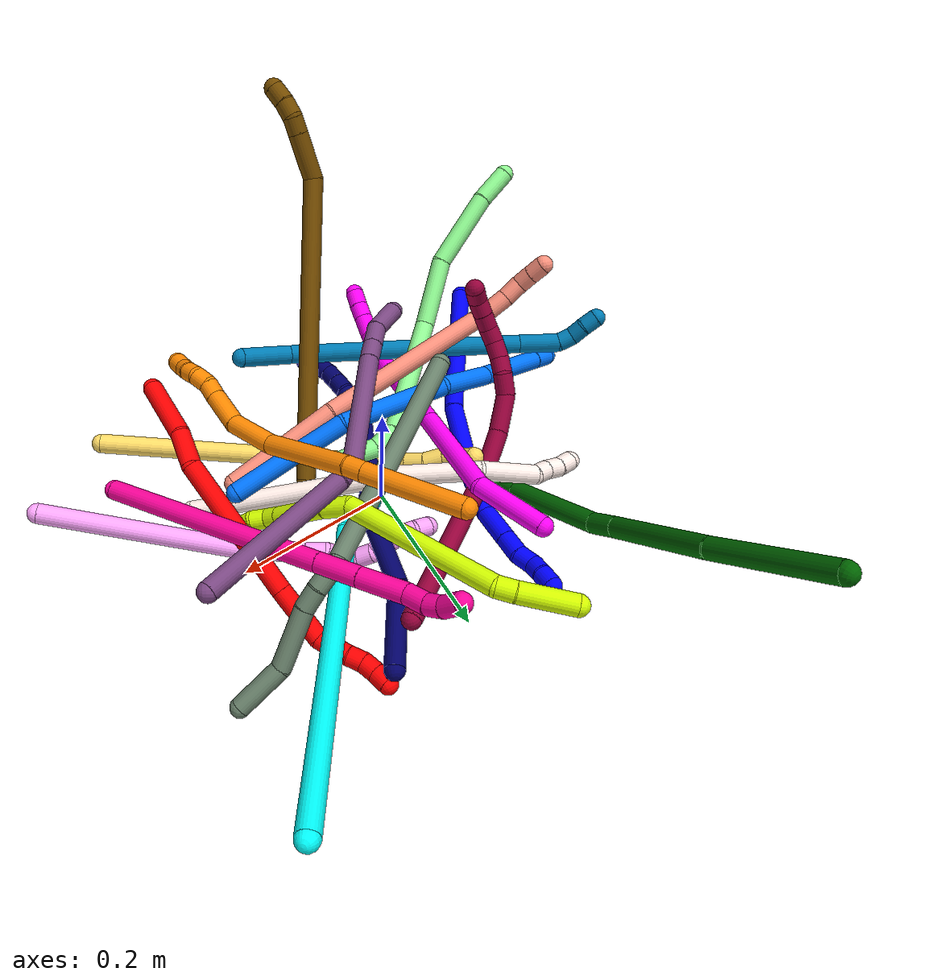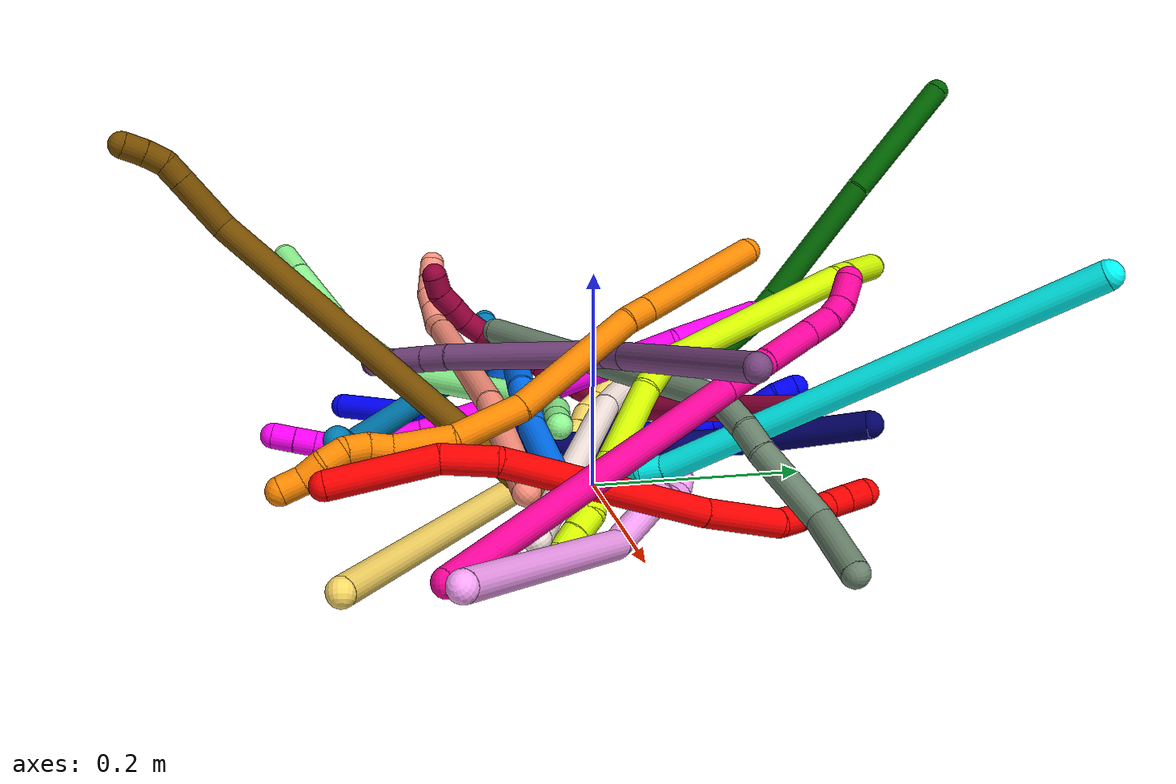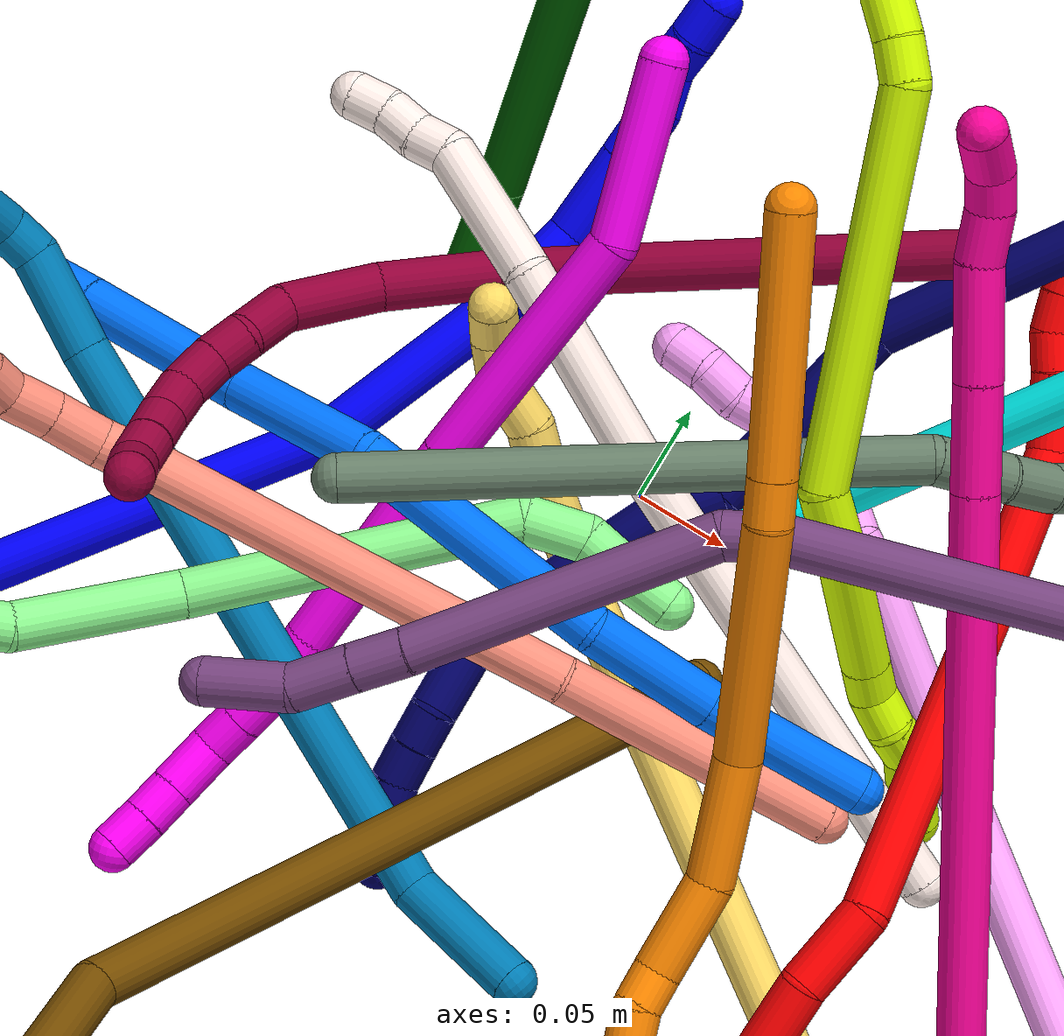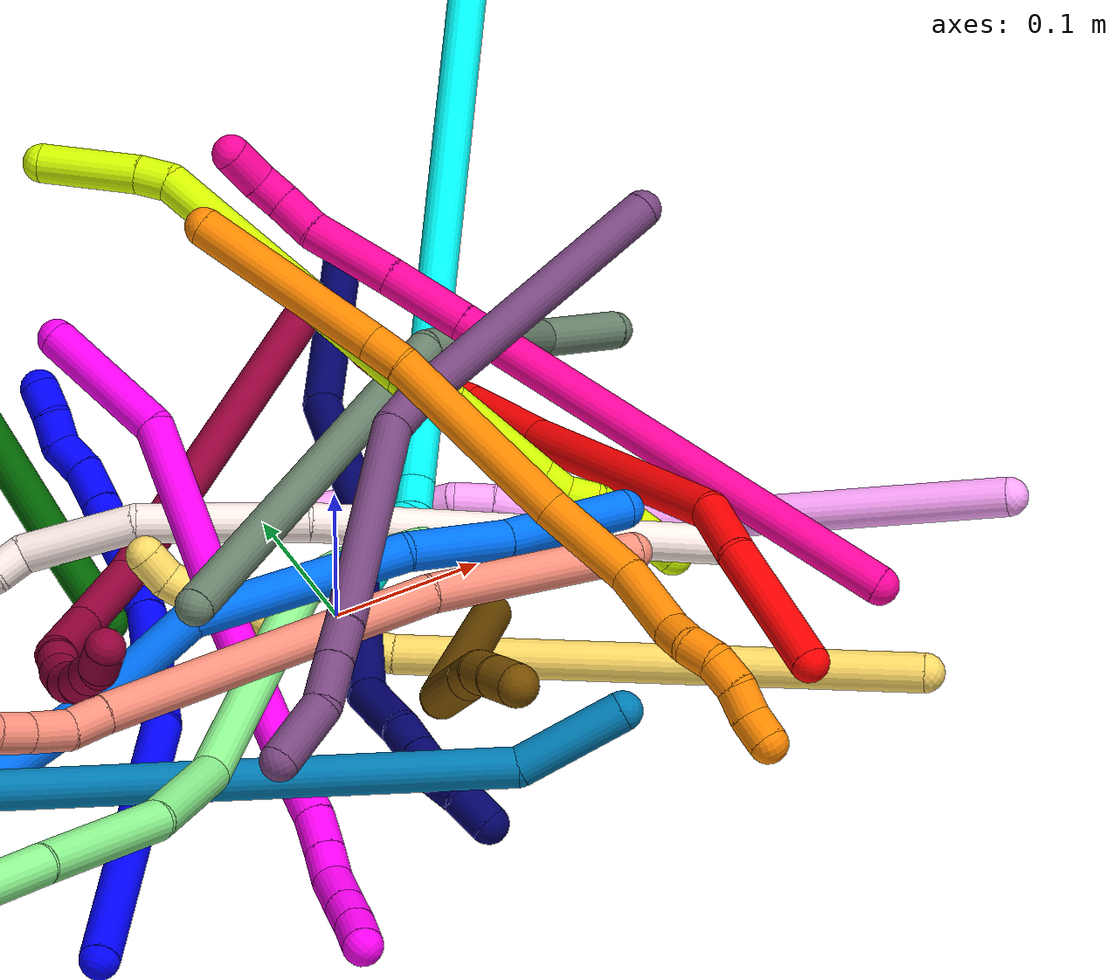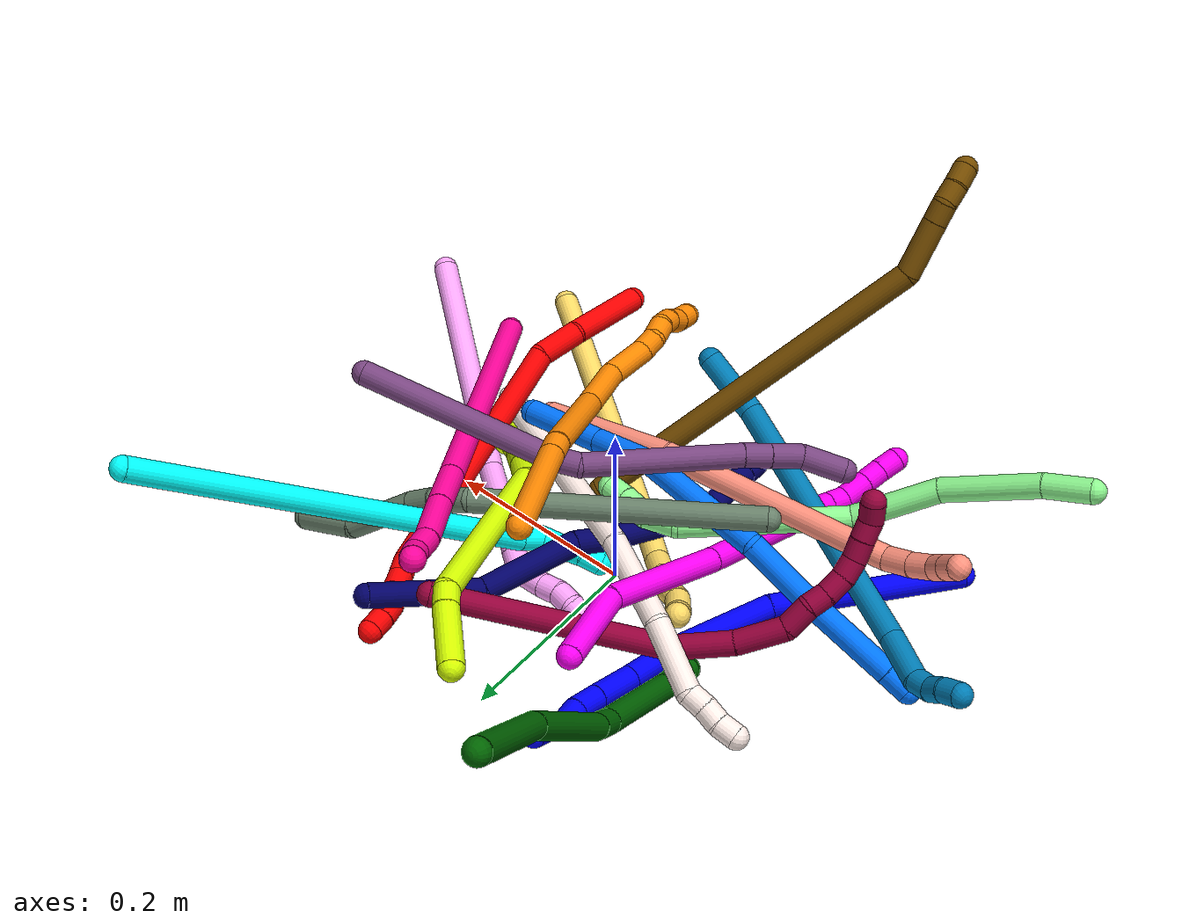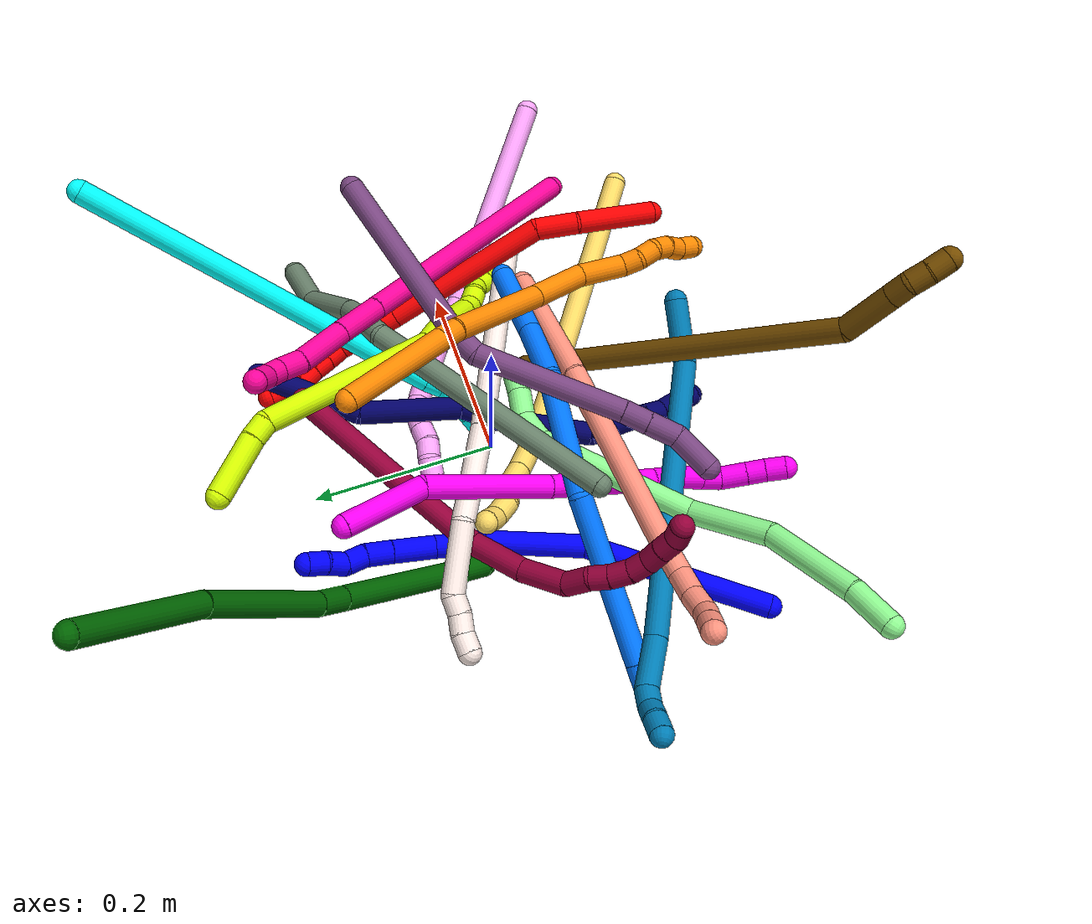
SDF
<sdf version="1.7">
 <world name="default">
  <plugin name="TubeGeneratorPlugin" filename="libtube_generator_plugin.so"/>
  <model name="photoneo_s_sensor">
   <static>1</static>
   <pose>0 0 2 1.57079 1.57079 3.14159</pose>
   <link name="link">
    <inertial><mass>0.1</mass></inertial>
    <sensor name="sensor" type="depth">
     <update_rate>30</update_rate>
     <camera>
      <horizontal_fov>1.22</horizontal_fov>
      <image><width>1920</width><height>1200</height><format>B8G8R8</format></image>
      <clip><near>0.1</near><far>4</far></clip>
      <depth_camera><output>points</output></depth_camera>
     </camera>
     <plugin name="camera_plugin" filename="libgazebo_ros_depth_camera.so">
      <baseline>0.2</baseline>
      <alwaysOn>1</alwaysOn>
      <updateRate>0.0</updateRate>
      <cameraName>camera_ir</cameraName>
      <imageTopicName>/camera/color/image_raw</imageTopicName>
      <cameraInfoTopicName>/camera/color/camera_info</cameraInfoTopicName>
      <depthImageTopicName>/camera/depth/image_raw</depthImageTopicName>
      <depthImageCameraInfoTopicName>/camera/depth/camera_info</depthImageCameraInfoTopicName>
      <pointCloudTopicName>/camera/depth/points</pointCloudTopicName>
      <frameName>fr_optical</frameName>
      <pointCloudCutoff>0.1</pointCloudCutoff>
      <pointCloudCutoffMax>2.0</pointCloudCutoffMax>
      <distortionK1>0</distortionK1>
      <distortionK2>0</distortionK2>
      <distortionK3>0</distortionK3>
      <distortionT1>0</distortionT1>
      <distortionT2>0</distortionT2>
      <CxPrime>0</CxPrime>
      <Cx>0</Cx>
      <Cy>0</Cy>
      <focalLength>0</focalLength>
      <hackBaseline>0</hackBaseline>
     </plugin>
    </sensor>
   </link>
  </model>
  <gravity>0 0 -9.8</gravity>
  <magnetic_field>6e-06 2.3e-05 -4.2e-05</magnetic_field>
  <atmosphere type="adiabatic"/>
  <physics name="default_physics" default="0" type="ode">
   <max_step_size>0.003</max_step_size>
   <real_time_factor>1</real_time_factor>
   <real_time_update_rate>1000</real_time_update_rate>
   <max_contacts>10000</max_contacts>
   <ode>
    <solver>
     <type>quick</type>
     <iters>100</iters>
     <sor>1.3</sor>
     <use_dynamic_moi_rescaling>0</use_dynamic_moi_rescaling>
    </solver>
    <constraints>
     <contact_max_correcting_vel>0</contact_max_correcting_vel>
     <contact_surface_layer>0.001</contact_surface_layer>
     <cfm>0</cfm>
     <erp>0.2</erp>
    </constraints>
   </ode>
  </physics>
  <scene><ambient>0.4 0.4 0.4 1</ambient><background>0.7 0.7 0.7 1</background><shadows>0</shadows></scene>
  <audio><device>default</device></audio>
  <spherical_coordinates>
   <surface_model>EARTH_WGS84</surface_model>
   <latitude_deg>0</latitude_deg>
   <longitude_deg>0</longitude_deg>
   <elevation>0</elevation>
   <heading_deg>0</heading_deg>
  </spherical_coordinates>
  <model name="bin">
   <static>1</static>
   <link name="bottom">
    <collision name="collision-bottom">
     <pose>0 0 -0.01 0 -0 0</pose>
     <geometry><box><size>0.8 0.6 0.02</size></box></geometry>
     <surface>
      <friction><ode><mu>100</mu><mu2>100</mu2></ode></friction>
      <contact><collide_bitmask>65535</collide_bitmask></contact>
     </surface>
    </collision>
   </link>
   <link name="west_wall">
    <collision name="collision-west_wall">
     <pose>-0.41 0 0.1 0 -0 0</pose>
     <geometry><box><size>0.02 0.6 0.2</size></box></geometry>
     <surface>
      <friction><ode><mu>100</mu><mu2>100</mu2></ode></friction>
      <contact><collide_bitmask>65535</collide_bitmask></contact>
     </surface>
    </collision>
   </link>
   <link name="east_wall">
    <collision name="collision-east_wall">
     <pose>0.41 0 0.1 0 -0 0</pose>
     <geometry><box><size>0.02 0.6 0.2</size></box></geometry>
     <surface>
      <friction><ode><mu>100</mu><mu2>100</mu2></ode></friction>
      <contact><collide_bitmask>65535</collide_bitmask></contact>
     </surface>
    </collision>
   </link>
   <link name="south_wall">
    <collision name="collision-south_wall">
     <pose>0 -0.31 0.1 0 -0 0</pose>
     <geometry><box><size>0.8 0.02 0.2</size></box></geometry>
     <surface>
      <friction><ode><mu>100</mu><mu2>100</mu2></ode></friction>
      <contact><collide_bitmask>65535</collide_bitmask></contact>
     </surface>
    </collision>
   </link>
   <link name="north_wall">
    <collision name="collision-north_wall">
     <pose>0 0.31 0.1 0 -0 0</pose>
     <geometry><box><size>0.8 0.02 0.2</size></box></geometry>
     <surface>
      <friction><ode><mu>100</mu><mu2>100</mu2></ode></friction>
      <contact><collide_bitmask>65535</collide_bitmask></contact>
     </surface>
    </collision>
   </link>
  </model>
  <model name="1">
   <static>0</static>
   <link name="1">
    <collision name="collision-cylinder-e_1_1_4">
     <pose>0.00056 0.028806 -0.094946 -2.84702 0.005648 -0.038066</pose>
     <geometry><cylinder><radius>0.0125</radius><length>0.198443</length></cylinder></geometry>
     <surface>
      <friction><ode><mu>1.16</mu><mu2>1.16</mu2><slip1>0</slip1><slip2>0</slip2></ode></friction>
      <contact><ode><kp>1e+06</kp><kd>1</kd><max_vel>0</max_vel><min_depth>0.001</min_depth></ode></contact>
     </surface>
    </collision>
    <visual name="visual-cylinder-e_1_1_4">
     <pose>0.00056 0.028806 -0.094946 -2.84702 0.005648 -0.038066</pose>
     <geometry><cylinder><radius>0.0125</radius><length>0.198443</length></cylinder></geometry>
     <material><ambient>0 0 1 1</ambient></material>
    </visual>
    <collision name="collision-cylinder-e_2_4_5">
     <pose>0.011502 0.082179 -0.235246 -2.64517 0.198614 -0.749146</pose>
     <geometry><cylinder><radius>0.0125</radius><length>0.105228</length></cylinder></geometry>
     <surface>
      <friction><ode><mu>1.16</mu><mu2>1.16</mu2><slip1>0</slip1><slip2>0</slip2></ode></friction>
      <contact><ode><kp>1e+06</kp><kd>1</kd><max_vel>0</max_vel><min_depth>0.001</min_depth></ode></contact>
     </surface>
    </collision>
    <visual name="visual-cylinder-e_2_4_5">
     <pose>0.011502 0.082179 -0.235246 -2.64517 0.198614 -0.749146</pose>
     <geometry><cylinder><radius>0.0125</radius><length>0.105228</length></cylinder></geometry>
     <material><ambient>0 0 1 1</ambient></material>
    </visual>
    <collision name="collision-cylinder-e_3_5_6">
     <pose>0.029335 0.121541 -0.301655 -2.52904 0.281836 -0.843379</pose>
     <geometry><cylinder><radius>0.0125</radius><length>0.053584</length></cylinder></geometry>
     <surface>
      <friction><ode><mu>1.16</mu><mu2>1.16</mu2><slip1>0</slip1><slip2>0</slip2></ode></friction>
      <contact><ode><kp>1e+06</kp><kd>1</kd><max_vel>0</max_vel><min_depth>0.001</min_depth></ode></contact>
     </surface>
    </collision>
    <visual name="visual-cylinder-e_3_5_6">
     <pose>0.029335 0.121541 -0.301655 -2.52904 0.281836 -0.843379</pose>
     <geometry><cylinder><radius>0.0125</radius><length>0.053584</length></cylinder></geometry>
     <material><ambient>0 0 1 1</ambient></material>
    </visual>
    <collision name="collision-cylinder-e_4_6_7">
     <pose>0.050432 0.144549 -0.340708 -2.71357 0.603857 -1.92305</pose>
     <geometry><cylinder><radius>0.0125</radius><length>0.048063</length></cylinder></geometry>
     <surface>
      <friction><ode><mu>1.16</mu><mu2>1.16</mu2><slip1>0</slip1><slip2>0</slip2></ode></friction>
      <contact><ode><kp>1e+06</kp><kd>1</kd><max_vel>0</max_vel><min_depth>0.001</min_depth></ode></contact>
     </surface>
    </collision>
    <visual name="visual-cylinder-e_4_6_7">
     <pose>0.050432 0.144549 -0.340708 -2.71357 0.603857 -1.92305</pose>
     <geometry><cylinder><radius>0.0125</radius><length>0.048063</length></cylinder></geometry>
     <material><ambient>0 0 1 1</ambient></material>
    </visual>
    <collision name="collision-cylinder-e_5_7_8">
     <pose>0.07217 0.157999 -0.369358 -2.68449 0.598323 -1.84919</pose>
     <geometry><cylinder><radius>0.0125</radius><length>0.028735</length></cylinder></geometry>
     <surface>
      <friction><ode><mu>1.16</mu><mu2>1.16</mu2><slip1>0</slip1><slip2>0</slip2></ode></friction>
      <contact><ode><kp>1e+06</kp><kd>1</kd><max_vel>0</max_vel><min_depth>0.001</min_depth></ode></contact>
     </surface>
    </collision>
    <visual name="visual-cylinder-e_5_7_8">
     <pose>0.07217 0.157999 -0.369358 -2.68449 0.598323 -1.84919</pose>
     <geometry><cylinder><radius>0.0125</radius><length>0.028735</length></cylinder></geometry>
     <material><ambient>0 0 1 1</ambient></material>
    </visual>
    <collision name="collision-cylinder-e_6_8_9">
     <pose>0.088999 0.168234 -0.385991 -2.44563 0.842446 -1.78044</pose>
     <geometry><cylinder><radius>0.0125</radius><length>0.023412</length></cylinder></geometry>
     <surface>
      <friction><ode><mu>1.16</mu><mu2>1.16</mu2><slip1>0</slip1><slip2>0</slip2></ode></friction>
      <contact><ode><kp>1e+06</kp><kd>1</kd><max_vel>0</max_vel><min_depth>0.001</min_depth></ode></contact>
     </surface>
    </collision>
    <visual name="visual-cylinder-e_6_8_9">
     <pose>0.088999 0.168234 -0.385991 -2.44563 0.842446 -1.78044</pose>
     <geometry><cylinder><radius>0.0125</radius><length>0.023412</length></cylinder></geometry>
     <material><ambient>0 0 1 1</ambient></material>
    </visual>
    <collision name="collision-cylinder-e_7_9_10">
     <pose>0.104523 0.173678 -0.400094 -3.0865 0.695367 -2.98982</pose>
     <geometry><cylinder><radius>0.0125</radius><length>0.021191</length></cylinder></geometry>
     <surface>
      <friction><ode><mu>1.16</mu><mu2>1.16</mu2><slip1>0</slip1><slip2>0</slip2></ode></friction>
      <contact><ode><kp>1e+06</kp><kd>1</kd><max_vel>0</max_vel><min_depth>0.001</min_depth></ode></contact>
     </surface>
    </collision>
    <visual name="visual-cylinder-e_7_9_10">
     <pose>0.104523 0.173678 -0.400094 -3.0865 0.695367 -2.98982</pose>
     <geometry><cylinder><radius>0.0125</radius><length>0.021191</length></cylinder></geometry>
     <material><ambient>0 0 1 1</ambient></material>
    </visual>
    <collision name="collision-cylinder-e_8_10_2">
     <pose>0.117807 0.176824 -0.416243 -2.81738 0.654364 -2.2435</pose>
     <geometry><cylinder><radius>0.0125</radius><length>0.021344</length></cylinder></geometry>
     <surface>
      <friction><ode><mu>1.16</mu><mu2>1.16</mu2><slip1>0</slip1><slip2>0</slip2></ode></friction>
      <contact><ode><kp>1e+06</kp><kd>1</kd><max_vel>0</max_vel><min_depth>0.001</min_depth></ode></contact>
     </surface>
    </collision>
    <visual name="visual-cylinder-e_8_10_2">
     <pose>0.117807 0.176824 -0.416243 -2.81738 0.654364 -2.2435</pose>
     <geometry><cylinder><radius>0.0125</radius><length>0.021344</length></cylinder></geometry>
     <material><ambient>0 0 1 1</ambient></material>
    </visual>
    <collision name="collision-sphere-2">
     <pose>0.124302 0.179521 -0.42427 0 -0 0</pose>
     <geometry><sphere><radius>0.0125</radius></sphere></geometry>
     <surface>
      <friction><ode><mu>1.16</mu><mu2>1.16</mu2><slip1>0</slip1><slip2>0</slip2></ode></friction>
      <contact><ode><kp>1e+06</kp><kd>1</kd><max_vel>0</max_vel><min_depth>0.001</min_depth></ode></contact>
     </surface>
    </collision>
    <visual name="visual-sphere-2">
     <pose>0.124302 0.179521 -0.42427 0 -0 0</pose>
     <geometry><sphere><radius>0.0125</radius></sphere></geometry>
     <material><ambient>0 0 1 1</ambient></material>
    </visual>
    <collision name="collision-sphere-10">
     <pose>0.111311 0.174126 -0.408217 0 -0 0</pose>
     <geometry><sphere><radius>0.0125</radius></sphere></geometry>
     <surface>
      <friction><ode><mu>1.16</mu><mu2>1.16</mu2><slip1>0</slip1><slip2>0</slip2></ode></friction>
      <contact><ode><kp>1e+06</kp><kd>1</kd><max_vel>0</max_vel><min_depth>0.001</min_depth></ode></contact>
     </surface>
    </collision>
    <visual name="visual-sphere-10">
     <pose>0.111311 0.174126 -0.408217 0 -0 0</pose>
     <geometry><sphere><radius>0.0125</radius></sphere></geometry>
     <material><ambient>0 0 1 1</ambient></material>
    </visual>
    <collision name="collision-sphere-9">
     <pose>0.097735 0.17323 -0.391971 0 -0 0</pose>
     <geometry><sphere><radius>0.0125</radius></sphere></geometry>
     <surface>
      <friction><ode><mu>1.16</mu><mu2>1.16</mu2><slip1>0</slip1><slip2>0</slip2></ode></friction>
      <contact><ode><kp>1e+06</kp><kd>1</kd><max_vel>0</max_vel><min_depth>0.001</min_depth></ode></contact>
     </surface>
    </collision>
    <visual name="visual-sphere-9">
     <pose>0.097735 0.17323 -0.391971 0 -0 0</pose>
     <geometry><sphere><radius>0.0125</radius></sphere></geometry>
     <material><ambient>0 0 1 1</ambient></material>
    </visual>
    <collision name="collision-sphere-4">
     <pose>0.001121 0.057612 -0.189892 0 -0 0</pose>
     <geometry><sphere><radius>0.0125</radius></sphere></geometry>
     <surface>
      <friction><ode><mu>1.16</mu><mu2>1.16</mu2><slip1>0</slip1><slip2>0</slip2></ode></friction>
      <contact><ode><kp>1e+06</kp><kd>1</kd><max_vel>0</max_vel><min_depth>0.001</min_depth></ode></contact>
     </surface>
    </collision>
    <visual name="visual-sphere-4">
     <pose>0.001121 0.057612 -0.189892 0 -0 0</pose>
     <geometry><sphere><radius>0.0125</radius></sphere></geometry>
     <material><ambient>0 0 1 1</ambient></material>
    </visual>
    <collision name="collision-sphere-1">
     <geometry><sphere><radius>0.0125</radius></sphere></geometry>
     <surface>
      <friction><ode><mu>1.16</mu><mu2>1.16</mu2><slip1>0</slip1><slip2>0</slip2></ode></friction>
      <contact><ode><kp>1e+06</kp><kd>1</kd><max_vel>0</max_vel><min_depth>0.001</min_depth></ode></contact>
     </surface>
    </collision>
    <visual name="visual-sphere-1">
     <geometry><sphere><radius>0.0125</radius></sphere></geometry>
     <material><ambient>0 0 1 1</ambient></material>
    </visual>
    <collision name="collision-sphere-8">
     <pose>0.080263 0.163239 -0.380011 0 -0 0</pose>
     <geometry><sphere><radius>0.0125</radius></sphere></geometry>
     <surface>
      <friction><ode><mu>1.16</mu><mu2>1.16</mu2><slip1>0</slip1><slip2>0</slip2></ode></friction>
      <contact><ode><kp>1e+06</kp><kd>1</kd><max_vel>0</max_vel><min_depth>0.001</min_depth></ode></contact>
     </surface>
    </collision>
    <visual name="visual-sphere-8">
     <pose>0.080263 0.163239 -0.380011 0 -0 0</pose>
     <geometry><sphere><radius>0.0125</radius></sphere></geometry>
     <material><ambient>0 0 1 1</ambient></material>
    </visual>
    <collision name="collision-sphere-5">
     <pose>0.021883 0.106745 -0.280599 0 -0 0</pose>
     <geometry><sphere><radius>0.0125</radius></sphere></geometry>
     <surface>
      <friction><ode><mu>1.16</mu><mu2>1.16</mu2><slip1>0</slip1><slip2>0</slip2></ode></friction>
      <contact><ode><kp>1e+06</kp><kd>1</kd><max_vel>0</max_vel><min_depth>0.001</min_depth></ode></contact>
     </surface>
    </collision>
    <visual name="visual-sphere-5">
     <pose>0.021883 0.106745 -0.280599 0 -0 0</pose>
     <geometry><sphere><radius>0.0125</radius></sphere></geometry>
     <material><ambient>0 0 1 1</ambient></material>
    </visual>
    <collision name="collision-sphere-6">
     <pose>0.036786 0.136338 -0.322711 0 -0 0</pose>
     <geometry><sphere><radius>0.0125</radius></sphere></geometry>
     <surface>
      <friction><ode><mu>1.16</mu><mu2>1.16</mu2><slip1>0</slip1><slip2>0</slip2></ode></friction>
      <contact><ode><kp>1e+06</kp><kd>1</kd><max_vel>0</max_vel><min_depth>0.001</min_depth></ode></contact>
     </surface>
    </collision>
    <visual name="visual-sphere-6">
     <pose>0.036786 0.136338 -0.322711 0 -0 0</pose>
     <geometry><sphere><radius>0.0125</radius></sphere></geometry>
     <material><ambient>0 0 1 1</ambient></material>
    </visual>
    <collision name="collision-sphere-7">
     <pose>0.064077 0.152759 -0.358705 0 -0 0</pose>
     <geometry><sphere><radius>0.0125</radius></sphere></geometry>
     <surface>
      <friction><ode><mu>1.16</mu><mu2>1.16</mu2><slip1>0</slip1><slip2>0</slip2></ode></friction>
      <contact><ode><kp>1e+06</kp><kd>1</kd><max_vel>0</max_vel><min_depth>0.001</min_depth></ode></contact>
     </surface>
    </collision>
    <visual name="visual-sphere-7">
     <pose>0.064077 0.152759 -0.358705 0 -0 0</pose>
     <geometry><sphere><radius>0.0125</radius></sphere></geometry>
     <material><ambient>0 0 1 1</ambient></material>
    </visual>
    <inertial>
     <pose>0.028408 0.087515 -0.226297 0 -0 0</pose>
     <mass>0.5</mass>
     <inertia>
      <ixx>0.000627</ixx>
      <ixy>0</ixy>
      <ixz>0</ixz>
      <iyy>-0.000786</iyy>
      <iyz>0</iyz>
      <izz>-0.000326</izz>
     </inertia>
    </inertial>
   </link>
   <pose>-0.270779 -0.212165 0.012476 -1.89278 -0.628383 2.49965</pose>
  </model>
  <model name="2">
   <static>0</static>
   <link name="2">
    <collision name="collision-cylinder-e_1_1_4">
     <pose>-0.004747 0.020313 -0.040989 -2.6815 -0.103409 0.434957</pose>
     <geometry><cylinder><radius>0.0125</radius><length>0.091983</length></cylinder></geometry>
     <surface>
      <friction><ode><mu>1.16</mu><mu2>1.16</mu2><slip1>0</slip1><slip2>0</slip2></ode></friction>
      <contact><ode><kp>1e+06</kp><kd>1</kd><max_vel>0</max_vel><min_depth>0.001</min_depth></ode></contact>
     </surface>
    </collision>
    <visual name="visual-cylinder-e_1_1_4">
     <pose>-0.004747 0.020313 -0.040989 -2.6815 -0.103409 0.434957</pose>
     <geometry><cylinder><radius>0.0125</radius><length>0.091983</length></cylinder></geometry>
     <material><ambient>1 0 0 1</ambient></material>
    </visual>
    <collision name="collision-cylinder-e_2_4_5">
     <pose>-0.007983 0.045869 -0.104535 -2.9132 0.065198 -0.554019</pose>
     <geometry><cylinder><radius>0.0125</radius><length>0.046417</length></cylinder></geometry>
     <surface>
      <friction><ode><mu>1.16</mu><mu2>1.16</mu2><slip1>0</slip1><slip2>0</slip2></ode></friction>
      <contact><ode><kp>1e+06</kp><kd>1</kd><max_vel>0</max_vel><min_depth>0.001</min_depth></ode></contact>
     </surface>
    </collision>
    <visual name="visual-cylinder-e_2_4_5">
     <pose>-0.007983 0.045869 -0.104535 -2.9132 0.065198 -0.554019</pose>
     <geometry><cylinder><radius>0.0125</radius><length>0.046417</length></cylinder></geometry>
     <material><ambient>1 0 0 1</ambient></material>
    </visual>
    <collision name="collision-cylinder-e_3_5_6">
     <pose>-0.024752 0.043484 -0.21868 3.0585 -0.196348 -2.34277</pose>
     <geometry><cylinder><radius>0.0125</radius><length>0.18741</length></cylinder></geometry>
     <surface>
      <friction><ode><mu>1.16</mu><mu2>1.16</mu2><slip1>0</slip1><slip2>0</slip2></ode></friction>
      <contact><ode><kp>1e+06</kp><kd>1</kd><max_vel>0</max_vel><min_depth>0.001</min_depth></ode></contact>
     </surface>
    </collision>
    <visual name="visual-cylinder-e_3_5_6">
     <pose>-0.024752 0.043484 -0.21868 3.0585 -0.196348 -2.34277</pose>
     <geometry><cylinder><radius>0.0125</radius><length>0.18741</length></cylinder></geometry>
     <material><ambient>1 0 0 1</ambient></material>
    </visual>
    <collision name="collision-cylinder-e_4_6_7">
     <pose>-0.051325 0.035927 -0.345409 -3.13957 -0.231741 3.12424</pose>
     <geometry><cylinder><radius>0.0125</radius><length>0.072213</length></cylinder></geometry>
     <surface>
      <friction><ode><mu>1.16</mu><mu2>1.16</mu2><slip1>0</slip1><slip2>0</slip2></ode></friction>
      <contact><ode><kp>1e+06</kp><kd>1</kd><max_vel>0</max_vel><min_depth>0.001</min_depth></ode></contact>
     </surface>
    </collision>
    <visual name="visual-cylinder-e_4_6_7">
     <pose>-0.051325 0.035927 -0.345409 -3.13957 -0.231741 3.12424</pose>
     <geometry><cylinder><radius>0.0125</radius><length>0.072213</length></cylinder></geometry>
     <material><ambient>1 0 0 1</ambient></material>
    </visual>
    <collision name="collision-cylinder-e_5_7_8">
     <pose>-0.065531 0.037891 -0.389327 -2.9292 -0.582414 2.45819</pose>
     <geometry><cylinder><radius>0.0125</radius><length>0.021502</length></cylinder></geometry>
     <surface>
      <friction><ode><mu>1.16</mu><mu2>1.16</mu2><slip1>0</slip1><slip2>0</slip2></ode></friction>
      <contact><ode><kp>1e+06</kp><kd>1</kd><max_vel>0</max_vel><min_depth>0.001</min_depth></ode></contact>
     </surface>
    </collision>
    <visual name="visual-cylinder-e_5_7_8">
     <pose>-0.065531 0.037891 -0.389327 -2.9292 -0.582414 2.45819</pose>
     <geometry><cylinder><radius>0.0125</radius><length>0.021502</length></cylinder></geometry>
     <material><ambient>1 0 0 1</ambient></material>
    </visual>
    <collision name="collision-cylinder-e_6_8_9">
     <pose>-0.077221 0.042709 -0.405873 -2.78141 -0.607935 2.08984</pose>
     <geometry><cylinder><radius>0.0125</radius><length>0.020226</length></cylinder></geometry>
     <surface>
      <friction><ode><mu>1.16</mu><mu2>1.16</mu2><slip1>0</slip1><slip2>0</slip2></ode></friction>
      <contact><ode><kp>1e+06</kp><kd>1</kd><max_vel>0</max_vel><min_depth>0.001</min_depth></ode></contact>
     </surface>
    </collision>
    <visual name="visual-cylinder-e_6_8_9">
     <pose>-0.077221 0.042709 -0.405873 -2.78141 -0.607935 2.08984</pose>
     <geometry><cylinder><radius>0.0125</radius><length>0.020226</length></cylinder></geometry>
     <material><ambient>1 0 0 1</ambient></material>
    </visual>
    <collision name="collision-cylinder-e_7_9_10">
     <pose>-0.089433 0.047287 -0.421233 -2.92724 -0.691819 2.56139</pose>
     <geometry><cylinder><radius>0.0125</radius><length>0.020178</length></cylinder></geometry>
     <surface>
      <friction><ode><mu>1.16</mu><mu2>1.16</mu2><slip1>0</slip1><slip2>0</slip2></ode></friction>
      <contact><ode><kp>1e+06</kp><kd>1</kd><max_vel>0</max_vel><min_depth>0.001</min_depth></ode></contact>
     </surface>
    </collision>
    <visual name="visual-cylinder-e_7_9_10">
     <pose>-0.089433 0.047287 -0.421233 -2.92724 -0.691819 2.56139</pose>
     <geometry><cylinder><radius>0.0125</radius><length>0.020178</length></cylinder></geometry>
     <material><ambient>1 0 0 1</ambient></material>
    </visual>
    <collision name="collision-cylinder-e_8_10_11">
     <pose>-0.09983 0.052538 -0.43728 -2.73927 -0.406908 1.58244</pose>
     <geometry><cylinder><radius>0.0125</radius><length>0.020014</length></cylinder></geometry>
     <surface>
      <friction><ode><mu>1.16</mu><mu2>1.16</mu2><slip1>0</slip1><slip2>0</slip2></ode></friction>
      <contact><ode><kp>1e+06</kp><kd>1</kd><max_vel>0</max_vel><min_depth>0.001</min_depth></ode></contact>
     </surface>
    </collision>
    <visual name="visual-cylinder-e_8_10_11">
     <pose>-0.09983 0.052538 -0.43728 -2.73927 -0.406908 1.58244</pose>
     <geometry><cylinder><radius>0.0125</radius><length>0.020014</length></cylinder></geometry>
     <material><ambient>1 0 0 1</ambient></material>
    </visual>
    <collision name="collision-cylinder-e_9_11_2">
     <pose>-0.106998 0.060011 -0.454412 -2.72162 -0.325531 1.31301</pose>
     <geometry><cylinder><radius>0.0125</radius><length>0.020057</length></cylinder></geometry>
     <surface>
      <friction><ode><mu>1.16</mu><mu2>1.16</mu2><slip1>0</slip1><slip2>0</slip2></ode></friction>
      <contact><ode><kp>1e+06</kp><kd>1</kd><max_vel>0</max_vel><min_depth>0.001</min_depth></ode></contact>
     </surface>
    </collision>
    <visual name="visual-cylinder-e_9_11_2">
     <pose>-0.106998 0.060011 -0.454412 -2.72162 -0.325531 1.31301</pose>
     <geometry><cylinder><radius>0.0125</radius><length>0.020057</length></cylinder></geometry>
     <material><ambient>1 0 0 1</ambient></material>
    </visual>
    <collision name="collision-sphere-2">
     <pose>-0.110205 0.063885 -0.463088 0 -0 0</pose>
     <geometry><sphere><radius>0.0125</radius></sphere></geometry>
     <surface>
      <friction><ode><mu>1.16</mu><mu2>1.16</mu2><slip1>0</slip1><slip2>0</slip2></ode></friction>
      <contact><ode><kp>1e+06</kp><kd>1</kd><max_vel>0</max_vel><min_depth>0.001</min_depth></ode></contact>
     </surface>
    </collision>
    <visual name="visual-sphere-2">
     <pose>-0.110205 0.063885 -0.463088 0 -0 0</pose>
     <geometry><sphere><radius>0.0125</radius></sphere></geometry>
     <material><ambient>1 0 0 1</ambient></material>
    </visual>
    <collision name="collision-sphere-11">
     <pose>-0.10379 0.056137 -0.445736 0 -0 0</pose>
     <geometry><sphere><radius>0.0125</radius></sphere></geometry>
     <surface>
      <friction><ode><mu>1.16</mu><mu2>1.16</mu2><slip1>0</slip1><slip2>0</slip2></ode></friction>
      <contact><ode><kp>1e+06</kp><kd>1</kd><max_vel>0</max_vel><min_depth>0.001</min_depth></ode></contact>
     </surface>
    </collision>
    <visual name="visual-sphere-11">
     <pose>-0.10379 0.056137 -0.445736 0 -0 0</pose>
     <geometry><sphere><radius>0.0125</radius></sphere></geometry>
     <material><ambient>1 0 0 1</ambient></material>
    </visual>
    <collision name="collision-sphere-10">
     <pose>-0.09587 0.04894 -0.428824 0 -0 0</pose>
     <geometry><sphere><radius>0.0125</radius></sphere></geometry>
     <surface>
      <friction><ode><mu>1.16</mu><mu2>1.16</mu2><slip1>0</slip1><slip2>0</slip2></ode></friction>
      <contact><ode><kp>1e+06</kp><kd>1</kd><max_vel>0</max_vel><min_depth>0.001</min_depth></ode></contact>
     </surface>
    </collision>
    <visual name="visual-sphere-10">
     <pose>-0.09587 0.04894 -0.428824 0 -0 0</pose>
     <geometry><sphere><radius>0.0125</radius></sphere></geometry>
     <material><ambient>1 0 0 1</ambient></material>
    </visual>
    <collision name="collision-sphere-9">
     <pose>-0.082997 0.045635 -0.413641 0 -0 0</pose>
     <geometry><sphere><radius>0.0125</radius></sphere></geometry>
     <surface>
      <friction><ode><mu>1.16</mu><mu2>1.16</mu2><slip1>0</slip1><slip2>0</slip2></ode></friction>
      <contact><ode><kp>1e+06</kp><kd>1</kd><max_vel>0</max_vel><min_depth>0.001</min_depth></ode></contact>
     </surface>
    </collision>
    <visual name="visual-sphere-9">
     <pose>-0.082997 0.045635 -0.413641 0 -0 0</pose>
     <geometry><sphere><radius>0.0125</radius></sphere></geometry>
     <material><ambient>1 0 0 1</ambient></material>
    </visual>
    <collision name="collision-sphere-4">
     <pose>-0.009495 0.040625 -0.081977 0 -0 0</pose>
     <geometry><sphere><radius>0.0125</radius></sphere></geometry>
     <surface>
      <friction><ode><mu>1.16</mu><mu2>1.16</mu2><slip1>0</slip1><slip2>0</slip2></ode></friction>
      <contact><ode><kp>1e+06</kp><kd>1</kd><max_vel>0</max_vel><min_depth>0.001</min_depth></ode></contact>
     </surface>
    </collision>
    <visual name="visual-sphere-4">
     <pose>-0.009495 0.040625 -0.081977 0 -0 0</pose>
     <geometry><sphere><radius>0.0125</radius></sphere></geometry>
     <material><ambient>1 0 0 1</ambient></material>
    </visual>
    <collision name="collision-sphere-1">
     <geometry><sphere><radius>0.0125</radius></sphere></geometry>
     <surface>
      <friction><ode><mu>1.16</mu><mu2>1.16</mu2><slip1>0</slip1><slip2>0</slip2></ode></friction>
      <contact><ode><kp>1e+06</kp><kd>1</kd><max_vel>0</max_vel><min_depth>0.001</min_depth></ode></contact>
     </surface>
    </collision>
    <visual name="visual-sphere-1">
     <geometry><sphere><radius>0.0125</radius></sphere></geometry>
     <material><ambient>1 0 0 1</ambient></material>
    </visual>
    <collision name="collision-sphere-8">
     <pose>-0.071445 0.039783 -0.398104 0 -0 0</pose>
     <geometry><sphere><radius>0.0125</radius></sphere></geometry>
     <surface>
      <friction><ode><mu>1.16</mu><mu2>1.16</mu2><slip1>0</slip1><slip2>0</slip2></ode></friction>
      <contact><ode><kp>1e+06</kp><kd>1</kd><max_vel>0</max_vel><min_depth>0.001</min_depth></ode></contact>
     </surface>
    </collision>
    <visual name="visual-sphere-8">
     <pose>-0.071445 0.039783 -0.398104 0 -0 0</pose>
     <geometry><sphere><radius>0.0125</radius></sphere></geometry>
     <material><ambient>1 0 0 1</ambient></material>
    </visual>
    <collision name="collision-sphere-5">
     <pose>-0.006471 0.051112 -0.127093 0 -0 0</pose>
     <geometry><sphere><radius>0.0125</radius></sphere></geometry>
     <surface>
      <friction><ode><mu>1.16</mu><mu2>1.16</mu2><slip1>0</slip1><slip2>0</slip2></ode></friction>
      <contact><ode><kp>1e+06</kp><kd>1</kd><max_vel>0</max_vel><min_depth>0.001</min_depth></ode></contact>
     </surface>
    </collision>
    <visual name="visual-sphere-5">
     <pose>-0.006471 0.051112 -0.127093 0 -0 0</pose>
     <geometry><sphere><radius>0.0125</radius></sphere></geometry>
     <material><ambient>1 0 0 1</ambient></material>
    </visual>
    <collision name="collision-sphere-6">
     <pose>-0.043032 0.035856 -0.310268 0 -0 0</pose>
     <geometry><sphere><radius>0.0125</radius></sphere></geometry>
     <surface>
      <friction><ode><mu>1.16</mu><mu2>1.16</mu2><slip1>0</slip1><slip2>0</slip2></ode></friction>
      <contact><ode><kp>1e+06</kp><kd>1</kd><max_vel>0</max_vel><min_depth>0.001</min_depth></ode></contact>
     </surface>
    </collision>
    <visual name="visual-sphere-6">
     <pose>-0.043032 0.035856 -0.310268 0 -0 0</pose>
     <geometry><sphere><radius>0.0125</radius></sphere></geometry>
     <material><ambient>1 0 0 1</ambient></material>
    </visual>
    <collision name="collision-sphere-7">
     <pose>-0.059618 0.035998 -0.380551 0 -0 0</pose>
     <geometry><sphere><radius>0.0125</radius></sphere></geometry>
     <surface>
      <friction><ode><mu>1.16</mu><mu2>1.16</mu2><slip1>0</slip1><slip2>0</slip2></ode></friction>
      <contact><ode><kp>1e+06</kp><kd>1</kd><max_vel>0</max_vel><min_depth>0.001</min_depth></ode></contact>
     </surface>
    </collision>
    <visual name="visual-sphere-7">
     <pose>-0.059618 0.035998 -0.380551 0 -0 0</pose>
     <geometry><sphere><radius>0.0125</radius></sphere></geometry>
     <material><ambient>1 0 0 1</ambient></material>
    </visual>
    <inertial>
     <pose>-0.036144 0.039258 -0.234989 0 -0 0</pose>
     <mass>0.5</mass>
     <inertia>
      <ixx>-0.000716</ixx>
      <ixy>0</ixy>
      <ixz>0</ixz>
      <iyy>1.2e-05</iyy>
      <iyz>0</iyz>
      <izz>0.000101</izz>
     </inertia>
    </inertial>
   </link>
   <pose>0.188685 -0.25553 0.080002 1.28761 0.074553 -0.11422</pose>
  </model>
  <model name="3">
   <static>0</static>
   <link name="3">
    <collision name="collision-cylinder-e_1_1_4">
     <pose>0.020495 -0.067424 -0.194718 2.80825 0.099133 0.573495</pose>
     <geometry><cylinder><radius>0.0125</radius><length>0.414155</length></cylinder></geometry>
     <surface>
      <friction><ode><mu>1.16</mu><mu2>1.16</mu2><slip1>0</slip1><slip2>0</slip2></ode></friction>
      <contact><ode><kp>1e+06</kp><kd>1</kd><max_vel>0</max_vel><min_depth>0.001</min_depth></ode></contact>
     </surface>
    </collision>
    <visual name="visual-cylinder-e_1_1_4">
     <pose>0.020495 -0.067424 -0.194718 2.80825 0.099133 0.573495</pose>
     <geometry><cylinder><radius>0.0125</radius><length>0.414155</length></cylinder></geometry>
     <material><ambient>0.003922 1 0.996078 1</ambient></material>
    </visual>
    <collision name="collision-cylinder-e_2_4_5">
     <pose>0.040962 -0.140378 -0.398579 2.59752 -0.002528 -0.009061</pose>
     <geometry><cylinder><radius>0.0125</radius><length>0.02137</length></cylinder></geometry>
     <surface>
      <friction><ode><mu>1.16</mu><mu2>1.16</mu2><slip1>0</slip1><slip2>0</slip2></ode></friction>
      <contact><ode><kp>1e+06</kp><kd>1</kd><max_vel>0</max_vel><min_depth>0.001</min_depth></ode></contact>
     </surface>
    </collision>
    <visual name="visual-cylinder-e_2_4_5">
     <pose>0.040962 -0.140378 -0.398579 2.59752 -0.002528 -0.009061</pose>
     <geometry><cylinder><radius>0.0125</radius><length>0.02137</length></cylinder></geometry>
     <material><ambient>0.003922 1 0.996078 1</ambient></material>
    </visual>
    <collision name="collision-cylinder-e_3_5_6">
     <pose>0.038513 -0.147643 -0.418744 2.98559 -0.213726 -1.88222</pose>
     <geometry><cylinder><radius>0.0125</radius><length>0.022836</length></cylinder></geometry>
     <surface>
      <friction><ode><mu>1.16</mu><mu2>1.16</mu2><slip1>0</slip1><slip2>0</slip2></ode></friction>
      <contact><ode><kp>1e+06</kp><kd>1</kd><max_vel>0</max_vel><min_depth>0.001</min_depth></ode></contact>
     </surface>
    </collision>
    <visual name="visual-cylinder-e_3_5_6">
     <pose>0.038513 -0.147643 -0.418744 2.98559 -0.213726 -1.88222</pose>
     <geometry><cylinder><radius>0.0125</radius><length>0.022836</length></cylinder></geometry>
     <material><ambient>0.003922 1 0.996078 1</ambient></material>
    </visual>
    <collision name="collision-cylinder-e_4_6_7">
     <pose>0.030909 -0.151938 -0.438185 2.84624 -0.532306 -2.14256</pose>
     <geometry><cylinder><radius>0.0125</radius><length>0.020424</length></cylinder></geometry>
     <surface>
      <friction><ode><mu>1.16</mu><mu2>1.16</mu2><slip1>0</slip1><slip2>0</slip2></ode></friction>
      <contact><ode><kp>1e+06</kp><kd>1</kd><max_vel>0</max_vel><min_depth>0.001</min_depth></ode></contact>
     </surface>
    </collision>
    <visual name="visual-cylinder-e_4_6_7">
     <pose>0.030909 -0.151938 -0.438185 2.84624 -0.532306 -2.14256</pose>
     <geometry><cylinder><radius>0.0125</radius><length>0.020424</length></cylinder></geometry>
     <material><ambient>0.003922 1 0.996078 1</ambient></material>
    </visual>
    <collision name="collision-cylinder-e_5_7_2">
     <pose>0.022455 -0.155759 -0.456614 3.01642 -0.313487 -2.38657</pose>
     <geometry><cylinder><radius>0.0125</radius><length>0.021214</length></cylinder></geometry>
     <surface>
      <friction><ode><mu>1.16</mu><mu2>1.16</mu2><slip1>0</slip1><slip2>0</slip2></ode></friction>
      <contact><ode><kp>1e+06</kp><kd>1</kd><max_vel>0</max_vel><min_depth>0.001</min_depth></ode></contact>
     </surface>
    </collision>
    <visual name="visual-cylinder-e_5_7_2">
     <pose>0.022455 -0.155759 -0.456614 3.01642 -0.313487 -2.38657</pose>
     <geometry><cylinder><radius>0.0125</radius><length>0.021214</length></cylinder></geometry>
     <material><ambient>0.003922 1 0.996078 1</ambient></material>
    </visual>
    <collision name="collision-sphere-2">
     <pose>0.019184 -0.157018 -0.466625 0 -0 0</pose>
     <geometry><sphere><radius>0.0125</radius></sphere></geometry>
     <surface>
      <friction><ode><mu>1.16</mu><mu2>1.16</mu2><slip1>0</slip1><slip2>0</slip2></ode></friction>
      <contact><ode><kp>1e+06</kp><kd>1</kd><max_vel>0</max_vel><min_depth>0.001</min_depth></ode></contact>
     </surface>
    </collision>
    <visual name="visual-sphere-2">
     <pose>0.019184 -0.157018 -0.466625 0 -0 0</pose>
     <geometry><sphere><radius>0.0125</radius></sphere></geometry>
     <material><ambient>0.003922 1 0.996078 1</ambient></material>
    </visual>
    <collision name="collision-sphere-7">
     <pose>0.025726 -0.154499 -0.446603 0 -0 0</pose>
     <geometry><sphere><radius>0.0125</radius></sphere></geometry>
     <surface>
      <friction><ode><mu>1.16</mu><mu2>1.16</mu2><slip1>0</slip1><slip2>0</slip2></ode></friction>
      <contact><ode><kp>1e+06</kp><kd>1</kd><max_vel>0</max_vel><min_depth>0.001</min_depth></ode></contact>
     </surface>
    </collision>
    <visual name="visual-sphere-7">
     <pose>0.025726 -0.154499 -0.446603 0 -0 0</pose>
     <geometry><sphere><radius>0.0125</radius></sphere></geometry>
     <material><ambient>0.003922 1 0.996078 1</ambient></material>
    </visual>
    <collision name="collision-sphere-6">
     <pose>0.036091 -0.149376 -0.429767 0 -0 0</pose>
     <geometry><sphere><radius>0.0125</radius></sphere></geometry>
     <surface>
      <friction><ode><mu>1.16</mu><mu2>1.16</mu2><slip1>0</slip1><slip2>0</slip2></ode></friction>
      <contact><ode><kp>1e+06</kp><kd>1</kd><max_vel>0</max_vel><min_depth>0.001</min_depth></ode></contact>
     </surface>
    </collision>
    <visual name="visual-sphere-6">
     <pose>0.036091 -0.149376 -0.429767 0 -0 0</pose>
     <geometry><sphere><radius>0.0125</radius></sphere></geometry>
     <material><ambient>0.003922 1 0.996078 1</ambient></material>
    </visual>
    <collision name="collision-sphere-5">
     <pose>0.040935 -0.145909 -0.407721 0 -0 0</pose>
     <geometry><sphere><radius>0.0125</radius></sphere></geometry>
     <surface>
      <friction><ode><mu>1.16</mu><mu2>1.16</mu2><slip1>0</slip1><slip2>0</slip2></ode></friction>
      <contact><ode><kp>1e+06</kp><kd>1</kd><max_vel>0</max_vel><min_depth>0.001</min_depth></ode></contact>
     </surface>
    </collision>
    <visual name="visual-sphere-5">
     <pose>0.040935 -0.145909 -0.407721 0 -0 0</pose>
     <geometry><sphere><radius>0.0125</radius></sphere></geometry>
     <material><ambient>0.003922 1 0.996078 1</ambient></material>
    </visual>
    <collision name="collision-sphere-1">
     <geometry><sphere><radius>0.0125</radius></sphere></geometry>
     <surface>
      <friction><ode><mu>1.16</mu><mu2>1.16</mu2><slip1>0</slip1><slip2>0</slip2></ode></friction>
      <contact><ode><kp>1e+06</kp><kd>1</kd><max_vel>0</max_vel><min_depth>0.001</min_depth></ode></contact>
     </surface>
    </collision>
    <visual name="visual-sphere-1">
     <geometry><sphere><radius>0.0125</radius></sphere></geometry>
     <material><ambient>0.003922 1 0.996078 1</ambient></material>
    </visual>
    <collision name="collision-sphere-4">
     <pose>0.040989 -0.134847 -0.389437 0 -0 0</pose>
     <geometry><sphere><radius>0.0125</radius></sphere></geometry>
     <surface>
      <friction><ode><mu>1.16</mu><mu2>1.16</mu2><slip1>0</slip1><slip2>0</slip2></ode></friction>
      <contact><ode><kp>1e+06</kp><kd>1</kd><max_vel>0</max_vel><min_depth>0.001</min_depth></ode></contact>
     </surface>
    </collision>
    <visual name="visual-sphere-4">
     <pose>0.040989 -0.134847 -0.389437 0 -0 0</pose>
     <geometry><sphere><radius>0.0125</radius></sphere></geometry>
     <material><ambient>0.003922 1 0.996078 1</ambient></material>
    </visual>
    <inertial>
     <pose>0.022701 -0.081406 -0.23472 0 -0 0</pose>
     <mass>0.5</mass>
     <inertia>
      <ixx>0.008164</ixx>
      <ixy>0</ixy>
      <ixz>0</ixz>
      <iyy>-0.001417</iyy>
      <iyz>0</iyz>
      <izz>0.001312</izz>
     </inertia>
    </inertial>
   </link>
   <pose>0.290737 0.341821 0.242871 -0.70103 0.517144 -0.426399</pose>
  </model>
  <model name="4">
   <static>0</static>
   <link name="4">
    <collision name="collision-cylinder-e_1_1_4">
     <pose>-0.018843 0.056694 -0.114546 -2.682 -0.146378 0.607461</pose>
     <geometry><cylinder><radius>0.0125</radius><length>0.258381</length></cylinder></geometry>
     <surface>
      <friction><ode><mu>1.16</mu><mu2>1.16</mu2><slip1>0</slip1><slip2>0</slip2></ode></friction>
      <contact><ode><kp>1e+06</kp><kd>1</kd><max_vel>0</max_vel><min_depth>0.001</min_depth></ode></contact>
     </surface>
    </collision>
    <visual name="visual-cylinder-e_1_1_4">
     <pose>-0.018843 0.056694 -0.114546 -2.682 -0.146378 0.607461</pose>
     <geometry><cylinder><radius>0.0125</radius><length>0.258381</length></cylinder></geometry>
     <material><ambient>1 0.65098 0.996078 1</ambient></material>
    </visual>
    <collision name="collision-cylinder-e_2_4_5">
     <pose>-0.045429 0.139816 -0.25375 -2.32154 -0.211033 0.478006</pose>
     <geometry><cylinder><radius>0.0125</radius><length>0.073928</length></cylinder></geometry>
     <surface>
      <friction><ode><mu>1.16</mu><mu2>1.16</mu2><slip1>0</slip1><slip2>0</slip2></ode></friction>
      <contact><ode><kp>1e+06</kp><kd>1</kd><max_vel>0</max_vel><min_depth>0.001</min_depth></ode></contact>
     </surface>
    </collision>
    <visual name="visual-cylinder-e_2_4_5">
     <pose>-0.045429 0.139816 -0.25375 -2.32154 -0.211033 0.478006</pose>
     <geometry><cylinder><radius>0.0125</radius><length>0.073928</length></cylinder></geometry>
     <material><ambient>1 0.65098 0.996078 1</ambient></material>
    </visual>
    <collision name="collision-cylinder-e_3_5_6">
     <pose>-0.056539 0.173895 -0.2878 -2.458 -0.271092 0.732153</pose>
     <geometry><cylinder><radius>0.0125</radius><length>0.02515</length></cylinder></geometry>
     <surface>
      <friction><ode><mu>1.16</mu><mu2>1.16</mu2><slip1>0</slip1><slip2>0</slip2></ode></friction>
      <contact><ode><kp>1e+06</kp><kd>1</kd><max_vel>0</max_vel><min_depth>0.001</min_depth></ode></contact>
     </surface>
    </collision>
    <visual name="visual-cylinder-e_3_5_6">
     <pose>-0.056539 0.173895 -0.2878 -2.458 -0.271092 0.732153</pose>
     <geometry><cylinder><radius>0.0125</radius><length>0.02515</length></cylinder></geometry>
     <material><ambient>1 0.65098 0.996078 1</ambient></material>
    </visual>
    <collision name="collision-cylinder-e_4_6_7">
     <pose>-0.060348 0.184009 -0.307002 -2.89575 -0.043636 0.349661</pose>
     <geometry><cylinder><radius>0.0125</radius><length>0.020245</length></cylinder></geometry>
     <surface>
      <friction><ode><mu>1.16</mu><mu2>1.16</mu2><slip1>0</slip1><slip2>0</slip2></ode></friction>
      <contact><ode><kp>1e+06</kp><kd>1</kd><max_vel>0</max_vel><min_depth>0.001</min_depth></ode></contact>
     </surface>
    </collision>
    <visual name="visual-cylinder-e_4_6_7">
     <pose>-0.060348 0.184009 -0.307002 -2.89575 -0.043636 0.349661</pose>
     <geometry><cylinder><radius>0.0125</radius><length>0.020245</length></cylinder></geometry>
     <material><ambient>1 0.65098 0.996078 1</ambient></material>
    </visual>
    <collision name="collision-cylinder-e_5_7_8">
     <pose>-0.063219 0.192045 -0.325095 -2.54926 -0.238592 0.748608</pose>
     <geometry><cylinder><radius>0.0125</radius><length>0.020553</length></cylinder></geometry>
     <surface>
      <friction><ode><mu>1.16</mu><mu2>1.16</mu2><slip1>0</slip1><slip2>0</slip2></ode></friction>
      <contact><ode><kp>1e+06</kp><kd>1</kd><max_vel>0</max_vel><min_depth>0.001</min_depth></ode></contact>
     </surface>
    </collision>
    <visual name="visual-cylinder-e_5_7_8">
     <pose>-0.063219 0.192045 -0.325095 -2.54926 -0.238592 0.748608</pose>
     <geometry><cylinder><radius>0.0125</radius><length>0.020553</length></cylinder></geometry>
     <material><ambient>1 0.65098 0.996078 1</ambient></material>
    </visual>
    <collision name="collision-cylinder-e_6_8_9">
     <pose>-0.070392 0.205805 -0.337644 -2.05101 -0.474854 0.759116</pose>
     <geometry><cylinder><radius>0.0125</radius><length>0.020756</length></cylinder></geometry>
     <surface>
      <friction><ode><mu>1.16</mu><mu2>1.16</mu2><slip1>0</slip1><slip2>0</slip2></ode></friction>
      <contact><ode><kp>1e+06</kp><kd>1</kd><max_vel>0</max_vel><min_depth>0.001</min_depth></ode></contact>
     </surface>
    </collision>
    <visual name="visual-cylinder-e_6_8_9">
     <pose>-0.070392 0.205805 -0.337644 -2.05101 -0.474854 0.759116</pose>
     <geometry><cylinder><radius>0.0125</radius><length>0.020756</length></cylinder></geometry>
     <material><ambient>1 0.65098 0.996078 1</ambient></material>
    </visual>
    <collision name="collision-cylinder-e_7_9_10">
     <pose>-0.082787 0.218107 -0.347579 -2.51381 -0.829243 1.87062</pose>
     <geometry><cylinder><radius>0.0125</radius><length>0.020748</length></cylinder></geometry>
     <surface>
      <friction><ode><mu>1.16</mu><mu2>1.16</mu2><slip1>0</slip1><slip2>0</slip2></ode></friction>
      <contact><ode><kp>1e+06</kp><kd>1</kd><max_vel>0</max_vel><min_depth>0.001</min_depth></ode></contact>
     </surface>
    </collision>
    <visual name="visual-cylinder-e_7_9_10">
     <pose>-0.082787 0.218107 -0.347579 -2.51381 -0.829243 1.87062</pose>
     <geometry><cylinder><radius>0.0125</radius><length>0.020748</length></cylinder></geometry>
     <material><ambient>1 0.65098 0.996078 1</ambient></material>
    </visual>
    <collision name="collision-cylinder-e_8_10_11">
     <pose>-0.098325 0.226588 -0.357781 -2.37479 -0.897417 1.74687</pose>
     <geometry><cylinder><radius>0.0125</radius><length>0.02018</length></cylinder></geometry>
     <surface>
      <friction><ode><mu>1.16</mu><mu2>1.16</mu2><slip1>0</slip1><slip2>0</slip2></ode></friction>
      <contact><ode><kp>1e+06</kp><kd>1</kd><max_vel>0</max_vel><min_depth>0.001</min_depth></ode></contact>
     </surface>
    </collision>
    <visual name="visual-cylinder-e_8_10_11">
     <pose>-0.098325 0.226588 -0.357781 -2.37479 -0.897417 1.74687</pose>
     <geometry><cylinder><radius>0.0125</radius><length>0.02018</length></cylinder></geometry>
     <material><ambient>1 0.65098 0.996078 1</ambient></material>
    </visual>
    <collision name="collision-cylinder-e_9_11_12">
     <pose>-0.112041 0.235652 -0.368964 -2.52674 -0.621204 1.58176</pose>
     <geometry><cylinder><radius>0.0125</radius><length>0.020028</length></cylinder></geometry>
     <surface>
      <friction><ode><mu>1.16</mu><mu2>1.16</mu2><slip1>0</slip1><slip2>0</slip2></ode></friction>
      <contact><ode><kp>1e+06</kp><kd>1</kd><max_vel>0</max_vel><min_depth>0.001</min_depth></ode></contact>
     </surface>
    </collision>
    <visual name="visual-cylinder-e_9_11_12">
     <pose>-0.112041 0.235652 -0.368964 -2.52674 -0.621204 1.58176</pose>
     <geometry><cylinder><radius>0.0125</radius><length>0.020028</length></cylinder></geometry>
     <material><ambient>1 0.65098 0.996078 1</ambient></material>
    </visual>
    <collision name="collision-cylinder-e_10_12_2">
     <pose>-0.123561 0.241613 -0.383759 -2.98758 -0.604444 2.65638</pose>
     <geometry><cylinder><radius>0.0125</radius><length>0.020031</length></cylinder></geometry>
     <surface>
      <friction><ode><mu>1.16</mu><mu2>1.16</mu2><slip1>0</slip1><slip2>0</slip2></ode></friction>
      <contact><ode><kp>1e+06</kp><kd>1</kd><max_vel>0</max_vel><min_depth>0.001</min_depth></ode></contact>
     </surface>
    </collision>
    <visual name="visual-cylinder-e_10_12_2">
     <pose>-0.123561 0.241613 -0.383759 -2.98758 -0.604444 2.65638</pose>
     <geometry><cylinder><radius>0.0125</radius><length>0.020031</length></cylinder></geometry>
     <material><ambient>1 0.65098 0.996078 1</ambient></material>
    </visual>
    <collision name="collision-sphere-2">
     <pose>-0.129253 0.242877 -0.391902 0 -0 0</pose>
     <geometry><sphere><radius>0.0125</radius></sphere></geometry>
     <surface>
      <friction><ode><mu>1.16</mu><mu2>1.16</mu2><slip1>0</slip1><slip2>0</slip2></ode></friction>
      <contact><ode><kp>1e+06</kp><kd>1</kd><max_vel>0</max_vel><min_depth>0.001</min_depth></ode></contact>
     </surface>
    </collision>
    <visual name="visual-sphere-2">
     <pose>-0.129253 0.242877 -0.391902 0 -0 0</pose>
     <geometry><sphere><radius>0.0125</radius></sphere></geometry>
     <material><ambient>1 0.65098 0.996078 1</ambient></material>
    </visual>
    <collision name="collision-sphere-12">
     <pose>-0.117869 0.240349 -0.375616 0 -0 0</pose>
     <geometry><sphere><radius>0.0125</radius></sphere></geometry>
     <surface>
      <friction><ode><mu>1.16</mu><mu2>1.16</mu2><slip1>0</slip1><slip2>0</slip2></ode></friction>
      <contact><ode><kp>1e+06</kp><kd>1</kd><max_vel>0</max_vel><min_depth>0.001</min_depth></ode></contact>
     </surface>
    </collision>
    <visual name="visual-sphere-12">
     <pose>-0.117869 0.240349 -0.375616 0 -0 0</pose>
     <geometry><sphere><radius>0.0125</radius></sphere></geometry>
     <material><ambient>1 0.65098 0.996078 1</ambient></material>
    </visual>
    <collision name="collision-sphere-11">
     <pose>-0.106213 0.230954 -0.362312 0 -0 0</pose>
     <geometry><sphere><radius>0.0125</radius></sphere></geometry>
     <surface>
      <friction><ode><mu>1.16</mu><mu2>1.16</mu2><slip1>0</slip1><slip2>0</slip2></ode></friction>
      <contact><ode><kp>1e+06</kp><kd>1</kd><max_vel>0</max_vel><min_depth>0.001</min_depth></ode></contact>
     </surface>
    </collision>
    <visual name="visual-sphere-11">
     <pose>-0.106213 0.230954 -0.362312 0 -0 0</pose>
     <geometry><sphere><radius>0.0125</radius></sphere></geometry>
     <material><ambient>1 0.65098 0.996078 1</ambient></material>
    </visual>
    <collision name="collision-sphere-10">
     <pose>-0.090437 0.222222 -0.35325 0 -0 0</pose>
     <geometry><sphere><radius>0.0125</radius></sphere></geometry>
     <surface>
      <friction><ode><mu>1.16</mu><mu2>1.16</mu2><slip1>0</slip1><slip2>0</slip2></ode></friction>
      <contact><ode><kp>1e+06</kp><kd>1</kd><max_vel>0</max_vel><min_depth>0.001</min_depth></ode></contact>
     </surface>
    </collision>
    <visual name="visual-sphere-10">
     <pose>-0.090437 0.222222 -0.35325 0 -0 0</pose>
     <geometry><sphere><radius>0.0125</radius></sphere></geometry>
     <material><ambient>1 0.65098 0.996078 1</ambient></material>
    </visual>
    <collision name="collision-sphere-9">
     <pose>-0.075137 0.213991 -0.341908 0 -0 0</pose>
     <geometry><sphere><radius>0.0125</radius></sphere></geometry>
     <surface>
      <friction><ode><mu>1.16</mu><mu2>1.16</mu2><slip1>0</slip1><slip2>0</slip2></ode></friction>
      <contact><ode><kp>1e+06</kp><kd>1</kd><max_vel>0</max_vel><min_depth>0.001</min_depth></ode></contact>
     </surface>
    </collision>
    <visual name="visual-sphere-9">
     <pose>-0.075137 0.213991 -0.341908 0 -0 0</pose>
     <geometry><sphere><radius>0.0125</radius></sphere></geometry>
     <material><ambient>1 0.65098 0.996078 1</ambient></material>
    </visual>
    <collision name="collision-sphere-4">
     <pose>-0.037686 0.113388 -0.229093 0 -0 0</pose>
     <geometry><sphere><radius>0.0125</radius></sphere></geometry>
     <surface>
      <friction><ode><mu>1.16</mu><mu2>1.16</mu2><slip1>0</slip1><slip2>0</slip2></ode></friction>
      <contact><ode><kp>1e+06</kp><kd>1</kd><max_vel>0</max_vel><min_depth>0.001</min_depth></ode></contact>
     </surface>
    </collision>
    <visual name="visual-sphere-4">
     <pose>-0.037686 0.113388 -0.229093 0 -0 0</pose>
     <geometry><sphere><radius>0.0125</radius></sphere></geometry>
     <material><ambient>1 0.65098 0.996078 1</ambient></material>
    </visual>
    <collision name="collision-sphere-1">
     <geometry><sphere><radius>0.0125</radius></sphere></geometry>
     <surface>
      <friction><ode><mu>1.16</mu><mu2>1.16</mu2><slip1>0</slip1><slip2>0</slip2></ode></friction>
      <contact><ode><kp>1e+06</kp><kd>1</kd><max_vel>0</max_vel><min_depth>0.001</min_depth></ode></contact>
     </surface>
    </collision>
    <visual name="visual-sphere-1">
     <geometry><sphere><radius>0.0125</radius></sphere></geometry>
     <material><ambient>1 0.65098 0.996078 1</ambient></material>
    </visual>
    <collision name="collision-sphere-8">
     <pose>-0.065647 0.197619 -0.33338 0 -0 0</pose>
     <geometry><sphere><radius>0.0125</radius></sphere></geometry>
     <surface>
      <friction><ode><mu>1.16</mu><mu2>1.16</mu2><slip1>0</slip1><slip2>0</slip2></ode></friction>
      <contact><ode><kp>1e+06</kp><kd>1</kd><max_vel>0</max_vel><min_depth>0.001</min_depth></ode></contact>
     </surface>
    </collision>
    <visual name="visual-sphere-8">
     <pose>-0.065647 0.197619 -0.33338 0 -0 0</pose>
     <geometry><sphere><radius>0.0125</radius></sphere></geometry>
     <material><ambient>1 0.65098 0.996078 1</ambient></material>
    </visual>
    <collision name="collision-sphere-5">
     <pose>-0.053172 0.166243 -0.278407 0 -0 0</pose>
     <geometry><sphere><radius>0.0125</radius></sphere></geometry>
     <surface>
      <friction><ode><mu>1.16</mu><mu2>1.16</mu2><slip1>0</slip1><slip2>0</slip2></ode></friction>
      <contact><ode><kp>1e+06</kp><kd>1</kd><max_vel>0</max_vel><min_depth>0.001</min_depth></ode></contact>
     </surface>
    </collision>
    <visual name="visual-sphere-5">
     <pose>-0.053172 0.166243 -0.278407 0 -0 0</pose>
     <geometry><sphere><radius>0.0125</radius></sphere></geometry>
     <material><ambient>1 0.65098 0.996078 1</ambient></material>
    </visual>
    <collision name="collision-sphere-6">
     <pose>-0.059907 0.181547 -0.297193 0 -0 0</pose>
     <geometry><sphere><radius>0.0125</radius></sphere></geometry>
     <surface>
      <friction><ode><mu>1.16</mu><mu2>1.16</mu2><slip1>0</slip1><slip2>0</slip2></ode></friction>
      <contact><ode><kp>1e+06</kp><kd>1</kd><max_vel>0</max_vel><min_depth>0.001</min_depth></ode></contact>
     </surface>
    </collision>
    <visual name="visual-sphere-6">
     <pose>-0.059907 0.181547 -0.297193 0 -0 0</pose>
     <geometry><sphere><radius>0.0125</radius></sphere></geometry>
     <material><ambient>1 0.65098 0.996078 1</ambient></material>
    </visual>
    <collision name="collision-sphere-7">
     <pose>-0.06079 0.18647 -0.316811 0 -0 0</pose>
     <geometry><sphere><radius>0.0125</radius></sphere></geometry>
     <surface>
      <friction><ode><mu>1.16</mu><mu2>1.16</mu2><slip1>0</slip1><slip2>0</slip2></ode></friction>
      <contact><ode><kp>1e+06</kp><kd>1</kd><max_vel>0</max_vel><min_depth>0.001</min_depth></ode></contact>
     </surface>
    </collision>
    <visual name="visual-sphere-7">
     <pose>-0.06079 0.18647 -0.316811 0 -0 0</pose>
     <geometry><sphere><radius>0.0125</radius></sphere></geometry>
     <material><ambient>1 0.65098 0.996078 1</ambient></material>
    </visual>
    <inertial>
     <pose>-0.044104 0.119919 -0.210015 0 -0 0</pose>
     <mass>0.5</mass>
     <inertia>
      <ixx>0.002043</ixx>
      <ixy>0</ixy>
      <ixz>0</ixz>
      <iyy>-0.00017</iyy>
      <iyz>0</iyz>
      <izz>-0.000473</izz>
     </inertia>
    </inertial>
   </link>
   <pose>0.384185 -0.173613 0.068315 0.85802 0.167975 0.726932</pose>
  </model>
  <model name="5">
   <static>0</static>
   <link name="5">
    <collision name="collision-cylinder-e_1_1_4">
     <pose>-0.144663 0.011111 0.0779 -0.141678 -1.07262 0.084308</pose>
     <geometry><cylinder><radius>0.0125</radius><length>0.329358</length></cylinder></geometry>
     <surface>
      <friction><ode><mu>1.16</mu><mu2>1.16</mu2><slip1>0</slip1><slip2>0</slip2></ode></friction>
      <contact><ode><kp>1e+06</kp><kd>1</kd><max_vel>0</max_vel><min_depth>0.001</min_depth></ode></contact>
     </surface>
    </collision>
    <visual name="visual-cylinder-e_1_1_4">
     <pose>-0.144663 0.011111 0.0779 -0.141678 -1.07262 0.084308</pose>
     <geometry><cylinder><radius>0.0125</radius><length>0.329358</length></cylinder></geometry>
     <material><ambient>1 0.858824 0.4 1</ambient></material>
    </visual>
    <collision name="collision-cylinder-e_2_4_5">
     <pose>-0.307594 0.025932 0.168956 -0.274833 -0.92844 0.138265</pose>
     <geometry><cylinder><radius>0.0125</radius><length>0.045633</length></cylinder></geometry>
     <surface>
      <friction><ode><mu>1.16</mu><mu2>1.16</mu2><slip1>0</slip1><slip2>0</slip2></ode></friction>
      <contact><ode><kp>1e+06</kp><kd>1</kd><max_vel>0</max_vel><min_depth>0.001</min_depth></ode></contact>
     </surface>
    </collision>
    <visual name="visual-cylinder-e_2_4_5">
     <pose>-0.307594 0.025932 0.168956 -0.274833 -0.92844 0.138265</pose>
     <geometry><cylinder><radius>0.0125</radius><length>0.045633</length></cylinder></geometry>
     <material><ambient>1 0.858824 0.4 1</ambient></material>
    </visual>
    <collision name="collision-cylinder-e_3_5_6">
     <pose>-0.335027 0.032763 0.19234 -0.296174 -0.708485 0.110234</pose>
     <geometry><cylinder><radius>0.0125</radius><length>0.028166</length></cylinder></geometry>
     <surface>
      <friction><ode><mu>1.16</mu><mu2>1.16</mu2><slip1>0</slip1><slip2>0</slip2></ode></friction>
      <contact><ode><kp>1e+06</kp><kd>1</kd><max_vel>0</max_vel><min_depth>0.001</min_depth></ode></contact>
     </surface>
    </collision>
    <visual name="visual-cylinder-e_3_5_6">
     <pose>-0.335027 0.032763 0.19234 -0.296174 -0.708485 0.110234</pose>
     <geometry><cylinder><radius>0.0125</radius><length>0.028166</length></cylinder></geometry>
     <material><ambient>1 0.858824 0.4 1</ambient></material>
    </visual>
    <collision name="collision-cylinder-e_4_6_7">
     <pose>-0.352014 0.03984 0.211826 -0.40383 -0.660682 0.140159</pose>
     <geometry><cylinder><radius>0.0125</radius><length>0.025501</length></cylinder></geometry>
     <surface>
      <friction><ode><mu>1.16</mu><mu2>1.16</mu2><slip1>0</slip1><slip2>0</slip2></ode></friction>
      <contact><ode><kp>1e+06</kp><kd>1</kd><max_vel>0</max_vel><min_depth>0.001</min_depth></ode></contact>
     </surface>
    </collision>
    <visual name="visual-cylinder-e_4_6_7">
     <pose>-0.352014 0.03984 0.211826 -0.40383 -0.660682 0.140159</pose>
     <geometry><cylinder><radius>0.0125</radius><length>0.025501</length></cylinder></geometry>
     <material><ambient>1 0.858824 0.4 1</ambient></material>
    </visual>
    <collision name="collision-cylinder-e_5_7_8">
     <pose>-0.367842 0.043733 0.231252 0.006109 -0.666796 -0.002116</pose>
     <geometry><cylinder><radius>0.0125</radius><length>0.025882</length></cylinder></geometry>
     <surface>
      <friction><ode><mu>1.16</mu><mu2>1.16</mu2><slip1>0</slip1><slip2>0</slip2></ode></friction>
      <contact><ode><kp>1e+06</kp><kd>1</kd><max_vel>0</max_vel><min_depth>0.001</min_depth></ode></contact>
     </surface>
    </collision>
    <visual name="visual-cylinder-e_5_7_8">
     <pose>-0.367842 0.043733 0.231252 0.006109 -0.666796 -0.002116</pose>
     <geometry><cylinder><radius>0.0125</radius><length>0.025882</length></cylinder></geometry>
     <material><ambient>1 0.858824 0.4 1</ambient></material>
    </visual>
    <collision name="collision-cylinder-e_6_8_9">
     <pose>-0.383537 0.048568 0.250119 -0.512792 -0.656504 0.178101</pose>
     <geometry><cylinder><radius>0.0125</radius><length>0.0252</length></cylinder></geometry>
     <surface>
      <friction><ode><mu>1.16</mu><mu2>1.16</mu2><slip1>0</slip1><slip2>0</slip2></ode></friction>
      <contact><ode><kp>1e+06</kp><kd>1</kd><max_vel>0</max_vel><min_depth>0.001</min_depth></ode></contact>
     </surface>
    </collision>
    <visual name="visual-cylinder-e_6_8_9">
     <pose>-0.383537 0.048568 0.250119 -0.512792 -0.656504 0.178101</pose>
     <geometry><cylinder><radius>0.0125</radius><length>0.0252</length></cylinder></geometry>
     <material><ambient>1 0.858824 0.4 1</ambient></material>
    </visual>
    <collision name="collision-cylinder-e_7_9_2">
     <pose>-0.393597 0.05832 0.267385 -0.515524 -0.236158 0.062528</pose>
     <geometry><cylinder><radius>0.0125</radius><length>0.02026</length></cylinder></geometry>
     <surface>
      <friction><ode><mu>1.16</mu><mu2>1.16</mu2><slip1>0</slip1><slip2>0</slip2></ode></friction>
      <contact><ode><kp>1e+06</kp><kd>1</kd><max_vel>0</max_vel><min_depth>0.001</min_depth></ode></contact>
     </surface>
    </collision>
    <visual name="visual-cylinder-e_7_9_2">
     <pose>-0.393597 0.05832 0.267385 -0.515524 -0.236158 0.062528</pose>
     <geometry><cylinder><radius>0.0125</radius><length>0.02026</length></cylinder></geometry>
     <material><ambient>1 0.858824 0.4 1</ambient></material>
    </visual>
    <collision name="collision-sphere-2">
     <pose>-0.395967 0.063176 0.275954 0 -0 0</pose>
     <geometry><sphere><radius>0.0125</radius></sphere></geometry>
     <surface>
      <friction><ode><mu>1.16</mu><mu2>1.16</mu2><slip1>0</slip1><slip2>0</slip2></ode></friction>
      <contact><ode><kp>1e+06</kp><kd>1</kd><max_vel>0</max_vel><min_depth>0.001</min_depth></ode></contact>
     </surface>
    </collision>
    <visual name="visual-sphere-2">
     <pose>-0.395967 0.063176 0.275954 0 -0 0</pose>
     <geometry><sphere><radius>0.0125</radius></sphere></geometry>
     <material><ambient>1 0.858824 0.4 1</ambient></material>
    </visual>
    <collision name="collision-sphere-9">
     <pose>-0.391227 0.053465 0.258816 0 -0 0</pose>
     <geometry><sphere><radius>0.0125</radius></sphere></geometry>
     <surface>
      <friction><ode><mu>1.16</mu><mu2>1.16</mu2><slip1>0</slip1><slip2>0</slip2></ode></friction>
      <contact><ode><kp>1e+06</kp><kd>1</kd><max_vel>0</max_vel><min_depth>0.001</min_depth></ode></contact>
     </surface>
    </collision>
    <visual name="visual-sphere-9">
     <pose>-0.391227 0.053465 0.258816 0 -0 0</pose>
     <geometry><sphere><radius>0.0125</radius></sphere></geometry>
     <material><ambient>1 0.858824 0.4 1</ambient></material>
    </visual>
    <collision name="collision-sphere-4">
     <pose>-0.289325 0.022222 0.1558 0 -0 0</pose>
     <geometry><sphere><radius>0.0125</radius></sphere></geometry>
     <surface>
      <friction><ode><mu>1.16</mu><mu2>1.16</mu2><slip1>0</slip1><slip2>0</slip2></ode></friction>
      <contact><ode><kp>1e+06</kp><kd>1</kd><max_vel>0</max_vel><min_depth>0.001</min_depth></ode></contact>
     </surface>
    </collision>
    <visual name="visual-sphere-4">
     <pose>-0.289325 0.022222 0.1558 0 -0 0</pose>
     <geometry><sphere><radius>0.0125</radius></sphere></geometry>
     <material><ambient>1 0.858824 0.4 1</ambient></material>
    </visual>
    <collision name="collision-sphere-1">
     <geometry><sphere><radius>0.0125</radius></sphere></geometry>
     <surface>
      <friction><ode><mu>1.16</mu><mu2>1.16</mu2><slip1>0</slip1><slip2>0</slip2></ode></friction>
      <contact><ode><kp>1e+06</kp><kd>1</kd><max_vel>0</max_vel><min_depth>0.001</min_depth></ode></contact>
     </surface>
    </collision>
    <visual name="visual-sphere-1">
     <geometry><sphere><radius>0.0125</radius></sphere></geometry>
     <material><ambient>1 0.858824 0.4 1</ambient></material>
    </visual>
    <collision name="collision-sphere-8">
     <pose>-0.375846 0.043671 0.241421 0 -0 0</pose>
     <geometry><sphere><radius>0.0125</radius></sphere></geometry>
     <surface>
      <friction><ode><mu>1.16</mu><mu2>1.16</mu2><slip1>0</slip1><slip2>0</slip2></ode></friction>
      <contact><ode><kp>1e+06</kp><kd>1</kd><max_vel>0</max_vel><min_depth>0.001</min_depth></ode></contact>
     </surface>
    </collision>
    <visual name="visual-sphere-8">
     <pose>-0.375846 0.043671 0.241421 0 -0 0</pose>
     <geometry><sphere><radius>0.0125</radius></sphere></geometry>
     <material><ambient>1 0.858824 0.4 1</ambient></material>
    </visual>
    <collision name="collision-sphere-5">
     <pose>-0.325863 0.029642 0.182112 0 -0 0</pose>
     <geometry><sphere><radius>0.0125</radius></sphere></geometry>
     <surface>
      <friction><ode><mu>1.16</mu><mu2>1.16</mu2><slip1>0</slip1><slip2>0</slip2></ode></friction>
      <contact><ode><kp>1e+06</kp><kd>1</kd><max_vel>0</max_vel><min_depth>0.001</min_depth></ode></contact>
     </surface>
    </collision>
    <visual name="visual-sphere-5">
     <pose>-0.325863 0.029642 0.182112 0 -0 0</pose>
     <geometry><sphere><radius>0.0125</radius></sphere></geometry>
     <material><ambient>1 0.858824 0.4 1</ambient></material>
    </visual>
    <collision name="collision-sphere-6">
     <pose>-0.34419 0.035884 0.202568 0 -0 0</pose>
     <geometry><sphere><radius>0.0125</radius></sphere></geometry>
     <surface>
      <friction><ode><mu>1.16</mu><mu2>1.16</mu2><slip1>0</slip1><slip2>0</slip2></ode></friction>
      <contact><ode><kp>1e+06</kp><kd>1</kd><max_vel>0</max_vel><min_depth>0.001</min_depth></ode></contact>
     </surface>
    </collision>
    <visual name="visual-sphere-6">
     <pose>-0.34419 0.035884 0.202568 0 -0 0</pose>
     <geometry><sphere><radius>0.0125</radius></sphere></geometry>
     <material><ambient>1 0.858824 0.4 1</ambient></material>
    </visual>
    <collision name="collision-sphere-7">
     <pose>-0.359839 0.043796 0.221083 0 -0 0</pose>
     <geometry><sphere><radius>0.0125</radius></sphere></geometry>
     <surface>
      <friction><ode><mu>1.16</mu><mu2>1.16</mu2><slip1>0</slip1><slip2>0</slip2></ode></friction>
      <contact><ode><kp>1e+06</kp><kd>1</kd><max_vel>0</max_vel><min_depth>0.001</min_depth></ode></contact>
     </surface>
    </collision>
    <visual name="visual-sphere-7">
     <pose>-0.359839 0.043796 0.221083 0 -0 0</pose>
     <geometry><sphere><radius>0.0125</radius></sphere></geometry>
     <material><ambient>1 0.858824 0.4 1</ambient></material>
    </visual>
    <inertial>
     <pose>-0.214511 0.020638 0.123783 0 -0 0</pose>
     <mass>0.5</mass>
     <inertia>
      <ixx>0.00153</ixx>
      <ixy>0</ixy>
      <ixz>0</ixz>
      <iyy>0.003128</iyy>
      <iyz>0</iyz>
      <izz>0.002456</izz>
     </inertia>
    </inertial>
   </link>
   <pose>0.277305 -0.249482 0.027318 0.309058 -0.540553 -0.692488</pose>
  </model>
  <model name="6">
   <static>0</static>
   <link name="6">
    <collision name="collision-cylinder-e_1_1_4">
     <pose>0.001621 0.018217 -0.067305 -2.87726 0.02324 -0.174379</pose>
     <geometry><cylinder><radius>0.0125</radius><length>0.139492</length></cylinder></geometry>
     <surface>
      <friction><ode><mu>1.16</mu><mu2>1.16</mu2><slip1>0</slip1><slip2>0</slip2></ode></friction>
      <contact><ode><kp>1e+06</kp><kd>1</kd><max_vel>0</max_vel><min_depth>0.001</min_depth></ode></contact>
     </surface>
    </collision>
    <visual name="visual-cylinder-e_1_1_4">
     <pose>0.001621 0.018217 -0.067305 -2.87726 0.02324 -0.174379</pose>
     <geometry><cylinder><radius>0.0125</radius><length>0.139492</length></cylinder></geometry>
     <material><ambient>0 0.392157 0.003922 1</ambient></material>
    </visual>
    <collision name="collision-cylinder-e_2_4_5">
     <pose>-0.006898 0.056097 -0.202424 -2.85937 -0.142634 0.931912</pose>
     <geometry><cylinder><radius>0.0125</radius><length>0.142662</length></cylinder></geometry>
     <surface>
      <friction><ode><mu>1.16</mu><mu2>1.16</mu2><slip1>0</slip1><slip2>0</slip2></ode></friction>
      <contact><ode><kp>1e+06</kp><kd>1</kd><max_vel>0</max_vel><min_depth>0.001</min_depth></ode></contact>
     </surface>
    </collision>
    <visual name="visual-cylinder-e_2_4_5">
     <pose>-0.006898 0.056097 -0.202424 -2.85937 -0.142634 0.931912</pose>
     <geometry><cylinder><radius>0.0125</radius><length>0.142662</length></cylinder></geometry>
     <material><ambient>0 0.392157 0.003922 1</ambient></material>
    </visual>
    <collision name="collision-cylinder-e_3_5_6">
     <pose>-0.017001 0.080185 -0.287022 -2.88384 0.002152 -0.016604</pose>
     <geometry><cylinder><radius>0.0125</radius><length>0.034716</length></cylinder></geometry>
     <surface>
      <friction><ode><mu>1.16</mu><mu2>1.16</mu2><slip1>0</slip1><slip2>0</slip2></ode></friction>
      <contact><ode><kp>1e+06</kp><kd>1</kd><max_vel>0</max_vel><min_depth>0.001</min_depth></ode></contact>
     </surface>
    </collision>
    <visual name="visual-cylinder-e_3_5_6">
     <pose>-0.017001 0.080185 -0.287022 -2.88384 0.002152 -0.016604</pose>
     <geometry><cylinder><radius>0.0125</radius><length>0.034716</length></cylinder></geometry>
     <material><ambient>0 0.392157 0.003922 1</ambient></material>
    </visual>
    <collision name="collision-cylinder-e_4_6_7">
     <pose>-0.015177 0.089704 -0.369501 -3.06421 0.0271 -0.673446</pose>
     <geometry><cylinder><radius>0.0125</radius><length>0.131832</length></cylinder></geometry>
     <surface>
      <friction><ode><mu>1.16</mu><mu2>1.16</mu2><slip1>0</slip1><slip2>0</slip2></ode></friction>
      <contact><ode><kp>1e+06</kp><kd>1</kd><max_vel>0</max_vel><min_depth>0.001</min_depth></ode></contact>
     </surface>
    </collision>
    <visual name="visual-cylinder-e_4_6_7">
     <pose>-0.015177 0.089704 -0.369501 -3.06421 0.0271 -0.673446</pose>
     <geometry><cylinder><radius>0.0125</radius><length>0.131832</length></cylinder></geometry>
     <material><ambient>0 0.392157 0.003922 1</ambient></material>
    </visual>
    <collision name="collision-cylinder-e_5_7_2">
     <pose>-0.011788 0.093693 -0.460771 3.09841 0.062557 1.93336</pose>
     <geometry><cylinder><radius>0.0125</radius><length>0.051298</length></cylinder></geometry>
     <surface>
      <friction><ode><mu>1.16</mu><mu2>1.16</mu2><slip1>0</slip1><slip2>0</slip2></ode></friction>
      <contact><ode><kp>1e+06</kp><kd>1</kd><max_vel>0</max_vel><min_depth>0.001</min_depth></ode></contact>
     </surface>
    </collision>
    <visual name="visual-cylinder-e_5_7_2">
     <pose>-0.011788 0.093693 -0.460771 3.09841 0.062557 1.93336</pose>
     <geometry><cylinder><radius>0.0125</radius><length>0.051298</length></cylinder></geometry>
     <material><ambient>0 0.392157 0.003922 1</ambient></material>
    </visual>
    <collision name="collision-sphere-2">
     <pose>-0.010184 0.092588 -0.486346 0 -0 0</pose>
     <geometry><sphere><radius>0.0125</radius></sphere></geometry>
     <surface>
      <friction><ode><mu>1.16</mu><mu2>1.16</mu2><slip1>0</slip1><slip2>0</slip2></ode></friction>
      <contact><ode><kp>1e+06</kp><kd>1</kd><max_vel>0</max_vel><min_depth>0.001</min_depth></ode></contact>
     </surface>
    </collision>
    <visual name="visual-sphere-2">
     <pose>-0.010184 0.092588 -0.486346 0 -0 0</pose>
     <geometry><sphere><radius>0.0125</radius></sphere></geometry>
     <material><ambient>0 0.392157 0.003922 1</ambient></material>
    </visual>
    <collision name="collision-sphere-7">
     <pose>-0.013391 0.094798 -0.435196 0 -0 0</pose>
     <geometry><sphere><radius>0.0125</radius></sphere></geometry>
     <surface>
      <friction><ode><mu>1.16</mu><mu2>1.16</mu2><slip1>0</slip1><slip2>0</slip2></ode></friction>
      <contact><ode><kp>1e+06</kp><kd>1</kd><max_vel>0</max_vel><min_depth>0.001</min_depth></ode></contact>
     </surface>
    </collision>
    <visual name="visual-sphere-7">
     <pose>-0.013391 0.094798 -0.435196 0 -0 0</pose>
     <geometry><sphere><radius>0.0125</radius></sphere></geometry>
     <material><ambient>0 0.392157 0.003922 1</ambient></material>
    </visual>
    <collision name="collision-sphere-6">
     <pose>-0.016963 0.08461 -0.303806 0 -0 0</pose>
     <geometry><sphere><radius>0.0125</radius></sphere></geometry>
     <surface>
      <friction><ode><mu>1.16</mu><mu2>1.16</mu2><slip1>0</slip1><slip2>0</slip2></ode></friction>
      <contact><ode><kp>1e+06</kp><kd>1</kd><max_vel>0</max_vel><min_depth>0.001</min_depth></ode></contact>
     </surface>
    </collision>
    <visual name="visual-sphere-6">
     <pose>-0.016963 0.08461 -0.303806 0 -0 0</pose>
     <geometry><sphere><radius>0.0125</radius></sphere></geometry>
     <material><ambient>0 0.392157 0.003922 1</ambient></material>
    </visual>
    <collision name="collision-sphere-5">
     <pose>-0.017038 0.075761 -0.270237 0 -0 0</pose>
     <geometry><sphere><radius>0.0125</radius></sphere></geometry>
     <surface>
      <friction><ode><mu>1.16</mu><mu2>1.16</mu2><slip1>0</slip1><slip2>0</slip2></ode></friction>
      <contact><ode><kp>1e+06</kp><kd>1</kd><max_vel>0</max_vel><min_depth>0.001</min_depth></ode></contact>
     </surface>
    </collision>
    <visual name="visual-sphere-5">
     <pose>-0.017038 0.075761 -0.270237 0 -0 0</pose>
     <geometry><sphere><radius>0.0125</radius></sphere></geometry>
     <material><ambient>0 0.392157 0.003922 1</ambient></material>
    </visual>
    <collision name="collision-sphere-1">
     <geometry><sphere><radius>0.0125</radius></sphere></geometry>
     <surface>
      <friction><ode><mu>1.16</mu><mu2>1.16</mu2><slip1>0</slip1><slip2>0</slip2></ode></friction>
      <contact><ode><kp>1e+06</kp><kd>1</kd><max_vel>0</max_vel><min_depth>0.001</min_depth></ode></contact>
     </surface>
    </collision>
    <visual name="visual-sphere-1">
     <geometry><sphere><radius>0.0125</radius></sphere></geometry>
     <material><ambient>0 0.392157 0.003922 1</ambient></material>
    </visual>
    <collision name="collision-sphere-4">
     <pose>0.003241 0.036434 -0.134611 0 -0 0</pose>
     <geometry><sphere><radius>0.0125</radius></sphere></geometry>
     <surface>
      <friction><ode><mu>1.16</mu><mu2>1.16</mu2><slip1>0</slip1><slip2>0</slip2></ode></friction>
      <contact><ode><kp>1e+06</kp><kd>1</kd><max_vel>0</max_vel><min_depth>0.001</min_depth></ode></contact>
     </surface>
    </collision>
    <visual name="visual-sphere-4">
     <pose>0.003241 0.036434 -0.134611 0 -0 0</pose>
     <geometry><sphere><radius>0.0125</radius></sphere></geometry>
     <material><ambient>0 0.392157 0.003922 1</ambient></material>
    </visual>
    <inertial>
     <pose>-0.007908 0.05992 -0.24116 0 -0 0</pose>
     <mass>0.5</mass>
     <inertia>
      <ixx>0.000573</ixx>
      <ixy>0</ixy>
      <ixz>0</ixz>
      <iyy>-0.000453</iyy>
      <iyz>0</iyz>
      <izz>-0.000159</izz>
     </inertia>
    </inertial>
   </link>
   <pose>-0.211076 0.416723 0.337985 -0.966418 -0.416702 -0.155949</pose>
  </model>
  <model name="7">
   <static>0</static>
   <link name="7">
    <collision name="collision-cylinder-e_1_1_4">
     <pose>0.010054 0.009514 -0.055674 -2.97234 0.176169 -1.61102</pose>
     <geometry><cylinder><radius>0.0125</radius><length>0.114738</length></cylinder></geometry>
     <surface>
      <friction><ode><mu>1.16</mu><mu2>1.16</mu2><slip1>0</slip1><slip2>0</slip2></ode></friction>
      <contact><ode><kp>1e+06</kp><kd>1</kd><max_vel>0</max_vel><min_depth>0.001</min_depth></ode></contact>
     </surface>
    </collision>
    <visual name="visual-cylinder-e_1_1_4">
     <pose>0.010054 0.009514 -0.055674 -2.97234 0.176169 -1.61102</pose>
     <geometry><cylinder><radius>0.0125</radius><length>0.114738</length></cylinder></geometry>
     <material><ambient>0.003922 0 0.403922 1</ambient></material>
    </visual>
    <collision name="collision-cylinder-e_2_4_5">
     <pose>0.026477 0.005624 -0.165103 2.89722 0.114441 0.872939</pose>
     <geometry><cylinder><radius>0.0125</radius><length>0.111533</length></cylinder></geometry>
     <surface>
      <friction><ode><mu>1.16</mu><mu2>1.16</mu2><slip1>0</slip1><slip2>0</slip2></ode></friction>
      <contact><ode><kp>1e+06</kp><kd>1</kd><max_vel>0</max_vel><min_depth>0.001</min_depth></ode></contact>
     </surface>
    </collision>
    <visual name="visual-cylinder-e_2_4_5">
     <pose>0.026477 0.005624 -0.165103 2.89722 0.114441 0.872939</pose>
     <geometry><cylinder><radius>0.0125</radius><length>0.111533</length></cylinder></geometry>
     <material><ambient>0.003922 0 0.403922 1</ambient></material>
    </visual>
    <collision name="collision-cylinder-e_3_5_6">
     <pose>0.031963 -0.004451 -0.236643 -2.95652 -0.048721 0.5135</pose>
     <geometry><cylinder><radius>0.0125</radius><length>0.036229</length></cylinder></geometry>
     <surface>
      <friction><ode><mu>1.16</mu><mu2>1.16</mu2><slip1>0</slip1><slip2>0</slip2></ode></friction>
      <contact><ode><kp>1e+06</kp><kd>1</kd><max_vel>0</max_vel><min_depth>0.001</min_depth></ode></contact>
     </surface>
    </collision>
    <visual name="visual-cylinder-e_3_5_6">
     <pose>0.031963 -0.004451 -0.236643 -2.95652 -0.048721 0.5135</pose>
     <geometry><cylinder><radius>0.0125</radius><length>0.036229</length></cylinder></geometry>
     <material><ambient>0.003922 0 0.403922 1</ambient></material>
    </visual>
    <collision name="collision-cylinder-e_4_6_7">
     <pose>0.035805 -0.002356 -0.307373 3.11828 0.088973 2.62942</pose>
     <geometry><cylinder><radius>0.0125</radius><length>0.106342</length></cylinder></geometry>
     <surface>
      <friction><ode><mu>1.16</mu><mu2>1.16</mu2><slip1>0</slip1><slip2>0</slip2></ode></friction>
      <contact><ode><kp>1e+06</kp><kd>1</kd><max_vel>0</max_vel><min_depth>0.001</min_depth></ode></contact>
     </surface>
    </collision>
    <visual name="visual-cylinder-e_4_6_7">
     <pose>0.035805 -0.002356 -0.307373 3.11828 0.088973 2.62942</pose>
     <geometry><cylinder><radius>0.0125</radius><length>0.106342</length></cylinder></geometry>
     <material><ambient>0.003922 0 0.403922 1</ambient></material>
    </visual>
    <collision name="collision-cylinder-e_5_7_8">
     <pose>0.039714 -0.014499 -0.379155 2.61668 -0.037435 -0.139138</pose>
     <geometry><cylinder><radius>0.0125</radius><length>0.043564</length></cylinder></geometry>
     <surface>
      <friction><ode><mu>1.16</mu><mu2>1.16</mu2><slip1>0</slip1><slip2>0</slip2></ode></friction>
      <contact><ode><kp>1e+06</kp><kd>1</kd><max_vel>0</max_vel><min_depth>0.001</min_depth></ode></contact>
     </surface>
    </collision>
    <visual name="visual-cylinder-e_5_7_8">
     <pose>0.039714 -0.014499 -0.379155 2.61668 -0.037435 -0.139138</pose>
     <geometry><cylinder><radius>0.0125</radius><length>0.043564</length></cylinder></geometry>
     <material><ambient>0.003922 0 0.403922 1</ambient></material>
    </visual>
    <collision name="collision-cylinder-e_6_8_9">
     <pose>0.041324 -0.029914 -0.406798 2.66854 0.240418 0.929108</pose>
     <geometry><cylinder><radius>0.0125</radius><length>0.020373</length></cylinder></geometry>
     <surface>
      <friction><ode><mu>1.16</mu><mu2>1.16</mu2><slip1>0</slip1><slip2>0</slip2></ode></friction>
      <contact><ode><kp>1e+06</kp><kd>1</kd><max_vel>0</max_vel><min_depth>0.001</min_depth></ode></contact>
     </surface>
    </collision>
    <visual name="visual-cylinder-e_6_8_9">
     <pose>0.041324 -0.029914 -0.406798 2.66854 0.240418 0.929108</pose>
     <geometry><cylinder><radius>0.0125</radius><length>0.020373</length></cylinder></geometry>
     <material><ambient>0.003922 0 0.403922 1</ambient></material>
    </visual>
    <collision name="collision-cylinder-e_7_9_10">
     <pose>0.046714 -0.039056 -0.424443 2.65858 0.288734 1.06639</pose>
     <geometry><cylinder><radius>0.0125</radius><length>0.02082</length></cylinder></geometry>
     <surface>
      <friction><ode><mu>1.16</mu><mu2>1.16</mu2><slip1>0</slip1><slip2>0</slip2></ode></friction>
      <contact><ode><kp>1e+06</kp><kd>1</kd><max_vel>0</max_vel><min_depth>0.001</min_depth></ode></contact>
     </surface>
    </collision>
    <visual name="visual-cylinder-e_7_9_10">
     <pose>0.046714 -0.039056 -0.424443 2.65858 0.288734 1.06639</pose>
     <geometry><cylinder><radius>0.0125</radius><length>0.02082</length></cylinder></geometry>
     <material><ambient>0.003922 0 0.403922 1</ambient></material>
    </visual>
    <collision name="collision-cylinder-e_8_10_11">
     <pose>0.052461 -0.050641 -0.440888 2.40135 0.263768 0.658859</pose>
     <geometry><cylinder><radius>0.0125</radius><length>0.021346</length></cylinder></geometry>
     <surface>
      <friction><ode><mu>1.16</mu><mu2>1.16</mu2><slip1>0</slip1><slip2>0</slip2></ode></friction>
      <contact><ode><kp>1e+06</kp><kd>1</kd><max_vel>0</max_vel><min_depth>0.001</min_depth></ode></contact>
     </surface>
    </collision>
    <visual name="visual-cylinder-e_8_10_11">
     <pose>0.052461 -0.050641 -0.440888 2.40135 0.263768 0.658859</pose>
     <geometry><cylinder><radius>0.0125</radius><length>0.021346</length></cylinder></geometry>
     <material><ambient>0.003922 0 0.403922 1</ambient></material>
    </visual>
    <collision name="collision-cylinder-e_9_11_2">
     <pose>0.062238 -0.064686 -0.45609 2.39016 0.592372 1.3169</pose>
     <geometry><cylinder><radius>0.0125</radius><length>0.025056</length></cylinder></geometry>
     <surface>
      <friction><ode><mu>1.16</mu><mu2>1.16</mu2><slip1>0</slip1><slip2>0</slip2></ode></friction>
      <contact><ode><kp>1e+06</kp><kd>1</kd><max_vel>0</max_vel><min_depth>0.001</min_depth></ode></contact>
     </surface>
    </collision>
    <visual name="visual-cylinder-e_9_11_2">
     <pose>0.062238 -0.064686 -0.45609 2.39016 0.592372 1.3169</pose>
     <geometry><cylinder><radius>0.0125</radius><length>0.025056</length></cylinder></geometry>
     <material><ambient>0.003922 0 0.403922 1</ambient></material>
    </visual>
    <collision name="collision-sphere-2">
     <pose>0.069233 -0.071782 -0.463684 0 -0 0</pose>
     <geometry><sphere><radius>0.0125</radius></sphere></geometry>
     <surface>
      <friction><ode><mu>1.16</mu><mu2>1.16</mu2><slip1>0</slip1><slip2>0</slip2></ode></friction>
      <contact><ode><kp>1e+06</kp><kd>1</kd><max_vel>0</max_vel><min_depth>0.001</min_depth></ode></contact>
     </surface>
    </collision>
    <visual name="visual-sphere-2">
     <pose>0.069233 -0.071782 -0.463684 0 -0 0</pose>
     <geometry><sphere><radius>0.0125</radius></sphere></geometry>
     <material><ambient>0.003922 0 0.403922 1</ambient></material>
    </visual>
    <collision name="collision-sphere-11">
     <pose>0.055244 -0.057591 -0.448495 0 -0 0</pose>
     <geometry><sphere><radius>0.0125</radius></sphere></geometry>
     <surface>
      <friction><ode><mu>1.16</mu><mu2>1.16</mu2><slip1>0</slip1><slip2>0</slip2></ode></friction>
      <contact><ode><kp>1e+06</kp><kd>1</kd><max_vel>0</max_vel><min_depth>0.001</min_depth></ode></contact>
     </surface>
    </collision>
    <visual name="visual-sphere-11">
     <pose>0.055244 -0.057591 -0.448495 0 -0 0</pose>
     <geometry><sphere><radius>0.0125</radius></sphere></geometry>
     <material><ambient>0.003922 0 0.403922 1</ambient></material>
    </visual>
    <collision name="collision-sphere-10">
     <pose>0.049678 -0.043691 -0.43328 0 -0 0</pose>
     <geometry><sphere><radius>0.0125</radius></sphere></geometry>
     <surface>
      <friction><ode><mu>1.16</mu><mu2>1.16</mu2><slip1>0</slip1><slip2>0</slip2></ode></friction>
      <contact><ode><kp>1e+06</kp><kd>1</kd><max_vel>0</max_vel><min_depth>0.001</min_depth></ode></contact>
     </surface>
    </collision>
    <visual name="visual-sphere-10">
     <pose>0.049678 -0.043691 -0.43328 0 -0 0</pose>
     <geometry><sphere><radius>0.0125</radius></sphere></geometry>
     <material><ambient>0.003922 0 0.403922 1</ambient></material>
    </visual>
    <collision name="collision-sphere-9">
     <pose>0.04375 -0.034421 -0.415605 0 -0 0</pose>
     <geometry><sphere><radius>0.0125</radius></sphere></geometry>
     <surface>
      <friction><ode><mu>1.16</mu><mu2>1.16</mu2><slip1>0</slip1><slip2>0</slip2></ode></friction>
      <contact><ode><kp>1e+06</kp><kd>1</kd><max_vel>0</max_vel><min_depth>0.001</min_depth></ode></contact>
     </surface>
    </collision>
    <visual name="visual-sphere-9">
     <pose>0.04375 -0.034421 -0.415605 0 -0 0</pose>
     <geometry><sphere><radius>0.0125</radius></sphere></geometry>
     <material><ambient>0.003922 0 0.403922 1</ambient></material>
    </visual>
    <collision name="collision-sphere-4">
     <pose>0.020109 0.019028 -0.111348 0 -0 0</pose>
     <geometry><sphere><radius>0.0125</radius></sphere></geometry>
     <surface>
      <friction><ode><mu>1.16</mu><mu2>1.16</mu2><slip1>0</slip1><slip2>0</slip2></ode></friction>
      <contact><ode><kp>1e+06</kp><kd>1</kd><max_vel>0</max_vel><min_depth>0.001</min_depth></ode></contact>
     </surface>
    </collision>
    <visual name="visual-sphere-4">
     <pose>0.020109 0.019028 -0.111348 0 -0 0</pose>
     <geometry><sphere><radius>0.0125</radius></sphere></geometry>
     <material><ambient>0.003922 0 0.403922 1</ambient></material>
    </visual>
    <collision name="collision-sphere-1">
     <geometry><sphere><radius>0.0125</radius></sphere></geometry>
     <surface>
      <friction><ode><mu>1.16</mu><mu2>1.16</mu2><slip1>0</slip1><slip2>0</slip2></ode></friction>
      <contact><ode><kp>1e+06</kp><kd>1</kd><max_vel>0</max_vel><min_depth>0.001</min_depth></ode></contact>
     </surface>
    </collision>
    <visual name="visual-sphere-1">
     <geometry><sphere><radius>0.0125</radius></sphere></geometry>
     <material><ambient>0.003922 0 0.403922 1</ambient></material>
    </visual>
    <collision name="collision-sphere-8">
     <pose>0.038899 -0.025406 -0.397991 0 -0 0</pose>
     <geometry><sphere><radius>0.0125</radius></sphere></geometry>
     <surface>
      <friction><ode><mu>1.16</mu><mu2>1.16</mu2><slip1>0</slip1><slip2>0</slip2></ode></friction>
      <contact><ode><kp>1e+06</kp><kd>1</kd><max_vel>0</max_vel><min_depth>0.001</min_depth></ode></contact>
     </surface>
    </collision>
    <visual name="visual-sphere-8">
     <pose>0.038899 -0.025406 -0.397991 0 -0 0</pose>
     <geometry><sphere><radius>0.0125</radius></sphere></geometry>
     <material><ambient>0.003922 0 0.403922 1</ambient></material>
    </visual>
    <collision name="collision-sphere-5">
     <pose>0.032845 -0.007781 -0.218859 0 -0 0</pose>
     <geometry><sphere><radius>0.0125</radius></sphere></geometry>
     <surface>
      <friction><ode><mu>1.16</mu><mu2>1.16</mu2><slip1>0</slip1><slip2>0</slip2></ode></friction>
      <contact><ode><kp>1e+06</kp><kd>1</kd><max_vel>0</max_vel><min_depth>0.001</min_depth></ode></contact>
     </surface>
    </collision>
    <visual name="visual-sphere-5">
     <pose>0.032845 -0.007781 -0.218859 0 -0 0</pose>
     <geometry><sphere><radius>0.0125</radius></sphere></geometry>
     <material><ambient>0.003922 0 0.403922 1</ambient></material>
    </visual>
    <collision name="collision-sphere-6">
     <pose>0.03108 -0.001122 -0.254427 0 -0 0</pose>
     <geometry><sphere><radius>0.0125</radius></sphere></geometry>
     <surface>
      <friction><ode><mu>1.16</mu><mu2>1.16</mu2><slip1>0</slip1><slip2>0</slip2></ode></friction>
      <contact><ode><kp>1e+06</kp><kd>1</kd><max_vel>0</max_vel><min_depth>0.001</min_depth></ode></contact>
     </surface>
    </collision>
    <visual name="visual-sphere-6">
     <pose>0.03108 -0.001122 -0.254427 0 -0 0</pose>
     <geometry><sphere><radius>0.0125</radius></sphere></geometry>
     <material><ambient>0.003922 0 0.403922 1</ambient></material>
    </visual>
    <collision name="collision-sphere-7">
     <pose>0.040529 -0.003591 -0.360319 0 -0 0</pose>
     <geometry><sphere><radius>0.0125</radius></sphere></geometry>
     <surface>
      <friction><ode><mu>1.16</mu><mu2>1.16</mu2><slip1>0</slip1><slip2>0</slip2></ode></friction>
      <contact><ode><kp>1e+06</kp><kd>1</kd><max_vel>0</max_vel><min_depth>0.001</min_depth></ode></contact>
     </surface>
    </collision>
    <visual name="visual-sphere-7">
     <pose>0.040529 -0.003591 -0.360319 0 -0 0</pose>
     <geometry><sphere><radius>0.0125</radius></sphere></geometry>
     <material><ambient>0.003922 0 0.403922 1</ambient></material>
    </visual>
    <inertial>
     <pose>0.030592 -0.006898 -0.241087 0 -0 0</pose>
     <mass>0.5</mass>
     <inertia><ixx>2.4e-05</ixx><ixy>0</ixy><ixz>0</ixz><iyy>3e-05</iyy><iyz>0</iyz><izz>-6.7e-05</izz></inertia>
    </inertial>
   </link>
   <pose>0.122339 0.221114 0.080918 -1.44557 1.30308 -0.367981</pose>
  </model>
  <model name="8">
   <static>0</static>
   <link name="8">
    <collision name="collision-cylinder-e_1_1_4">
     <pose>-0.115666 -0.015211 0.0065 1.16699 -1.42875 -1.03987</pose>
     <geometry><cylinder><radius>0.0125</radius><length>0.233685</length></cylinder></geometry>
     <surface>
      <friction><ode><mu>1.16</mu><mu2>1.16</mu2><slip1>0</slip1><slip2>0</slip2></ode></friction>
      <contact><ode><kp>1e+06</kp><kd>1</kd><max_vel>0</max_vel><min_depth>0.001</min_depth></ode></contact>
     </surface>
    </collision>
    <visual name="visual-cylinder-e_1_1_4">
     <pose>-0.115666 -0.015211 0.0065 1.16699 -1.42875 -1.03987</pose>
     <geometry><cylinder><radius>0.0125</radius><length>0.233685</length></cylinder></geometry>
     <material><ambient>0.584314 0 0.227451 1</ambient></material>
    </visual>
    <collision name="collision-cylinder-e_2_4_5">
     <pose>-0.26062 -0.035089 0.003384 2.68976 -1.22089 -2.50673</pose>
     <geometry><cylinder><radius>0.0125</radius><length>0.062354</length></cylinder></geometry>
     <surface>
      <friction><ode><mu>1.16</mu><mu2>1.16</mu2><slip1>0</slip1><slip2>0</slip2></ode></friction>
      <contact><ode><kp>1e+06</kp><kd>1</kd><max_vel>0</max_vel><min_depth>0.001</min_depth></ode></contact>
     </surface>
    </collision>
    <visual name="visual-cylinder-e_2_4_5">
     <pose>-0.26062 -0.035089 0.003384 2.68976 -1.22089 -2.50673</pose>
     <geometry><cylinder><radius>0.0125</radius><length>0.062354</length></cylinder></geometry>
     <material><ambient>0.584314 0 0.227451 1</ambient></material>
    </visual>
    <collision name="collision-cylinder-e_3_5_6">
     <pose>-0.312015 -0.041979 -0.019028 2.96953 -1.03961 -2.84244</pose>
     <geometry><cylinder><radius>0.0125</radius><length>0.051281</length></cylinder></geometry>
     <surface>
      <friction><ode><mu>1.16</mu><mu2>1.16</mu2><slip1>0</slip1><slip2>0</slip2></ode></friction>
      <contact><ode><kp>1e+06</kp><kd>1</kd><max_vel>0</max_vel><min_depth>0.001</min_depth></ode></contact>
     </surface>
    </collision>
    <visual name="visual-cylinder-e_3_5_6">
     <pose>-0.312015 -0.041979 -0.019028 2.96953 -1.03961 -2.84244</pose>
     <geometry><cylinder><radius>0.0125</radius><length>0.051281</length></cylinder></geometry>
     <material><ambient>0.584314 0 0.227451 1</ambient></material>
    </visual>
    <collision name="collision-cylinder-e_4_6_7">
     <pose>-0.342366 -0.041873 -0.043475 -2.94421 -0.606589 2.52875</pose>
     <geometry><cylinder><radius>0.0125</radius><length>0.028922</length></cylinder></geometry>
     <surface>
      <friction><ode><mu>1.16</mu><mu2>1.16</mu2><slip1>0</slip1><slip2>0</slip2></ode></friction>
      <contact><ode><kp>1e+06</kp><kd>1</kd><max_vel>0</max_vel><min_depth>0.001</min_depth></ode></contact>
     </surface>
    </collision>
    <visual name="visual-cylinder-e_4_6_7">
     <pose>-0.342366 -0.041873 -0.043475 -2.94421 -0.606589 2.52875</pose>
     <geometry><cylinder><radius>0.0125</radius><length>0.028922</length></cylinder></geometry>
     <material><ambient>0.584314 0 0.227451 1</ambient></material>
    </visual>
    <collision name="collision-cylinder-e_5_7_8">
     <pose>-0.358416 -0.036613 -0.06101 -2.67965 -0.870916 2.20556</pose>
     <geometry><cylinder><radius>0.0125</radius><length>0.020411</length></cylinder></geometry>
     <surface>
      <friction><ode><mu>1.16</mu><mu2>1.16</mu2><slip1>0</slip1><slip2>0</slip2></ode></friction>
      <contact><ode><kp>1e+06</kp><kd>1</kd><max_vel>0</max_vel><min_depth>0.001</min_depth></ode></contact>
     </surface>
    </collision>
    <visual name="visual-cylinder-e_5_7_8">
     <pose>-0.358416 -0.036613 -0.06101 -2.67965 -0.870916 2.20556</pose>
     <geometry><cylinder><radius>0.0125</radius><length>0.020411</length></cylinder></geometry>
     <material><ambient>0.584314 0 0.227451 1</ambient></material>
    </visual>
    <collision name="collision-cylinder-e_6_8_9">
     <pose>-0.373305 -0.02974 -0.074599 -2.66851 -0.685754 1.95373</pose>
     <geometry><cylinder><radius>0.0125</radius><length>0.022365</length></cylinder></geometry>
     <surface>
      <friction><ode><mu>1.16</mu><mu2>1.16</mu2><slip1>0</slip1><slip2>0</slip2></ode></friction>
      <contact><ode><kp>1e+06</kp><kd>1</kd><max_vel>0</max_vel><min_depth>0.001</min_depth></ode></contact>
     </surface>
    </collision>
    <visual name="visual-cylinder-e_6_8_9">
     <pose>-0.373305 -0.02974 -0.074599 -2.66851 -0.685754 1.95373</pose>
     <geometry><cylinder><radius>0.0125</radius><length>0.022365</length></cylinder></geometry>
     <material><ambient>0.584314 0 0.227451 1</ambient></material>
    </visual>
    <collision name="collision-cylinder-e_7_9_10">
     <pose>-0.384562 -0.022035 -0.090856 -2.72721 -0.420328 1.58546</pose>
     <geometry><cylinder><radius>0.0125</radius><length>0.020467</length></cylinder></geometry>
     <surface>
      <friction><ode><mu>1.16</mu><mu2>1.16</mu2><slip1>0</slip1><slip2>0</slip2></ode></friction>
      <contact><ode><kp>1e+06</kp><kd>1</kd><max_vel>0</max_vel><min_depth>0.001</min_depth></ode></contact>
     </surface>
    </collision>
    <visual name="visual-cylinder-e_7_9_10">
     <pose>-0.384562 -0.022035 -0.090856 -2.72721 -0.420328 1.58546</pose>
     <geometry><cylinder><radius>0.0125</radius><length>0.020467</length></cylinder></geometry>
     <material><ambient>0.584314 0 0.227451 1</ambient></material>
    </visual>
    <collision name="collision-cylinder-e_8_10_11">
     <pose>-0.390873 -0.015737 -0.109067 -2.88481 -0.210581 1.37194</pose>
     <geometry><cylinder><radius>0.0125</radius><length>0.020425</length></cylinder></geometry>
     <surface>
      <friction><ode><mu>1.16</mu><mu2>1.16</mu2><slip1>0</slip1><slip2>0</slip2></ode></friction>
      <contact><ode><kp>1e+06</kp><kd>1</kd><max_vel>0</max_vel><min_depth>0.001</min_depth></ode></contact>
     </surface>
    </collision>
    <visual name="visual-cylinder-e_8_10_11">
     <pose>-0.390873 -0.015737 -0.109067 -2.88481 -0.210581 1.37194</pose>
     <geometry><cylinder><radius>0.0125</radius><length>0.020425</length></cylinder></geometry>
     <material><ambient>0.584314 0 0.227451 1</ambient></material>
    </visual>
    <collision name="collision-cylinder-e_9_11_12">
     <pose>-0.395547 -0.010454 -0.128032 -2.85456 -0.256025 1.45532</pose>
     <geometry><cylinder><radius>0.0125</radius><length>0.020057</length></cylinder></geometry>
     <surface>
      <friction><ode><mu>1.16</mu><mu2>1.16</mu2><slip1>0</slip1><slip2>0</slip2></ode></friction>
      <contact><ode><kp>1e+06</kp><kd>1</kd><max_vel>0</max_vel><min_depth>0.001</min_depth></ode></contact>
     </surface>
    </collision>
    <visual name="visual-cylinder-e_9_11_12">
     <pose>-0.395547 -0.010454 -0.128032 -2.85456 -0.256025 1.45532</pose>
     <geometry><cylinder><radius>0.0125</radius><length>0.020057</length></cylinder></geometry>
     <material><ambient>0.584314 0 0.227451 1</ambient></material>
    </visual>
    <collision name="collision-cylinder-e_10_12_2">
     <pose>-0.396896 -0.0077 -0.147281 -3.14087 0.119122 -3.12944</pose>
     <geometry><cylinder><radius>0.0125</radius><length>0.020031</length></cylinder></geometry>
     <surface>
      <friction><ode><mu>1.16</mu><mu2>1.16</mu2><slip1>0</slip1><slip2>0</slip2></ode></friction>
      <contact><ode><kp>1e+06</kp><kd>1</kd><max_vel>0</max_vel><min_depth>0.001</min_depth></ode></contact>
     </surface>
    </collision>
    <visual name="visual-cylinder-e_10_12_2">
     <pose>-0.396896 -0.0077 -0.147281 -3.14087 0.119122 -3.12944</pose>
     <geometry><cylinder><radius>0.0125</radius><length>0.020031</length></cylinder></geometry>
     <material><ambient>0.584314 0 0.227451 1</ambient></material>
    </visual>
    <collision name="collision-sphere-2">
     <pose>-0.395706 -0.007693 -0.157225 0 -0 0</pose>
     <geometry><sphere><radius>0.0125</radius></sphere></geometry>
     <surface>
      <friction><ode><mu>1.16</mu><mu2>1.16</mu2><slip1>0</slip1><slip2>0</slip2></ode></friction>
      <contact><ode><kp>1e+06</kp><kd>1</kd><max_vel>0</max_vel><min_depth>0.001</min_depth></ode></contact>
     </surface>
    </collision>
    <visual name="visual-sphere-2">
     <pose>-0.395706 -0.007693 -0.157225 0 -0 0</pose>
     <geometry><sphere><radius>0.0125</radius></sphere></geometry>
     <material><ambient>0.584314 0 0.227451 1</ambient></material>
    </visual>
    <collision name="collision-sphere-12">
     <pose>-0.398087 -0.007707 -0.137336 0 -0 0</pose>
     <geometry><sphere><radius>0.0125</radius></sphere></geometry>
     <surface>
      <friction><ode><mu>1.16</mu><mu2>1.16</mu2><slip1>0</slip1><slip2>0</slip2></ode></friction>
      <contact><ode><kp>1e+06</kp><kd>1</kd><max_vel>0</max_vel><min_depth>0.001</min_depth></ode></contact>
     </surface>
    </collision>
    <visual name="visual-sphere-12">
     <pose>-0.398087 -0.007707 -0.137336 0 -0 0</pose>
     <geometry><sphere><radius>0.0125</radius></sphere></geometry>
     <material><ambient>0.584314 0 0.227451 1</ambient></material>
    </visual>
    <collision name="collision-sphere-11">
     <pose>-0.393007 -0.013201 -0.118727 0 -0 0</pose>
     <geometry><sphere><radius>0.0125</radius></sphere></geometry>
     <surface>
      <friction><ode><mu>1.16</mu><mu2>1.16</mu2><slip1>0</slip1><slip2>0</slip2></ode></friction>
      <contact><ode><kp>1e+06</kp><kd>1</kd><max_vel>0</max_vel><min_depth>0.001</min_depth></ode></contact>
     </surface>
    </collision>
    <visual name="visual-sphere-11">
     <pose>-0.393007 -0.013201 -0.118727 0 -0 0</pose>
     <geometry><sphere><radius>0.0125</radius></sphere></geometry>
     <material><ambient>0.584314 0 0.227451 1</ambient></material>
    </visual>
    <collision name="collision-sphere-10">
     <pose>-0.388738 -0.018273 -0.099408 0 -0 0</pose>
     <geometry><sphere><radius>0.0125</radius></sphere></geometry>
     <surface>
      <friction><ode><mu>1.16</mu><mu2>1.16</mu2><slip1>0</slip1><slip2>0</slip2></ode></friction>
      <contact><ode><kp>1e+06</kp><kd>1</kd><max_vel>0</max_vel><min_depth>0.001</min_depth></ode></contact>
     </surface>
    </collision>
    <visual name="visual-sphere-10">
     <pose>-0.388738 -0.018273 -0.099408 0 -0 0</pose>
     <geometry><sphere><radius>0.0125</radius></sphere></geometry>
     <material><ambient>0.584314 0 0.227451 1</ambient></material>
    </visual>
    <collision name="collision-sphere-9">
     <pose>-0.380386 -0.025797 -0.082304 0 -0 0</pose>
     <geometry><sphere><radius>0.0125</radius></sphere></geometry>
     <surface>
      <friction><ode><mu>1.16</mu><mu2>1.16</mu2><slip1>0</slip1><slip2>0</slip2></ode></friction>
      <contact><ode><kp>1e+06</kp><kd>1</kd><max_vel>0</max_vel><min_depth>0.001</min_depth></ode></contact>
     </surface>
    </collision>
    <visual name="visual-sphere-9">
     <pose>-0.380386 -0.025797 -0.082304 0 -0 0</pose>
     <geometry><sphere><radius>0.0125</radius></sphere></geometry>
     <material><ambient>0.584314 0 0.227451 1</ambient></material>
    </visual>
    <collision name="collision-sphere-4">
     <pose>-0.231332 -0.030422 0.012999 0 -0 0</pose>
     <geometry><sphere><radius>0.0125</radius></sphere></geometry>
     <surface>
      <friction><ode><mu>1.16</mu><mu2>1.16</mu2><slip1>0</slip1><slip2>0</slip2></ode></friction>
      <contact><ode><kp>1e+06</kp><kd>1</kd><max_vel>0</max_vel><min_depth>0.001</min_depth></ode></contact>
     </surface>
    </collision>
    <visual name="visual-sphere-4">
     <pose>-0.231332 -0.030422 0.012999 0 -0 0</pose>
     <geometry><sphere><radius>0.0125</radius></sphere></geometry>
     <material><ambient>0.584314 0 0.227451 1</ambient></material>
    </visual>
    <collision name="collision-sphere-1">
     <geometry><sphere><radius>0.0125</radius></sphere></geometry>
     <surface>
      <friction><ode><mu>1.16</mu><mu2>1.16</mu2><slip1>0</slip1><slip2>0</slip2></ode></friction>
      <contact><ode><kp>1e+06</kp><kd>1</kd><max_vel>0</max_vel><min_depth>0.001</min_depth></ode></contact>
     </surface>
    </collision>
    <visual name="visual-sphere-1">
     <geometry><sphere><radius>0.0125</radius></sphere></geometry>
     <material><ambient>0.584314 0 0.227451 1</ambient></material>
    </visual>
    <collision name="collision-sphere-8">
     <pose>-0.366223 -0.033684 -0.066895 0 -0 0</pose>
     <geometry><sphere><radius>0.0125</radius></sphere></geometry>
     <surface>
      <friction><ode><mu>1.16</mu><mu2>1.16</mu2><slip1>0</slip1><slip2>0</slip2></ode></friction>
      <contact><ode><kp>1e+06</kp><kd>1</kd><max_vel>0</max_vel><min_depth>0.001</min_depth></ode></contact>
     </surface>
    </collision>
    <visual name="visual-sphere-8">
     <pose>-0.366223 -0.033684 -0.066895 0 -0 0</pose>
     <geometry><sphere><radius>0.0125</radius></sphere></geometry>
     <material><ambient>0.584314 0 0.227451 1</ambient></material>
    </visual>
    <collision name="collision-sphere-5">
     <pose>-0.289908 -0.039755 -0.006231 0 -0 0</pose>
     <geometry><sphere><radius>0.0125</radius></sphere></geometry>
     <surface>
      <friction><ode><mu>1.16</mu><mu2>1.16</mu2><slip1>0</slip1><slip2>0</slip2></ode></friction>
      <contact><ode><kp>1e+06</kp><kd>1</kd><max_vel>0</max_vel><min_depth>0.001</min_depth></ode></contact>
     </surface>
    </collision>
    <visual name="visual-sphere-5">
     <pose>-0.289908 -0.039755 -0.006231 0 -0 0</pose>
     <geometry><sphere><radius>0.0125</radius></sphere></geometry>
     <material><ambient>0.584314 0 0.227451 1</ambient></material>
    </visual>
    <collision name="collision-sphere-6">
     <pose>-0.334122 -0.044203 -0.031825 0 -0 0</pose>
     <geometry><sphere><radius>0.0125</radius></sphere></geometry>
     <surface>
      <friction><ode><mu>1.16</mu><mu2>1.16</mu2><slip1>0</slip1><slip2>0</slip2></ode></friction>
      <contact><ode><kp>1e+06</kp><kd>1</kd><max_vel>0</max_vel><min_depth>0.001</min_depth></ode></contact>
     </surface>
    </collision>
    <visual name="visual-sphere-6">
     <pose>-0.334122 -0.044203 -0.031825 0 -0 0</pose>
     <geometry><sphere><radius>0.0125</radius></sphere></geometry>
     <material><ambient>0.584314 0 0.227451 1</ambient></material>
    </visual>
    <collision name="collision-sphere-7">
     <pose>-0.35061 -0.039543 -0.055126 0 -0 0</pose>
     <geometry><sphere><radius>0.0125</radius></sphere></geometry>
     <surface>
      <friction><ode><mu>1.16</mu><mu2>1.16</mu2><slip1>0</slip1><slip2>0</slip2></ode></friction>
      <contact><ode><kp>1e+06</kp><kd>1</kd><max_vel>0</max_vel><min_depth>0.001</min_depth></ode></contact>
     </surface>
    </collision>
    <visual name="visual-sphere-7">
     <pose>-0.35061 -0.039543 -0.055126 0 -0 0</pose>
     <geometry><sphere><radius>0.0125</radius></sphere></geometry>
     <material><ambient>0.584314 0 0.227451 1</ambient></material>
    </visual>
    <inertial>
     <pose>-0.233171 -0.02331 -0.026045 0 -0 0</pose>
     <mass>0.5</mass>
     <inertia>
      <ixx>-0.000101</ixx>
      <ixy>0</ixy>
      <ixz>0</ixz>
      <iyy>0.000966</iyy>
      <iyz>0</iyz>
      <izz>0.001229</izz>
     </inertia>
    </inertial>
   </link>
   <pose>0.075635 0.183465 0.084561 -2.85145 -0.188007 0.716856</pose>
  </model>
  <model name="9">
   <static>0</static>
   <link name="9">
    <collision name="collision-cylinder-e_1_1_4">
     <pose>-0.019156 0.001786 0.029632 -0.060189 -0.57307 0.017739</pose>
     <geometry><cylinder><radius>0.0125</radius><length>0.07066</length></cylinder></geometry>
     <surface>
      <friction><ode><mu>1.16</mu><mu2>1.16</mu2><slip1>0</slip1><slip2>0</slip2></ode></friction>
      <contact><ode><kp>1e+06</kp><kd>1</kd><max_vel>0</max_vel><min_depth>0.001</min_depth></ode></contact>
     </surface>
    </collision>
    <visual name="visual-cylinder-e_1_1_4">
     <pose>-0.019156 0.001786 0.029632 -0.060189 -0.57307 0.017739</pose>
     <geometry><cylinder><radius>0.0125</radius><length>0.07066</length></cylinder></geometry>
     <material><ambient>0 0.490196 0.709804 1</ambient></material>
    </visual>
    <collision name="collision-cylinder-e_2_4_5">
     <pose>-0.058932 0.029739 0.212936 -0.168663 -0.131506 0.011132</pose>
     <geometry><cylinder><radius>0.0125</radius><length>0.314483</length></cylinder></geometry>
     <surface>
      <friction><ode><mu>1.16</mu><mu2>1.16</mu2><slip1>0</slip1><slip2>0</slip2></ode></friction>
      <contact><ode><kp>1e+06</kp><kd>1</kd><max_vel>0</max_vel><min_depth>0.001</min_depth></ode></contact>
     </surface>
    </collision>
    <visual name="visual-cylinder-e_2_4_5">
     <pose>-0.058932 0.029739 0.212936 -0.168663 -0.131506 0.011132</pose>
     <geometry><cylinder><radius>0.0125</radius><length>0.314483</length></cylinder></geometry>
     <material><ambient>0 0.490196 0.709804 1</ambient></material>
    </visual>
    <collision name="collision-cylinder-e_3_5_6">
     <pose>-0.080424 0.061301 0.393149 -0.200523 -0.032237 0.003243</pose>
     <geometry><cylinder><radius>0.0125</radius><length>0.054197</length></cylinder></geometry>
     <surface>
      <friction><ode><mu>1.16</mu><mu2>1.16</mu2><slip1>0</slip1><slip2>0</slip2></ode></friction>
      <contact><ode><kp>1e+06</kp><kd>1</kd><max_vel>0</max_vel><min_depth>0.001</min_depth></ode></contact>
     </surface>
    </collision>
    <visual name="visual-cylinder-e_3_5_6">
     <pose>-0.080424 0.061301 0.393149 -0.200523 -0.032237 0.003243</pose>
     <geometry><cylinder><radius>0.0125</radius><length>0.054197</length></cylinder></geometry>
     <material><ambient>0 0.490196 0.709804 1</ambient></material>
    </visual>
    <collision name="collision-cylinder-e_4_6_7">
     <pose>-0.080681 0.064656 0.429674 0.201528 0.060385 0.006107</pose>
     <geometry><cylinder><radius>0.0125</radius><length>0.020415</length></cylinder></geometry>
     <surface>
      <friction><ode><mu>1.16</mu><mu2>1.16</mu2><slip1>0</slip1><slip2>0</slip2></ode></friction>
      <contact><ode><kp>1e+06</kp><kd>1</kd><max_vel>0</max_vel><min_depth>0.001</min_depth></ode></contact>
     </surface>
    </collision>
    <visual name="visual-cylinder-e_4_6_7">
     <pose>-0.080681 0.064656 0.429674 0.201528 0.060385 0.006107</pose>
     <geometry><cylinder><radius>0.0125</radius><length>0.020415</length></cylinder></geometry>
     <material><ambient>0 0.490196 0.709804 1</ambient></material>
    </visual>
    <collision name="collision-cylinder-e_5_7_8">
     <pose>-0.07589 0.0588 0.447975 0.430184 0.427966 0.094881</pose>
     <geometry><cylinder><radius>0.0125</radius><length>0.020119</length></cylinder></geometry>
     <surface>
      <friction><ode><mu>1.16</mu><mu2>1.16</mu2><slip1>0</slip1><slip2>0</slip2></ode></friction>
      <contact><ode><kp>1e+06</kp><kd>1</kd><max_vel>0</max_vel><min_depth>0.001</min_depth></ode></contact>
     </surface>
    </collision>
    <visual name="visual-cylinder-e_5_7_8">
     <pose>-0.07589 0.0588 0.447975 0.430184 0.427966 0.094881</pose>
     <geometry><cylinder><radius>0.0125</radius><length>0.020119</length></cylinder></geometry>
     <material><ambient>0 0.490196 0.709804 1</ambient></material>
    </visual>
    <collision name="collision-cylinder-e_6_8_2">
     <pose>-0.069682 0.051393 0.465472 0.3728 0.203481 0.038503</pose>
     <geometry><cylinder><radius>0.0125</radius><length>0.020126</length></cylinder></geometry>
     <surface>
      <friction><ode><mu>1.16</mu><mu2>1.16</mu2><slip1>0</slip1><slip2>0</slip2></ode></friction>
      <contact><ode><kp>1e+06</kp><kd>1</kd><max_vel>0</max_vel><min_depth>0.001</min_depth></ode></contact>
     </surface>
    </collision>
    <visual name="visual-cylinder-e_6_8_2">
     <pose>-0.069682 0.051393 0.465472 0.3728 0.203481 0.038503</pose>
     <geometry><cylinder><radius>0.0125</radius><length>0.020126</length></cylinder></geometry>
     <material><ambient>0 0.490196 0.709804 1</ambient></material>
    </visual>
    <collision name="collision-sphere-2">
     <pose>-0.067648 0.047804 0.47465 0 -0 0</pose>
     <geometry><sphere><radius>0.0125</radius></sphere></geometry>
     <surface>
      <friction><ode><mu>1.16</mu><mu2>1.16</mu2><slip1>0</slip1><slip2>0</slip2></ode></friction>
      <contact><ode><kp>1e+06</kp><kd>1</kd><max_vel>0</max_vel><min_depth>0.001</min_depth></ode></contact>
     </surface>
    </collision>
    <visual name="visual-sphere-2">
     <pose>-0.067648 0.047804 0.47465 0 -0 0</pose>
     <geometry><sphere><radius>0.0125</radius></sphere></geometry>
     <material><ambient>0 0.490196 0.709804 1</ambient></material>
    </visual>
    <collision name="collision-sphere-4">
     <pose>-0.038313 0.003571 0.059264 0 -0 0</pose>
     <geometry><sphere><radius>0.0125</radius></sphere></geometry>
     <surface>
      <friction><ode><mu>1.16</mu><mu2>1.16</mu2><slip1>0</slip1><slip2>0</slip2></ode></friction>
      <contact><ode><kp>1e+06</kp><kd>1</kd><max_vel>0</max_vel><min_depth>0.001</min_depth></ode></contact>
     </surface>
    </collision>
    <visual name="visual-sphere-4">
     <pose>-0.038313 0.003571 0.059264 0 -0 0</pose>
     <geometry><sphere><radius>0.0125</radius></sphere></geometry>
     <material><ambient>0 0.490196 0.709804 1</ambient></material>
    </visual>
    <collision name="collision-sphere-1">
     <geometry><sphere><radius>0.0125</radius></sphere></geometry>
     <surface>
      <friction><ode><mu>1.16</mu><mu2>1.16</mu2><slip1>0</slip1><slip2>0</slip2></ode></friction>
      <contact><ode><kp>1e+06</kp><kd>1</kd><max_vel>0</max_vel><min_depth>0.001</min_depth></ode></contact>
     </surface>
    </collision>
    <visual name="visual-sphere-1">
     <geometry><sphere><radius>0.0125</radius></sphere></geometry>
     <material><ambient>0 0.490196 0.709804 1</ambient></material>
    </visual>
    <collision name="collision-sphere-8">
     <pose>-0.071715 0.054983 0.456294 0 -0 0</pose>
     <geometry><sphere><radius>0.0125</radius></sphere></geometry>
     <surface>
      <friction><ode><mu>1.16</mu><mu2>1.16</mu2><slip1>0</slip1><slip2>0</slip2></ode></friction>
      <contact><ode><kp>1e+06</kp><kd>1</kd><max_vel>0</max_vel><min_depth>0.001</min_depth></ode></contact>
     </surface>
    </collision>
    <visual name="visual-sphere-8">
     <pose>-0.071715 0.054983 0.456294 0 -0 0</pose>
     <geometry><sphere><radius>0.0125</radius></sphere></geometry>
     <material><ambient>0 0.490196 0.709804 1</ambient></material>
    </visual>
    <collision name="collision-sphere-5">
     <pose>-0.07955 0.055906 0.366607 0 -0 0</pose>
     <geometry><sphere><radius>0.0125</radius></sphere></geometry>
     <surface>
      <friction><ode><mu>1.16</mu><mu2>1.16</mu2><slip1>0</slip1><slip2>0</slip2></ode></friction>
      <contact><ode><kp>1e+06</kp><kd>1</kd><max_vel>0</max_vel><min_depth>0.001</min_depth></ode></contact>
     </surface>
    </collision>
    <visual name="visual-sphere-5">
     <pose>-0.07955 0.055906 0.366607 0 -0 0</pose>
     <geometry><sphere><radius>0.0125</radius></sphere></geometry>
     <material><ambient>0 0.490196 0.709804 1</ambient></material>
    </visual>
    <collision name="collision-sphere-6">
     <pose>-0.081297 0.066696 0.419691 0 -0 0</pose>
     <geometry><sphere><radius>0.0125</radius></sphere></geometry>
     <surface>
      <friction><ode><mu>1.16</mu><mu2>1.16</mu2><slip1>0</slip1><slip2>0</slip2></ode></friction>
      <contact><ode><kp>1e+06</kp><kd>1</kd><max_vel>0</max_vel><min_depth>0.001</min_depth></ode></contact>
     </surface>
    </collision>
    <visual name="visual-sphere-6">
     <pose>-0.081297 0.066696 0.419691 0 -0 0</pose>
     <geometry><sphere><radius>0.0125</radius></sphere></geometry>
     <material><ambient>0 0.490196 0.709804 1</ambient></material>
    </visual>
    <collision name="collision-sphere-7">
     <pose>-0.080065 0.062617 0.439657 0 -0 0</pose>
     <geometry><sphere><radius>0.0125</radius></sphere></geometry>
     <surface>
      <friction><ode><mu>1.16</mu><mu2>1.16</mu2><slip1>0</slip1><slip2>0</slip2></ode></friction>
      <contact><ode><kp>1e+06</kp><kd>1</kd><max_vel>0</max_vel><min_depth>0.001</min_depth></ode></contact>
     </surface>
    </collision>
    <visual name="visual-sphere-7">
     <pose>-0.080065 0.062617 0.439657 0 -0 0</pose>
     <geometry><sphere><radius>0.0125</radius></sphere></geometry>
     <material><ambient>0 0.490196 0.709804 1</ambient></material>
    </visual>
    <inertial>
     <pose>-0.057643 0.032676 0.235037 0 -0 0</pose>
     <mass>0.5</mass>
     <inertia>
      <ixx>0.002652</ixx>
      <ixy>0</ixy>
      <ixz>0</ixz>
      <iyy>0.002652</iyy>
      <iyz>0</iyz>
      <izz>-4.1e-05</izz>
     </inertia>
    </inertial>
   </link>
   <pose>0.068684 -0.237715 0.079526 -1.20403 -1.1181 0.857817</pose>
  </model>
  <model name="10">
   <static>0</static>
   <link name="10">
    <collision name="collision-cylinder-e_1_1_4">
     <pose>0.002804 -0.003053 -0.045555 3.07466 0.061333 1.48354</pose>
     <geometry><cylinder><radius>0.0125</radius><length>0.091487</length></cylinder></geometry>
     <surface>
      <friction><ode><mu>1.16</mu><mu2>1.16</mu2><slip1>0</slip1><slip2>0</slip2></ode></friction>
      <contact><ode><kp>1e+06</kp><kd>1</kd><max_vel>0</max_vel><min_depth>0.001</min_depth></ode></contact>
     </surface>
    </collision>
    <visual name="visual-cylinder-e_1_1_4">
     <pose>0.002804 -0.003053 -0.045555 3.07466 0.061333 1.48354</pose>
     <geometry><cylinder><radius>0.0125</radius><length>0.091487</length></cylinder></geometry>
     <material><ambient>1 0 0.964706 1</ambient></material>
    </visual>
    <collision name="collision-cylinder-e_2_4_5">
     <pose>-0.01399 -0.027342 -0.154756 2.81956 -0.284182 -1.44417</pose>
     <geometry><cylinder><radius>0.0125</radius><length>0.139796</length></cylinder></geometry>
     <surface>
      <friction><ode><mu>1.16</mu><mu2>1.16</mu2><slip1>0</slip1><slip2>0</slip2></ode></friction>
      <contact><ode><kp>1e+06</kp><kd>1</kd><max_vel>0</max_vel><min_depth>0.001</min_depth></ode></contact>
     </surface>
    </collision>
    <visual name="visual-cylinder-e_2_4_5">
     <pose>-0.01399 -0.027342 -0.154756 2.81956 -0.284182 -1.44417</pose>
     <geometry><cylinder><radius>0.0125</radius><length>0.139796</length></cylinder></geometry>
     <material><ambient>1 0 0.964706 1</ambient></material>
    </visual>
    <collision name="collision-cylinder-e_3_5_6">
     <pose>-0.04693 -0.067225 -0.274014 2.81806 -0.223666 -1.20546</pose>
     <geometry><cylinder><radius>0.0125</radius><length>0.120309</length></cylinder></geometry>
     <surface>
      <friction><ode><mu>1.16</mu><mu2>1.16</mu2><slip1>0</slip1><slip2>0</slip2></ode></friction>
      <contact><ode><kp>1e+06</kp><kd>1</kd><max_vel>0</max_vel><min_depth>0.001</min_depth></ode></contact>
     </surface>
    </collision>
    <visual name="visual-cylinder-e_3_5_6">
     <pose>-0.04693 -0.067225 -0.274014 2.81806 -0.223666 -1.20546</pose>
     <geometry><cylinder><radius>0.0125</radius><length>0.120309</length></cylinder></geometry>
     <material><ambient>1 0 0.964706 1</ambient></material>
    </visual>
    <collision name="collision-cylinder-e_4_6_7">
     <pose>-0.062432 -0.091032 -0.343406 2.78331 -0.145704 -0.76622</pose>
     <geometry><cylinder><radius>0.0125</radius><length>0.029742</length></cylinder></geometry>
     <surface>
      <friction><ode><mu>1.16</mu><mu2>1.16</mu2><slip1>0</slip1><slip2>0</slip2></ode></friction>
      <contact><ode><kp>1e+06</kp><kd>1</kd><max_vel>0</max_vel><min_depth>0.001</min_depth></ode></contact>
     </surface>
    </collision>
    <visual name="visual-cylinder-e_4_6_7">
     <pose>-0.062432 -0.091032 -0.343406 2.78331 -0.145704 -0.76622</pose>
     <geometry><cylinder><radius>0.0125</radius><length>0.029742</length></cylinder></geometry>
     <material><ambient>1 0 0.964706 1</ambient></material>
    </visual>
    <collision name="collision-cylinder-e_5_7_8">
     <pose>-0.067396 -0.102087 -0.368397 2.65748 -0.217936 -0.83421</pose>
     <geometry><cylinder><radius>0.0125</radius><length>0.025948</length></cylinder></geometry>
     <surface>
      <friction><ode><mu>1.16</mu><mu2>1.16</mu2><slip1>0</slip1><slip2>0</slip2></ode></friction>
      <contact><ode><kp>1e+06</kp><kd>1</kd><max_vel>0</max_vel><min_depth>0.001</min_depth></ode></contact>
     </surface>
    </collision>
    <visual name="visual-cylinder-e_5_7_8">
     <pose>-0.067396 -0.102087 -0.368397 2.65748 -0.217936 -0.83421</pose>
     <geometry><cylinder><radius>0.0125</radius><length>0.025948</length></cylinder></geometry>
     <material><ambient>1 0 0.964706 1</ambient></material>
    </visual>
    <collision name="collision-cylinder-e_6_8_9">
     <pose>-0.072638 -0.113028 -0.388651 2.63271 -0.231199 -0.839827</pose>
     <geometry><cylinder><radius>0.0125</radius><length>0.021274</length></cylinder></geometry>
     <surface>
      <friction><ode><mu>1.16</mu><mu2>1.16</mu2><slip1>0</slip1><slip2>0</slip2></ode></friction>
      <contact><ode><kp>1e+06</kp><kd>1</kd><max_vel>0</max_vel><min_depth>0.001</min_depth></ode></contact>
     </surface>
    </collision>
    <visual name="visual-cylinder-e_6_8_9">
     <pose>-0.072638 -0.113028 -0.388651 2.63271 -0.231199 -0.839827</pose>
     <geometry><cylinder><radius>0.0125</radius><length>0.021274</length></cylinder></geometry>
     <material><ambient>1 0 0.964706 1</ambient></material>
    </visual>
    <collision name="collision-cylinder-e_7_9_10">
     <pose>-0.073109 -0.127284 -0.408956 2.45606 0.134384 0.372771</pose>
     <geometry><cylinder><radius>0.0125</radius><length>0.029366</length></cylinder></geometry>
     <surface>
      <friction><ode><mu>1.16</mu><mu2>1.16</mu2><slip1>0</slip1><slip2>0</slip2></ode></friction>
      <contact><ode><kp>1e+06</kp><kd>1</kd><max_vel>0</max_vel><min_depth>0.001</min_depth></ode></contact>
     </surface>
    </collision>
    <visual name="visual-cylinder-e_7_9_10">
     <pose>-0.073109 -0.127284 -0.408956 2.45606 0.134384 0.372771</pose>
     <geometry><cylinder><radius>0.0125</radius><length>0.029366</length></cylinder></geometry>
     <material><ambient>1 0 0.964706 1</ambient></material>
    </visual>
    <collision name="collision-cylinder-e_8_10_11">
     <pose>-0.069777 -0.142896 -0.428043 2.45596 0.134227 0.372284</pose>
     <geometry><cylinder><radius>0.0125</radius><length>0.020399</length></cylinder></geometry>
     <surface>
      <friction><ode><mu>1.16</mu><mu2>1.16</mu2><slip1>0</slip1><slip2>0</slip2></ode></friction>
      <contact><ode><kp>1e+06</kp><kd>1</kd><max_vel>0</max_vel><min_depth>0.001</min_depth></ode></contact>
     </surface>
    </collision>
    <visual name="visual-cylinder-e_8_10_11">
     <pose>-0.069777 -0.142896 -0.428043 2.45596 0.134227 0.372284</pose>
     <geometry><cylinder><radius>0.0125</radius><length>0.020399</length></cylinder></geometry>
     <material><ambient>1 0 0.964706 1</ambient></material>
    </visual>
    <collision name="collision-cylinder-e_9_11_2">
     <pose>-0.067319 -0.156465 -0.443922 2.41435 0.10097 0.264011</pose>
     <geometry><cylinder><radius>0.0125</radius><length>0.021679</length></cylinder></geometry>
     <surface>
      <friction><ode><mu>1.16</mu><mu2>1.16</mu2><slip1>0</slip1><slip2>0</slip2></ode></friction>
      <contact><ode><kp>1e+06</kp><kd>1</kd><max_vel>0</max_vel><min_depth>0.001</min_depth></ode></contact>
     </surface>
    </collision>
    <visual name="visual-cylinder-e_9_11_2">
     <pose>-0.067319 -0.156465 -0.443922 2.41435 0.10097 0.264011</pose>
     <geometry><cylinder><radius>0.0125</radius><length>0.021679</length></cylinder></geometry>
     <material><ambient>1 0 0.964706 1</ambient></material>
    </visual>
    <collision name="collision-sphere-2">
     <pose>-0.066226 -0.163634 -0.451978 0 -0 0</pose>
     <geometry><sphere><radius>0.0125</radius></sphere></geometry>
     <surface>
      <friction><ode><mu>1.16</mu><mu2>1.16</mu2><slip1>0</slip1><slip2>0</slip2></ode></friction>
      <contact><ode><kp>1e+06</kp><kd>1</kd><max_vel>0</max_vel><min_depth>0.001</min_depth></ode></contact>
     </surface>
    </collision>
    <visual name="visual-sphere-2">
     <pose>-0.066226 -0.163634 -0.451978 0 -0 0</pose>
     <geometry><sphere><radius>0.0125</radius></sphere></geometry>
     <material><ambient>1 0 0.964706 1</ambient></material>
    </visual>
    <collision name="collision-sphere-11">
     <pose>-0.068412 -0.149295 -0.435866 0 -0 0</pose>
     <geometry><sphere><radius>0.0125</radius></sphere></geometry>
     <surface>
      <friction><ode><mu>1.16</mu><mu2>1.16</mu2><slip1>0</slip1><slip2>0</slip2></ode></friction>
      <contact><ode><kp>1e+06</kp><kd>1</kd><max_vel>0</max_vel><min_depth>0.001</min_depth></ode></contact>
     </surface>
    </collision>
    <visual name="visual-sphere-11">
     <pose>-0.068412 -0.149295 -0.435866 0 -0 0</pose>
     <geometry><sphere><radius>0.0125</radius></sphere></geometry>
     <material><ambient>1 0 0.964706 1</ambient></material>
    </visual>
    <collision name="collision-sphere-10">
     <pose>-0.071141 -0.136496 -0.42022 0 -0 0</pose>
     <geometry><sphere><radius>0.0125</radius></sphere></geometry>
     <surface>
      <friction><ode><mu>1.16</mu><mu2>1.16</mu2><slip1>0</slip1><slip2>0</slip2></ode></friction>
      <contact><ode><kp>1e+06</kp><kd>1</kd><max_vel>0</max_vel><min_depth>0.001</min_depth></ode></contact>
     </surface>
    </collision>
    <visual name="visual-sphere-10">
     <pose>-0.071141 -0.136496 -0.42022 0 -0 0</pose>
     <geometry><sphere><radius>0.0125</radius></sphere></geometry>
     <material><ambient>1 0 0.964706 1</ambient></material>
    </visual>
    <collision name="collision-sphere-9">
     <pose>-0.075076 -0.118072 -0.397693 0 -0 0</pose>
     <geometry><sphere><radius>0.0125</radius></sphere></geometry>
     <surface>
      <friction><ode><mu>1.16</mu><mu2>1.16</mu2><slip1>0</slip1><slip2>0</slip2></ode></friction>
      <contact><ode><kp>1e+06</kp><kd>1</kd><max_vel>0</max_vel><min_depth>0.001</min_depth></ode></contact>
     </surface>
    </collision>
    <visual name="visual-sphere-9">
     <pose>-0.075076 -0.118072 -0.397693 0 -0 0</pose>
     <geometry><sphere><radius>0.0125</radius></sphere></geometry>
     <material><ambient>1 0 0.964706 1</ambient></material>
    </visual>
    <collision name="collision-sphere-4">
     <pose>0.005608 -0.006107 -0.091111 0 -0 0</pose>
     <geometry><sphere><radius>0.0125</radius></sphere></geometry>
     <surface>
      <friction><ode><mu>1.16</mu><mu2>1.16</mu2><slip1>0</slip1><slip2>0</slip2></ode></friction>
      <contact><ode><kp>1e+06</kp><kd>1</kd><max_vel>0</max_vel><min_depth>0.001</min_depth></ode></contact>
     </surface>
    </collision>
    <visual name="visual-sphere-4">
     <pose>0.005608 -0.006107 -0.091111 0 -0 0</pose>
     <geometry><sphere><radius>0.0125</radius></sphere></geometry>
     <material><ambient>1 0 0.964706 1</ambient></material>
    </visual>
    <collision name="collision-sphere-1">
     <geometry><sphere><radius>0.0125</radius></sphere></geometry>
     <surface>
      <friction><ode><mu>1.16</mu><mu2>1.16</mu2><slip1>0</slip1><slip2>0</slip2></ode></friction>
      <contact><ode><kp>1e+06</kp><kd>1</kd><max_vel>0</max_vel><min_depth>0.001</min_depth></ode></contact>
     </surface>
    </collision>
    <visual name="visual-sphere-1">
     <geometry><sphere><radius>0.0125</radius></sphere></geometry>
     <material><ambient>1 0 0.964706 1</ambient></material>
    </visual>
    <collision name="collision-sphere-8">
     <pose>-0.070201 -0.107983 -0.379609 0 -0 0</pose>
     <geometry><sphere><radius>0.0125</radius></sphere></geometry>
     <surface>
      <friction><ode><mu>1.16</mu><mu2>1.16</mu2><slip1>0</slip1><slip2>0</slip2></ode></friction>
      <contact><ode><kp>1e+06</kp><kd>1</kd><max_vel>0</max_vel><min_depth>0.001</min_depth></ode></contact>
     </surface>
    </collision>
    <visual name="visual-sphere-8">
     <pose>-0.070201 -0.107983 -0.379609 0 -0 0</pose>
     <geometry><sphere><radius>0.0125</radius></sphere></geometry>
     <material><ambient>1 0 0.964706 1</ambient></material>
    </visual>
    <collision name="collision-sphere-5">
     <pose>-0.033587 -0.048577 -0.218402 0 -0 0</pose>
     <geometry><sphere><radius>0.0125</radius></sphere></geometry>
     <surface>
      <friction><ode><mu>1.16</mu><mu2>1.16</mu2><slip1>0</slip1><slip2>0</slip2></ode></friction>
      <contact><ode><kp>1e+06</kp><kd>1</kd><max_vel>0</max_vel><min_depth>0.001</min_depth></ode></contact>
     </surface>
    </collision>
    <visual name="visual-sphere-5">
     <pose>-0.033587 -0.048577 -0.218402 0 -0 0</pose>
     <geometry><sphere><radius>0.0125</radius></sphere></geometry>
     <material><ambient>1 0 0.964706 1</ambient></material>
    </visual>
    <collision name="collision-sphere-6">
     <pose>-0.060272 -0.085873 -0.329627 0 -0 0</pose>
     <geometry><sphere><radius>0.0125</radius></sphere></geometry>
     <surface>
      <friction><ode><mu>1.16</mu><mu2>1.16</mu2><slip1>0</slip1><slip2>0</slip2></ode></friction>
      <contact><ode><kp>1e+06</kp><kd>1</kd><max_vel>0</max_vel><min_depth>0.001</min_depth></ode></contact>
     </surface>
    </collision>
    <visual name="visual-sphere-6">
     <pose>-0.060272 -0.085873 -0.329627 0 -0 0</pose>
     <geometry><sphere><radius>0.0125</radius></sphere></geometry>
     <material><ambient>1 0 0.964706 1</ambient></material>
    </visual>
    <collision name="collision-sphere-7">
     <pose>-0.064591 -0.096192 -0.357185 0 -0 0</pose>
     <geometry><sphere><radius>0.0125</radius></sphere></geometry>
     <surface>
      <friction><ode><mu>1.16</mu><mu2>1.16</mu2><slip1>0</slip1><slip2>0</slip2></ode></friction>
      <contact><ode><kp>1e+06</kp><kd>1</kd><max_vel>0</max_vel><min_depth>0.001</min_depth></ode></contact>
     </surface>
    </collision>
    <visual name="visual-sphere-7">
     <pose>-0.064591 -0.096192 -0.357185 0 -0 0</pose>
     <geometry><sphere><radius>0.0125</radius></sphere></geometry>
     <material><ambient>1 0 0.964706 1</ambient></material>
    </visual>
    <inertial>
     <pose>-0.035052 -0.05999 -0.234348 0 -0 0</pose>
     <mass>0.5</mass>
     <inertia>
      <ixx>-0.000202</ixx>
      <ixy>0</ixy>
      <ixz>0</ixz>
      <iyy>-0.00037</iyy>
      <iyz>0</iyz>
      <izz>0.000189</izz>
     </inertia>
    </inertial>
   </link>
   <pose>-0.099133 0.183167 0.132879 -1.02239 -0.995028 -0.171551</pose>
  </model>
  <model name="11">
   <static>0</static>
   <link name="11">
    <collision name="collision-cylinder-e_1_1_4">
     <pose>-0.127508 0.005325 0.014987 -0.341369 -1.4467 0.302076</pose>
     <geometry><cylinder><radius>0.0125</radius><length>0.256993</length></cylinder></geometry>
     <surface>
      <friction><ode><mu>1.16</mu><mu2>1.16</mu2><slip1>0</slip1><slip2>0</slip2></ode></friction>
      <contact><ode><kp>1e+06</kp><kd>1</kd><max_vel>0</max_vel><min_depth>0.001</min_depth></ode></contact>
     </surface>
    </collision>
    <visual name="visual-cylinder-e_1_1_4">
     <pose>-0.127508 0.005325 0.014987 -0.341369 -1.4467 0.302076</pose>
     <geometry><cylinder><radius>0.0125</radius><length>0.256993</length></cylinder></geometry>
     <material><ambient>1 0.933333 0.909804 1</ambient></material>
    </visual>
    <collision name="collision-cylinder-e_2_4_5">
     <pose>-0.307088 0.012869 0.04412 -0.155672 -1.30245 0.118744</pose>
     <geometry><cylinder><radius>0.0125</radius><length>0.108008</length></cylinder></geometry>
     <surface>
      <friction><ode><mu>1.16</mu><mu2>1.16</mu2><slip1>0</slip1><slip2>0</slip2></ode></friction>
      <contact><ode><kp>1e+06</kp><kd>1</kd><max_vel>0</max_vel><min_depth>0.001</min_depth></ode></contact>
     </surface>
    </collision>
    <visual name="visual-cylinder-e_2_4_5">
     <pose>-0.307088 0.012869 0.04412 -0.155672 -1.30245 0.118744</pose>
     <geometry><cylinder><radius>0.0125</radius><length>0.108008</length></cylinder></geometry>
     <material><ambient>1 0.933333 0.909804 1</ambient></material>
    </visual>
    <collision name="collision-cylinder-e_3_5_6">
     <pose>-0.390643 0.022271 0.077167 -0.363103 -0.999888 0.199878</pose>
     <geometry><cylinder><radius>0.0125</radius><length>0.074834</length></cylinder></geometry>
     <surface>
      <friction><ode><mu>1.16</mu><mu2>1.16</mu2><slip1>0</slip1><slip2>0</slip2></ode></friction>
      <contact><ode><kp>1e+06</kp><kd>1</kd><max_vel>0</max_vel><min_depth>0.001</min_depth></ode></contact>
     </surface>
    </collision>
    <visual name="visual-cylinder-e_3_5_6">
     <pose>-0.390643 0.022271 0.077167 -0.363103 -0.999888 0.199878</pose>
     <geometry><cylinder><radius>0.0125</radius><length>0.074834</length></cylinder></geometry>
     <material><ambient>1 0.933333 0.909804 1</ambient></material>
    </visual>
    <collision name="collision-cylinder-e_4_6_7">
     <pose>-0.429254 0.035727 0.099226 -1.1046 -0.792812 0.504893</pose>
     <geometry><cylinder><radius>0.0125</radius><length>0.020015</length></cylinder></geometry>
     <surface>
      <friction><ode><mu>1.16</mu><mu2>1.16</mu2><slip1>0</slip1><slip2>0</slip2></ode></friction>
      <contact><ode><kp>1e+06</kp><kd>1</kd><max_vel>0</max_vel><min_depth>0.001</min_depth></ode></contact>
     </surface>
    </collision>
    <visual name="visual-cylinder-e_4_6_7">
     <pose>-0.429254 0.035727 0.099226 -1.1046 -0.792812 0.504893</pose>
     <geometry><cylinder><radius>0.0125</radius><length>0.020015</length></cylinder></geometry>
     <material><ambient>1 0.933333 0.909804 1</ambient></material>
    </visual>
    <collision name="collision-cylinder-e_5_7_8">
     <pose>-0.44466 0.046396 0.106053 -0.875061 -0.965563 0.480876</pose>
     <geometry><cylinder><radius>0.0125</radius><length>0.020131</length></cylinder></geometry>
     <surface>
      <friction><ode><mu>1.16</mu><mu2>1.16</mu2><slip1>0</slip1><slip2>0</slip2></ode></friction>
      <contact><ode><kp>1e+06</kp><kd>1</kd><max_vel>0</max_vel><min_depth>0.001</min_depth></ode></contact>
     </surface>
    </collision>
    <visual name="visual-cylinder-e_5_7_8">
     <pose>-0.44466 0.046396 0.106053 -0.875061 -0.965563 0.480876</pose>
     <geometry><cylinder><radius>0.0125</radius><length>0.020131</length></cylinder></geometry>
     <material><ambient>1 0.933333 0.909804 1</ambient></material>
    </visual>
    <collision name="collision-cylinder-e_6_8_2">
     <pose>-0.460596 0.056889 0.111816 -1.24026 -0.871171 0.64172</pose>
     <geometry><cylinder><radius>0.0125</radius><length>0.020019</length></cylinder></geometry>
     <surface>
      <friction><ode><mu>1.16</mu><mu2>1.16</mu2><slip1>0</slip1><slip2>0</slip2></ode></friction>
      <contact><ode><kp>1e+06</kp><kd>1</kd><max_vel>0</max_vel><min_depth>0.001</min_depth></ode></contact>
     </surface>
    </collision>
    <visual name="visual-cylinder-e_6_8_2">
     <pose>-0.460596 0.056889 0.111816 -1.24026 -0.871171 0.64172</pose>
     <geometry><cylinder><radius>0.0125</radius><length>0.020019</length></cylinder></geometry>
     <material><ambient>1 0.933333 0.909804 1</ambient></material>
    </visual>
    <collision name="collision-sphere-2">
     <pose>-0.468254 0.062985 0.113908 0 -0 0</pose>
     <geometry><sphere><radius>0.0125</radius></sphere></geometry>
     <surface>
      <friction><ode><mu>1.16</mu><mu2>1.16</mu2><slip1>0</slip1><slip2>0</slip2></ode></friction>
      <contact><ode><kp>1e+06</kp><kd>1</kd><max_vel>0</max_vel><min_depth>0.001</min_depth></ode></contact>
     </surface>
    </collision>
    <visual name="visual-sphere-2">
     <pose>-0.468254 0.062985 0.113908 0 -0 0</pose>
     <geometry><sphere><radius>0.0125</radius></sphere></geometry>
     <material><ambient>1 0.933333 0.909804 1</ambient></material>
    </visual>
    <collision name="collision-sphere-4">
     <pose>-0.255017 0.010649 0.029975 0 -0 0</pose>
     <geometry><sphere><radius>0.0125</radius></sphere></geometry>
     <surface>
      <friction><ode><mu>1.16</mu><mu2>1.16</mu2><slip1>0</slip1><slip2>0</slip2></ode></friction>
      <contact><ode><kp>1e+06</kp><kd>1</kd><max_vel>0</max_vel><min_depth>0.001</min_depth></ode></contact>
     </surface>
    </collision>
    <visual name="visual-sphere-4">
     <pose>-0.255017 0.010649 0.029975 0 -0 0</pose>
     <geometry><sphere><radius>0.0125</radius></sphere></geometry>
     <material><ambient>1 0.933333 0.909804 1</ambient></material>
    </visual>
    <collision name="collision-sphere-1">
     <geometry><sphere><radius>0.0125</radius></sphere></geometry>
     <surface>
      <friction><ode><mu>1.16</mu><mu2>1.16</mu2><slip1>0</slip1><slip2>0</slip2></ode></friction>
      <contact><ode><kp>1e+06</kp><kd>1</kd><max_vel>0</max_vel><min_depth>0.001</min_depth></ode></contact>
     </surface>
    </collision>
    <visual name="visual-sphere-1">
     <geometry><sphere><radius>0.0125</radius></sphere></geometry>
     <material><ambient>1 0.933333 0.909804 1</ambient></material>
    </visual>
    <collision name="collision-sphere-8">
     <pose>-0.452938 0.050792 0.109724 0 -0 0</pose>
     <geometry><sphere><radius>0.0125</radius></sphere></geometry>
     <surface>
      <friction><ode><mu>1.16</mu><mu2>1.16</mu2><slip1>0</slip1><slip2>0</slip2></ode></friction>
      <contact><ode><kp>1e+06</kp><kd>1</kd><max_vel>0</max_vel><min_depth>0.001</min_depth></ode></contact>
     </surface>
    </collision>
    <visual name="visual-sphere-8">
     <pose>-0.452938 0.050792 0.109724 0 -0 0</pose>
     <geometry><sphere><radius>0.0125</radius></sphere></geometry>
     <material><ambient>1 0.933333 0.909804 1</ambient></material>
    </visual>
    <collision name="collision-sphere-5">
     <pose>-0.35916 0.015089 0.058265 0 -0 0</pose>
     <geometry><sphere><radius>0.0125</radius></sphere></geometry>
     <surface>
      <friction><ode><mu>1.16</mu><mu2>1.16</mu2><slip1>0</slip1><slip2>0</slip2></ode></friction>
      <contact><ode><kp>1e+06</kp><kd>1</kd><max_vel>0</max_vel><min_depth>0.001</min_depth></ode></contact>
     </surface>
    </collision>
    <visual name="visual-sphere-5">
     <pose>-0.35916 0.015089 0.058265 0 -0 0</pose>
     <geometry><sphere><radius>0.0125</radius></sphere></geometry>
     <material><ambient>1 0.933333 0.909804 1</ambient></material>
    </visual>
    <collision name="collision-sphere-6">
     <pose>-0.422126 0.029453 0.096069 0 -0 0</pose>
     <geometry><sphere><radius>0.0125</radius></sphere></geometry>
     <surface>
      <friction><ode><mu>1.16</mu><mu2>1.16</mu2><slip1>0</slip1><slip2>0</slip2></ode></friction>
      <contact><ode><kp>1e+06</kp><kd>1</kd><max_vel>0</max_vel><min_depth>0.001</min_depth></ode></contact>
     </surface>
    </collision>
    <visual name="visual-sphere-6">
     <pose>-0.422126 0.029453 0.096069 0 -0 0</pose>
     <geometry><sphere><radius>0.0125</radius></sphere></geometry>
     <material><ambient>1 0.933333 0.909804 1</ambient></material>
    </visual>
    <collision name="collision-sphere-7">
     <pose>-0.436383 0.042001 0.102383 0 -0 0</pose>
     <geometry><sphere><radius>0.0125</radius></sphere></geometry>
     <surface>
      <friction><ode><mu>1.16</mu><mu2>1.16</mu2><slip1>0</slip1><slip2>0</slip2></ode></friction>
      <contact><ode><kp>1e+06</kp><kd>1</kd><max_vel>0</max_vel><min_depth>0.001</min_depth></ode></contact>
     </surface>
    </collision>
    <visual name="visual-sphere-7">
     <pose>-0.436383 0.042001 0.102383 0 -0 0</pose>
     <geometry><sphere><radius>0.0125</radius></sphere></geometry>
     <material><ambient>1 0.933333 0.909804 1</ambient></material>
    </visual>
    <inertial>
     <pose>-0.243867 0.014426 0.041502 0 -0 0</pose>
     <mass>0.5</mass>
     <inertia>
      <ixx>0.000244</ixx>
      <ixy>0</ixy>
      <ixz>0</ixz>
      <iyy>0.001638</iyy>
      <iyz>0</iyz>
      <izz>0.00149</izz>
     </inertia>
    </inertial>
   </link>
   <pose>0.220597 -0.093438 0.036842 -2.69882 0.259289 -0.421633</pose>
  </model>
  <model name="12">
   <static>0</static>
   <link name="12">
    <collision name="collision-cylinder-e_1_1_4">
     <pose>-0.024391 0.030203 0.186428 -0.160614 -0.128439 0.010351</pose>
     <geometry><cylinder><radius>0.0125</radius><length>0.380855</length></cylinder></geometry>
     <surface>
      <friction><ode><mu>1.16</mu><mu2>1.16</mu2><slip1>0</slip1><slip2>0</slip2></ode></friction>
      <contact><ode><kp>1e+06</kp><kd>1</kd><max_vel>0</max_vel><min_depth>0.001</min_depth></ode></contact>
     </surface>
    </collision>
    <visual name="visual-cylinder-e_1_1_4">
     <pose>-0.024391 0.030203 0.186428 -0.160614 -0.128439 0.010351</pose>
     <geometry><cylinder><radius>0.0125</radius><length>0.380855</length></cylinder></geometry>
     <material><ambient>0.466667 0.301961 0 1</ambient></material>
    </visual>
    <collision name="collision-cylinder-e_2_4_5">
     <pose>-0.05005 0.077244 0.395911 -0.630785 -0.044396 0.014488</pose>
     <geometry><cylinder><radius>0.0125</radius><length>0.057153</length></cylinder></geometry>
     <surface>
      <friction><ode><mu>1.16</mu><mu2>1.16</mu2><slip1>0</slip1><slip2>0</slip2></ode></friction>
      <contact><ode><kp>1e+06</kp><kd>1</kd><max_vel>0</max_vel><min_depth>0.001</min_depth></ode></contact>
     </surface>
    </collision>
    <visual name="visual-cylinder-e_2_4_5">
     <pose>-0.05005 0.077244 0.395911 -0.630785 -0.044396 0.014488</pose>
     <geometry><cylinder><radius>0.0125</radius><length>0.057153</length></cylinder></geometry>
     <material><ambient>0.466667 0.301961 0 1</ambient></material>
    </visual>
    <collision name="collision-cylinder-e_3_5_6">
     <pose>-0.051736 0.10014 0.427328 -0.627098 -0.04035 0.013085</pose>
     <geometry><cylinder><radius>0.0125</radius><length>0.020669</length></cylinder></geometry>
     <surface>
      <friction><ode><mu>1.16</mu><mu2>1.16</mu2><slip1>0</slip1><slip2>0</slip2></ode></friction>
      <contact><ode><kp>1e+06</kp><kd>1</kd><max_vel>0</max_vel><min_depth>0.001</min_depth></ode></contact>
     </surface>
    </collision>
    <visual name="visual-cylinder-e_3_5_6">
     <pose>-0.051736 0.10014 0.427328 -0.627098 -0.04035 0.013085</pose>
     <geometry><cylinder><radius>0.0125</radius><length>0.020669</length></cylinder></geometry>
     <material><ambient>0.466667 0.301961 0 1</ambient></material>
    </visual>
    <collision name="collision-cylinder-e_4_6_7">
     <pose>-0.04905 0.110687 0.444269 -0.481827 0.310036 -0.07675</pose>
     <geometry><cylinder><radius>0.0125</radius><length>0.020335</length></cylinder></geometry>
     <surface>
      <friction><ode><mu>1.16</mu><mu2>1.16</mu2><slip1>0</slip1><slip2>0</slip2></ode></friction>
      <contact><ode><kp>1e+06</kp><kd>1</kd><max_vel>0</max_vel><min_depth>0.001</min_depth></ode></contact>
     </surface>
    </collision>
    <visual name="visual-cylinder-e_4_6_7">
     <pose>-0.04905 0.110687 0.444269 -0.481827 0.310036 -0.07675</pose>
     <geometry><cylinder><radius>0.0125</radius><length>0.020335</length></cylinder></geometry>
     <material><ambient>0.466667 0.301961 0 1</ambient></material>
    </visual>
    <collision name="collision-cylinder-e_5_7_2">
     <pose>-0.04125 0.119744 0.461045 -0.508722 0.464205 -0.12275</pose>
     <geometry><cylinder><radius>0.0125</radius><length>0.020987</length></cylinder></geometry>
     <surface>
      <friction><ode><mu>1.16</mu><mu2>1.16</mu2><slip1>0</slip1><slip2>0</slip2></ode></friction>
      <contact><ode><kp>1e+06</kp><kd>1</kd><max_vel>0</max_vel><min_depth>0.001</min_depth></ode></contact>
     </surface>
    </collision>
    <visual name="visual-cylinder-e_5_7_2">
     <pose>-0.04125 0.119744 0.461045 -0.508722 0.464205 -0.12275</pose>
     <geometry><cylinder><radius>0.0125</radius><length>0.020987</length></cylinder></geometry>
     <material><ambient>0.466667 0.301961 0 1</ambient></material>
    </visual>
    <collision name="collision-sphere-2">
     <pose>-0.036552 0.124314 0.46924 0 -0 0</pose>
     <geometry><sphere><radius>0.0125</radius></sphere></geometry>
     <surface>
      <friction><ode><mu>1.16</mu><mu2>1.16</mu2><slip1>0</slip1><slip2>0</slip2></ode></friction>
      <contact><ode><kp>1e+06</kp><kd>1</kd><max_vel>0</max_vel><min_depth>0.001</min_depth></ode></contact>
     </surface>
    </collision>
    <visual name="visual-sphere-2">
     <pose>-0.036552 0.124314 0.46924 0 -0 0</pose>
     <geometry><sphere><radius>0.0125</radius></sphere></geometry>
     <material><ambient>0.466667 0.301961 0 1</ambient></material>
    </visual>
    <collision name="collision-sphere-7">
     <pose>-0.045948 0.115174 0.45285 0 -0 0</pose>
     <geometry><sphere><radius>0.0125</radius></sphere></geometry>
     <surface>
      <friction><ode><mu>1.16</mu><mu2>1.16</mu2><slip1>0</slip1><slip2>0</slip2></ode></friction>
      <contact><ode><kp>1e+06</kp><kd>1</kd><max_vel>0</max_vel><min_depth>0.001</min_depth></ode></contact>
     </surface>
    </collision>
    <visual name="visual-sphere-7">
     <pose>-0.045948 0.115174 0.45285 0 -0 0</pose>
     <geometry><sphere><radius>0.0125</radius></sphere></geometry>
     <material><ambient>0.466667 0.301961 0 1</ambient></material>
    </visual>
    <collision name="collision-sphere-6">
     <pose>-0.052152 0.1062 0.435689 0 -0 0</pose>
     <geometry><sphere><radius>0.0125</radius></sphere></geometry>
     <surface>
      <friction><ode><mu>1.16</mu><mu2>1.16</mu2><slip1>0</slip1><slip2>0</slip2></ode></friction>
      <contact><ode><kp>1e+06</kp><kd>1</kd><max_vel>0</max_vel><min_depth>0.001</min_depth></ode></contact>
     </surface>
    </collision>
    <visual name="visual-sphere-6">
     <pose>-0.052152 0.1062 0.435689 0 -0 0</pose>
     <geometry><sphere><radius>0.0125</radius></sphere></geometry>
     <material><ambient>0.466667 0.301961 0 1</ambient></material>
    </visual>
    <collision name="collision-sphere-5">
     <pose>-0.051319 0.094081 0.418966 0 -0 0</pose>
     <geometry><sphere><radius>0.0125</radius></sphere></geometry>
     <surface>
      <friction><ode><mu>1.16</mu><mu2>1.16</mu2><slip1>0</slip1><slip2>0</slip2></ode></friction>
      <contact><ode><kp>1e+06</kp><kd>1</kd><max_vel>0</max_vel><min_depth>0.001</min_depth></ode></contact>
     </surface>
    </collision>
    <visual name="visual-sphere-5">
     <pose>-0.051319 0.094081 0.418966 0 -0 0</pose>
     <geometry><sphere><radius>0.0125</radius></sphere></geometry>
     <material><ambient>0.466667 0.301961 0 1</ambient></material>
    </visual>
    <collision name="collision-sphere-1">
     <geometry><sphere><radius>0.0125</radius></sphere></geometry>
     <surface>
      <friction><ode><mu>1.16</mu><mu2>1.16</mu2><slip1>0</slip1><slip2>0</slip2></ode></friction>
      <contact><ode><kp>1e+06</kp><kd>1</kd><max_vel>0</max_vel><min_depth>0.001</min_depth></ode></contact>
     </surface>
    </collision>
    <visual name="visual-sphere-1">
     <geometry><sphere><radius>0.0125</radius></sphere></geometry>
     <material><ambient>0.466667 0.301961 0 1</ambient></material>
    </visual>
    <collision name="collision-sphere-4">
     <pose>-0.048782 0.060406 0.372857 0 -0 0</pose>
     <geometry><sphere><radius>0.0125</radius></sphere></geometry>
     <surface>
      <friction><ode><mu>1.16</mu><mu2>1.16</mu2><slip1>0</slip1><slip2>0</slip2></ode></friction>
      <contact><ode><kp>1e+06</kp><kd>1</kd><max_vel>0</max_vel><min_depth>0.001</min_depth></ode></contact>
     </surface>
    </collision>
    <visual name="visual-sphere-4">
     <pose>-0.048782 0.060406 0.372857 0 -0 0</pose>
     <geometry><sphere><radius>0.0125</radius></sphere></geometry>
     <material><ambient>0.466667 0.301961 0 1</ambient></material>
    </visual>
    <inertial>
     <pose>-0.030165 0.045503 0.242345 0 -0 0</pose>
     <mass>0.5</mass>
     <inertia>
      <ixx>0.004647</ixx>
      <ixy>0</ixy>
      <ixz>0</ixz>
      <iyy>0.004635</iyy>
      <iyz>0</iyz>
      <izz>-0.000117</izz>
     </inertia>
    </inertial>
   </link>
   <pose>0.074173 -0.065744 0.020253 1.08458 0.582436 -0.868186</pose>
  </model>
  <model name="13">
   <static>0</static>
   <link name="13">
    <collision name="collision-cylinder-e_1_1_4">
     <pose>0.002508 -0.008181 -0.02255 2.79358 0.10418 0.576666</pose>
     <geometry><cylinder><radius>0.0125</radius><length>0.048238</length></cylinder></geometry>
     <surface>
      <friction><ode><mu>1.16</mu><mu2>1.16</mu2><slip1>0</slip1><slip2>0</slip2></ode></friction>
      <contact><ode><kp>1e+06</kp><kd>1</kd><max_vel>0</max_vel><min_depth>0.001</min_depth></ode></contact>
     </surface>
    </collision>
    <visual name="visual-cylinder-e_1_1_4">
     <pose>0.002508 -0.008181 -0.02255 2.79358 0.10418 0.576666</pose>
     <geometry><cylinder><radius>0.0125</radius><length>0.048238</length></cylinder></geometry>
     <material><ambient>0.564706 0.984314 0.572549 1</ambient></material>
    </visual>
    <collision name="collision-cylinder-e_2_4_5">
     <pose>0.002411 -0.034921 -0.093364 2.77448 -0.050343 -0.26959</pose>
     <geometry><cylinder><radius>0.0125</radius><length>0.103549</length></cylinder></geometry>
     <surface>
      <friction><ode><mu>1.16</mu><mu2>1.16</mu2><slip1>0</slip1><slip2>0</slip2></ode></friction>
      <contact><ode><kp>1e+06</kp><kd>1</kd><max_vel>0</max_vel><min_depth>0.001</min_depth></ode></contact>
     </surface>
    </collision>
    <visual name="visual-cylinder-e_2_4_5">
     <pose>0.002411 -0.034921 -0.093364 2.77448 -0.050343 -0.26959</pose>
     <geometry><cylinder><radius>0.0125</radius><length>0.103549</length></cylinder></geometry>
     <material><ambient>0.564706 0.984314 0.572549 1</ambient></material>
    </visual>
    <collision name="collision-cylinder-e_3_5_6">
     <pose>-0.014755 -0.062414 -0.18379 2.9328 -0.325801 -2.00651</pose>
     <geometry><cylinder><radius>0.0125</radius><length>0.090982</length></cylinder></geometry>
     <surface>
      <friction><ode><mu>1.16</mu><mu2>1.16</mu2><slip1>0</slip1><slip2>0</slip2></ode></friction>
      <contact><ode><kp>1e+06</kp><kd>1</kd><max_vel>0</max_vel><min_depth>0.001</min_depth></ode></contact>
     </surface>
    </collision>
    <visual name="visual-cylinder-e_3_5_6">
     <pose>-0.014755 -0.062414 -0.18379 2.9328 -0.325801 -2.00651</pose>
     <geometry><cylinder><radius>0.0125</radius><length>0.090982</length></cylinder></geometry>
     <material><ambient>0.564706 0.984314 0.572549 1</ambient></material>
    </visual>
    <collision name="collision-cylinder-e_4_6_7">
     <pose>-0.036719 -0.057721 -0.310725 -2.98222 -0.08602 0.988629</pose>
     <geometry><cylinder><radius>0.0125</radius><length>0.172359</length></cylinder></geometry>
     <surface>
      <friction><ode><mu>1.16</mu><mu2>1.16</mu2><slip1>0</slip1><slip2>0</slip2></ode></friction>
      <contact><ode><kp>1e+06</kp><kd>1</kd><max_vel>0</max_vel><min_depth>0.001</min_depth></ode></contact>
     </surface>
    </collision>
    <visual name="visual-cylinder-e_4_6_7">
     <pose>-0.036719 -0.057721 -0.310725 -2.98222 -0.08602 0.988629</pose>
     <geometry><cylinder><radius>0.0125</radius><length>0.172359</length></cylinder></geometry>
     <material><ambient>0.564706 0.984314 0.572549 1</ambient></material>
    </visual>
    <collision name="collision-cylinder-e_5_7_8">
     <pose>-0.039958 -0.047802 -0.410927 2.90581 0.256718 1.65664</pose>
     <geometry><cylinder><radius>0.0125</radius><length>0.032811</length></cylinder></geometry>
     <surface>
      <friction><ode><mu>1.16</mu><mu2>1.16</mu2><slip1>0</slip1><slip2>0</slip2></ode></friction>
      <contact><ode><kp>1e+06</kp><kd>1</kd><max_vel>0</max_vel><min_depth>0.001</min_depth></ode></contact>
     </surface>
    </collision>
    <visual name="visual-cylinder-e_5_7_8">
     <pose>-0.039958 -0.047802 -0.410927 2.90581 0.256718 1.65664</pose>
     <geometry><cylinder><radius>0.0125</radius><length>0.032811</length></cylinder></geometry>
     <material><ambient>0.564706 0.984314 0.572549 1</ambient></material>
    </visual>
    <collision name="collision-cylinder-e_6_8_9">
     <pose>-0.026941 -0.057442 -0.437246 2.64276 0.619887 1.7978</pose>
     <geometry><cylinder><radius>0.0125</radius><length>0.030472</length></cylinder></geometry>
     <surface>
      <friction><ode><mu>1.16</mu><mu2>1.16</mu2><slip1>0</slip1><slip2>0</slip2></ode></friction>
      <contact><ode><kp>1e+06</kp><kd>1</kd><max_vel>0</max_vel><min_depth>0.001</min_depth></ode></contact>
     </surface>
    </collision>
    <visual name="visual-cylinder-e_6_8_9">
     <pose>-0.026941 -0.057442 -0.437246 2.64276 0.619887 1.7978</pose>
     <geometry><cylinder><radius>0.0125</radius><length>0.030472</length></cylinder></geometry>
     <material><ambient>0.564706 0.984314 0.572549 1</ambient></material>
    </visual>
    <collision name="collision-cylinder-e_7_9_2">
     <pose>-0.01251 -0.067286 -0.456507 2.70445 0.543284 1.79519</pose>
     <geometry><cylinder><radius>0.0125</radius><length>0.021587</length></cylinder></geometry>
     <surface>
      <friction><ode><mu>1.16</mu><mu2>1.16</mu2><slip1>0</slip1><slip2>0</slip2></ode></friction>
      <contact><ode><kp>1e+06</kp><kd>1</kd><max_vel>0</max_vel><min_depth>0.001</min_depth></ode></contact>
     </surface>
    </collision>
    <visual name="visual-cylinder-e_7_9_2">
     <pose>-0.01251 -0.067286 -0.456507 2.70445 0.543284 1.79519</pose>
     <geometry><cylinder><radius>0.0125</radius><length>0.021587</length></cylinder></geometry>
     <material><ambient>0.564706 0.984314 0.572549 1</ambient></material>
    </visual>
    <collision name="collision-sphere-2">
     <pose>-0.00693 -0.071198 -0.464877 0 -0 0</pose>
     <geometry><sphere><radius>0.0125</radius></sphere></geometry>
     <surface>
      <friction><ode><mu>1.16</mu><mu2>1.16</mu2><slip1>0</slip1><slip2>0</slip2></ode></friction>
      <contact><ode><kp>1e+06</kp><kd>1</kd><max_vel>0</max_vel><min_depth>0.001</min_depth></ode></contact>
     </surface>
    </collision>
    <visual name="visual-sphere-2">
     <pose>-0.00693 -0.071198 -0.464877 0 -0 0</pose>
     <geometry><sphere><radius>0.0125</radius></sphere></geometry>
     <material><ambient>0.564706 0.984314 0.572549 1</ambient></material>
    </visual>
    <collision name="collision-sphere-9">
     <pose>-0.018089 -0.063375 -0.448136 0 -0 0</pose>
     <geometry><sphere><radius>0.0125</radius></sphere></geometry>
     <surface>
      <friction><ode><mu>1.16</mu><mu2>1.16</mu2><slip1>0</slip1><slip2>0</slip2></ode></friction>
      <contact><ode><kp>1e+06</kp><kd>1</kd><max_vel>0</max_vel><min_depth>0.001</min_depth></ode></contact>
     </surface>
    </collision>
    <visual name="visual-sphere-9">
     <pose>-0.018089 -0.063375 -0.448136 0 -0 0</pose>
     <geometry><sphere><radius>0.0125</radius></sphere></geometry>
     <material><ambient>0.564706 0.984314 0.572549 1</ambient></material>
    </visual>
    <collision name="collision-sphere-4">
     <pose>0.005016 -0.016361 -0.0451 0 -0 0</pose>
     <geometry><sphere><radius>0.0125</radius></sphere></geometry>
     <surface>
      <friction><ode><mu>1.16</mu><mu2>1.16</mu2><slip1>0</slip1><slip2>0</slip2></ode></friction>
      <contact><ode><kp>1e+06</kp><kd>1</kd><max_vel>0</max_vel><min_depth>0.001</min_depth></ode></contact>
     </surface>
    </collision>
    <visual name="visual-sphere-4">
     <pose>0.005016 -0.016361 -0.0451 0 -0 0</pose>
     <geometry><sphere><radius>0.0125</radius></sphere></geometry>
     <material><ambient>0.564706 0.984314 0.572549 1</ambient></material>
    </visual>
    <collision name="collision-sphere-1">
     <geometry><sphere><radius>0.0125</radius></sphere></geometry>
     <surface>
      <friction><ode><mu>1.16</mu><mu2>1.16</mu2><slip1>0</slip1><slip2>0</slip2></ode></friction>
      <contact><ode><kp>1e+06</kp><kd>1</kd><max_vel>0</max_vel><min_depth>0.001</min_depth></ode></contact>
     </surface>
    </collision>
    <visual name="visual-sphere-1">
     <geometry><sphere><radius>0.0125</radius></sphere></geometry>
     <material><ambient>0.564706 0.984314 0.572549 1</ambient></material>
    </visual>
    <collision name="collision-sphere-8">
     <pose>-0.035792 -0.051509 -0.426356 0 -0 0</pose>
     <geometry><sphere><radius>0.0125</radius></sphere></geometry>
     <surface>
      <friction><ode><mu>1.16</mu><mu2>1.16</mu2><slip1>0</slip1><slip2>0</slip2></ode></friction>
      <contact><ode><kp>1e+06</kp><kd>1</kd><max_vel>0</max_vel><min_depth>0.001</min_depth></ode></contact>
     </surface>
    </collision>
    <visual name="visual-sphere-8">
     <pose>-0.035792 -0.051509 -0.426356 0 -0 0</pose>
     <geometry><sphere><radius>0.0125</radius></sphere></geometry>
     <material><ambient>0.564706 0.984314 0.572549 1</ambient></material>
    </visual>
    <collision name="collision-sphere-5">
     <pose>-0.000194 -0.05348 -0.141627 0 -0 0</pose>
     <geometry><sphere><radius>0.0125</radius></sphere></geometry>
     <surface>
      <friction><ode><mu>1.16</mu><mu2>1.16</mu2><slip1>0</slip1><slip2>0</slip2></ode></friction>
      <contact><ode><kp>1e+06</kp><kd>1</kd><max_vel>0</max_vel><min_depth>0.001</min_depth></ode></contact>
     </surface>
    </collision>
    <visual name="visual-sphere-5">
     <pose>-0.000194 -0.05348 -0.141627 0 -0 0</pose>
     <geometry><sphere><radius>0.0125</radius></sphere></geometry>
     <material><ambient>0.564706 0.984314 0.572549 1</ambient></material>
    </visual>
    <collision name="collision-sphere-6">
     <pose>-0.029315 -0.071347 -0.225952 0 -0 0</pose>
     <geometry><sphere><radius>0.0125</radius></sphere></geometry>
     <surface>
      <friction><ode><mu>1.16</mu><mu2>1.16</mu2><slip1>0</slip1><slip2>0</slip2></ode></friction>
      <contact><ode><kp>1e+06</kp><kd>1</kd><max_vel>0</max_vel><min_depth>0.001</min_depth></ode></contact>
     </surface>
    </collision>
    <visual name="visual-sphere-6">
     <pose>-0.029315 -0.071347 -0.225952 0 -0 0</pose>
     <geometry><sphere><radius>0.0125</radius></sphere></geometry>
     <material><ambient>0.564706 0.984314 0.572549 1</ambient></material>
    </visual>
    <collision name="collision-sphere-7">
     <pose>-0.044123 -0.044096 -0.395498 0 -0 0</pose>
     <geometry><sphere><radius>0.0125</radius></sphere></geometry>
     <surface>
      <friction><ode><mu>1.16</mu><mu2>1.16</mu2><slip1>0</slip1><slip2>0</slip2></ode></friction>
      <contact><ode><kp>1e+06</kp><kd>1</kd><max_vel>0</max_vel><min_depth>0.001</min_depth></ode></contact>
     </surface>
    </collision>
    <visual name="visual-sphere-7">
     <pose>-0.044123 -0.044096 -0.395498 0 -0 0</pose>
     <geometry><sphere><radius>0.0125</radius></sphere></geometry>
     <material><ambient>0.564706 0.984314 0.572549 1</ambient></material>
    </visual>
    <inertial>
     <pose>-0.019405 -0.048819 -0.23539 0 -0 0</pose>
     <mass>0.5</mass>
     <inertia><ixx>0.000604</ixx><ixy>0</ixy><ixz>0</ixz><iyy>-4e-06</iyy><iyz>0</iyz><izz>8e-06</izz></inertia>
    </inertial>
   </link>
   <pose>-0.36457 -0.263892 0.158887 1.49303 -0.676838 -0.930327</pose>
  </model>
  <model name="14">
   <static>0</static>
   <link name="14">
    <collision name="collision-cylinder-e_1_1_4">
     <pose>-0.00438 0.000592 0.04331 -0.013662 -0.100783 0.000689</pose>
     <geometry><cylinder><radius>0.0125</radius><length>0.08707</length></cylinder></geometry>
     <surface>
      <friction><ode><mu>1.16</mu><mu2>1.16</mu2><slip1>0</slip1><slip2>0</slip2></ode></friction>
      <contact><ode><kp>1e+06</kp><kd>1</kd><max_vel>0</max_vel><min_depth>0.001</min_depth></ode></contact>
     </surface>
    </collision>
    <visual name="visual-cylinder-e_1_1_4">
     <pose>-0.00438 0.000592 0.04331 -0.013662 -0.100783 0.000689</pose>
     <geometry><cylinder><radius>0.0125</radius><length>0.08707</length></cylinder></geometry>
     <material><ambient>0 0.462745 1 1</ambient></material>
    </visual>
    <collision name="collision-cylinder-e_2_4_5">
     <pose>-0.008457 0.002691 0.121534 -0.043148 0.00867 -0.000187</pose>
     <geometry><cylinder><radius>0.0125</radius><length>0.069895</length></cylinder></geometry>
     <surface>
      <friction><ode><mu>1.16</mu><mu2>1.16</mu2><slip1>0</slip1><slip2>0</slip2></ode></friction>
      <contact><ode><kp>1e+06</kp><kd>1</kd><max_vel>0</max_vel><min_depth>0.001</min_depth></ode></contact>
     </surface>
    </collision>
    <visual name="visual-cylinder-e_2_4_5">
     <pose>-0.008457 0.002691 0.121534 -0.043148 0.00867 -0.000187</pose>
     <geometry><cylinder><radius>0.0125</radius><length>0.069895</length></cylinder></geometry>
     <material><ambient>0 0.462745 1 1</ambient></material>
    </visual>
    <collision name="collision-cylinder-e_3_5_6">
     <pose>-0.025207 0.018665 0.222852 -0.214511 -0.245841 0.026602</pose>
     <geometry><cylinder><radius>0.0125</radius><length>0.140138</length></cylinder></geometry>
     <surface>
      <friction><ode><mu>1.16</mu><mu2>1.16</mu2><slip1>0</slip1><slip2>0</slip2></ode></friction>
      <contact><ode><kp>1e+06</kp><kd>1</kd><max_vel>0</max_vel><min_depth>0.001</min_depth></ode></contact>
     </surface>
    </collision>
    <visual name="visual-cylinder-e_3_5_6">
     <pose>-0.025207 0.018665 0.222852 -0.214511 -0.245841 0.026602</pose>
     <geometry><cylinder><radius>0.0125</radius><length>0.140138</length></cylinder></geometry>
     <material><ambient>0 0.462745 1 1</ambient></material>
    </visual>
    <collision name="collision-cylinder-e_4_6_7">
     <pose>-0.06913 0.039702 0.319373 -0.214781 -0.716946 0.080737</pose>
     <geometry><cylinder><radius>0.0125</radius><length>0.081785</length></cylinder></geometry>
     <surface>
      <friction><ode><mu>1.16</mu><mu2>1.16</mu2><slip1>0</slip1><slip2>0</slip2></ode></friction>
      <contact><ode><kp>1e+06</kp><kd>1</kd><max_vel>0</max_vel><min_depth>0.001</min_depth></ode></contact>
     </surface>
    </collision>
    <visual name="visual-cylinder-e_4_6_7">
     <pose>-0.06913 0.039702 0.319373 -0.214781 -0.716946 0.080737</pose>
     <geometry><cylinder><radius>0.0125</radius><length>0.081785</length></cylinder></geometry>
     <material><ambient>0 0.462745 1 1</ambient></material>
    </visual>
    <collision name="collision-cylinder-e_5_7_8">
     <pose>-0.121868 0.053797 0.388404 -0.191021 -0.578238 0.056978</pose>
     <geometry><cylinder><radius>0.0125</radius><length>0.094659</length></cylinder></geometry>
     <surface>
      <friction><ode><mu>1.16</mu><mu2>1.16</mu2><slip1>0</slip1><slip2>0</slip2></ode></friction>
      <contact><ode><kp>1e+06</kp><kd>1</kd><max_vel>0</max_vel><min_depth>0.001</min_depth></ode></contact>
     </surface>
    </collision>
    <visual name="visual-cylinder-e_5_7_8">
     <pose>-0.121868 0.053797 0.388404 -0.191021 -0.578238 0.056978</pose>
     <geometry><cylinder><radius>0.0125</radius><length>0.094659</length></cylinder></geometry>
     <material><ambient>0 0.462745 1 1</ambient></material>
    </visual>
    <collision name="collision-cylinder-e_6_8_2">
     <pose>-0.155464 0.063328 0.437864 -0.187924 -0.624011 0.060773</pose>
     <geometry><cylinder><radius>0.0125</radius><length>0.026454</length></cylinder></geometry>
     <surface>
      <friction><ode><mu>1.16</mu><mu2>1.16</mu2><slip1>0</slip1><slip2>0</slip2></ode></friction>
      <contact><ode><kp>1e+06</kp><kd>1</kd><max_vel>0</max_vel><min_depth>0.001</min_depth></ode></contact>
     </surface>
    </collision>
    <visual name="visual-cylinder-e_6_8_2">
     <pose>-0.155464 0.063328 0.437864 -0.187924 -0.624011 0.060773</pose>
     <geometry><cylinder><radius>0.0125</radius><length>0.026454</length></cylinder></geometry>
     <material><ambient>0 0.462745 1 1</ambient></material>
    </visual>
    <collision name="collision-sphere-2">
     <pose>-0.163192 0.065333 0.448409 0 -0 0</pose>
     <geometry><sphere><radius>0.0125</radius></sphere></geometry>
     <surface>
      <friction><ode><mu>1.16</mu><mu2>1.16</mu2><slip1>0</slip1><slip2>0</slip2></ode></friction>
      <contact><ode><kp>1e+06</kp><kd>1</kd><max_vel>0</max_vel><min_depth>0.001</min_depth></ode></contact>
     </surface>
    </collision>
    <visual name="visual-sphere-2">
     <pose>-0.163192 0.065333 0.448409 0 -0 0</pose>
     <geometry><sphere><radius>0.0125</radius></sphere></geometry>
     <material><ambient>0 0.462745 1 1</ambient></material>
    </visual>
    <collision name="collision-sphere-4">
     <pose>-0.00876 0.001183 0.08662 0 -0 0</pose>
     <geometry><sphere><radius>0.0125</radius></sphere></geometry>
     <surface>
      <friction><ode><mu>1.16</mu><mu2>1.16</mu2><slip1>0</slip1><slip2>0</slip2></ode></friction>
      <contact><ode><kp>1e+06</kp><kd>1</kd><max_vel>0</max_vel><min_depth>0.001</min_depth></ode></contact>
     </surface>
    </collision>
    <visual name="visual-sphere-4">
     <pose>-0.00876 0.001183 0.08662 0 -0 0</pose>
     <geometry><sphere><radius>0.0125</radius></sphere></geometry>
     <material><ambient>0 0.462745 1 1</ambient></material>
    </visual>
    <collision name="collision-sphere-1">
     <geometry><sphere><radius>0.0125</radius></sphere></geometry>
     <surface>
      <friction><ode><mu>1.16</mu><mu2>1.16</mu2><slip1>0</slip1><slip2>0</slip2></ode></friction>
      <contact><ode><kp>1e+06</kp><kd>1</kd><max_vel>0</max_vel><min_depth>0.001</min_depth></ode></contact>
     </surface>
    </collision>
    <visual name="visual-sphere-1">
     <geometry><sphere><radius>0.0125</radius></sphere></geometry>
     <material><ambient>0 0.462745 1 1</ambient></material>
    </visual>
    <collision name="collision-sphere-8">
     <pose>-0.147736 0.061322 0.427318 0 -0 0</pose>
     <geometry><sphere><radius>0.0125</radius></sphere></geometry>
     <surface>
      <friction><ode><mu>1.16</mu><mu2>1.16</mu2><slip1>0</slip1><slip2>0</slip2></ode></friction>
      <contact><ode><kp>1e+06</kp><kd>1</kd><max_vel>0</max_vel><min_depth>0.001</min_depth></ode></contact>
     </surface>
    </collision>
    <visual name="visual-sphere-8">
     <pose>-0.147736 0.061322 0.427318 0 -0 0</pose>
     <geometry><sphere><radius>0.0125</radius></sphere></geometry>
     <material><ambient>0 0.462745 1 1</ambient></material>
    </visual>
    <collision name="collision-sphere-5">
     <pose>-0.008154 0.004198 0.156447 0 -0 0</pose>
     <geometry><sphere><radius>0.0125</radius></sphere></geometry>
     <surface>
      <friction><ode><mu>1.16</mu><mu2>1.16</mu2><slip1>0</slip1><slip2>0</slip2></ode></friction>
      <contact><ode><kp>1e+06</kp><kd>1</kd><max_vel>0</max_vel><min_depth>0.001</min_depth></ode></contact>
     </surface>
    </collision>
    <visual name="visual-sphere-5">
     <pose>-0.008154 0.004198 0.156447 0 -0 0</pose>
     <geometry><sphere><radius>0.0125</radius></sphere></geometry>
     <material><ambient>0 0.462745 1 1</ambient></material>
    </visual>
    <collision name="collision-sphere-6">
     <pose>-0.04226 0.033132 0.289256 0 -0 0</pose>
     <geometry><sphere><radius>0.0125</radius></sphere></geometry>
     <surface>
      <friction><ode><mu>1.16</mu><mu2>1.16</mu2><slip1>0</slip1><slip2>0</slip2></ode></friction>
      <contact><ode><kp>1e+06</kp><kd>1</kd><max_vel>0</max_vel><min_depth>0.001</min_depth></ode></contact>
     </surface>
    </collision>
    <visual name="visual-sphere-6">
     <pose>-0.04226 0.033132 0.289256 0 -0 0</pose>
     <geometry><sphere><radius>0.0125</radius></sphere></geometry>
     <material><ambient>0 0.462745 1 1</ambient></material>
    </visual>
    <collision name="collision-sphere-7">
     <pose>-0.096 0.046272 0.34949 0 -0 0</pose>
     <geometry><sphere><radius>0.0125</radius></sphere></geometry>
     <surface>
      <friction><ode><mu>1.16</mu><mu2>1.16</mu2><slip1>0</slip1><slip2>0</slip2></ode></friction>
      <contact><ode><kp>1e+06</kp><kd>1</kd><max_vel>0</max_vel><min_depth>0.001</min_depth></ode></contact>
     </surface>
    </collision>
    <visual name="visual-sphere-7">
     <pose>-0.096 0.046272 0.34949 0 -0 0</pose>
     <geometry><sphere><radius>0.0125</radius></sphere></geometry>
     <material><ambient>0 0.462745 1 1</ambient></material>
    </visual>
    <inertial>
     <pose>-0.051615 0.02574 0.235929 0 -0 0</pose>
     <mass>0.5</mass>
     <inertia>
      <ixx>0.000418</ixx>
      <ixy>0</ixy>
      <ixz>0</ixz>
      <iyy>0.000461</iyy>
      <iyz>0</iyz>
      <izz>0.000101</izz>
     </inertia>
    </inertial>
   </link>
   <pose>0.166806 -0.069239 0.070392 -0.858445 -1.18034 0.905548</pose>
  </model>
  <model name="15">
   <static>0</static>
   <link name="15">
    <collision name="collision-cylinder-e_1_1_4">
     <pose>-0.008478 0.007068 -0.030436 -2.91341 -0.264957 1.72115</pose>
     <geometry><cylinder><radius>0.0125</radius><length>0.064751</length></cylinder></geometry>
     <surface>
      <friction><ode><mu>1.16</mu><mu2>1.16</mu2><slip1>0</slip1><slip2>0</slip2></ode></friction>
      <contact><ode><kp>1e+06</kp><kd>1</kd><max_vel>0</max_vel><min_depth>0.001</min_depth></ode></contact>
     </surface>
    </collision>
    <visual name="visual-cylinder-e_1_1_4">
     <pose>-0.008478 0.007068 -0.030436 -2.91341 -0.264957 1.72115</pose>
     <geometry><cylinder><radius>0.0125</radius><length>0.064751</length></cylinder></geometry>
     <material><ambient>0.835294 1 0 1</ambient></material>
    </visual>
    <collision name="collision-cylinder-e_2_4_5">
     <pose>-0.018473 0.016231 -0.07139 -2.94502 -0.140533 1.23984</pose>
     <geometry><cylinder><radius>0.0125</radius><length>0.021663</length></cylinder></geometry>
     <surface>
      <friction><ode><mu>1.16</mu><mu2>1.16</mu2><slip1>0</slip1><slip2>0</slip2></ode></friction>
      <contact><ode><kp>1e+06</kp><kd>1</kd><max_vel>0</max_vel><min_depth>0.001</min_depth></ode></contact>
     </surface>
    </collision>
    <visual name="visual-cylinder-e_2_4_5">
     <pose>-0.018473 0.016231 -0.07139 -2.94502 -0.140533 1.23984</pose>
     <geometry><cylinder><radius>0.0125</radius><length>0.021663</length></cylinder></geometry>
     <material><ambient>0.835294 1 0 1</ambient></material>
    </visual>
    <collision name="collision-cylinder-e_3_5_6">
     <pose>0.007807 0.02938 -0.177788 -3.02681 0.280421 -2.36838</pose>
     <geometry><cylinder><radius>0.0125</radius><length>0.200876</length></cylinder></geometry>
     <surface>
      <friction><ode><mu>1.16</mu><mu2>1.16</mu2><slip1>0</slip1><slip2>0</slip2></ode></friction>
      <contact><ode><kp>1e+06</kp><kd>1</kd><max_vel>0</max_vel><min_depth>0.001</min_depth></ode></contact>
     </surface>
    </collision>
    <visual name="visual-cylinder-e_3_5_6">
     <pose>0.007807 0.02938 -0.177788 -3.02681 0.280421 -2.36838</pose>
     <geometry><cylinder><radius>0.0125</radius><length>0.200876</length></cylinder></geometry>
     <material><ambient>0.835294 1 0 1</ambient></material>
    </visual>
    <collision name="collision-cylinder-e_4_6_7">
     <pose>0.034563 0.036396 -0.290374 2.90445 -0.060471 -0.497259</pose>
     <geometry><cylinder><radius>0.0125</radius><length>0.034438</length></cylinder></geometry>
     <surface>
      <friction><ode><mu>1.16</mu><mu2>1.16</mu2><slip1>0</slip1><slip2>0</slip2></ode></friction>
      <contact><ode><kp>1e+06</kp><kd>1</kd><max_vel>0</max_vel><min_depth>0.001</min_depth></ode></contact>
     </surface>
    </collision>
    <visual name="visual-cylinder-e_4_6_7">
     <pose>0.034563 0.036396 -0.290374 2.90445 -0.060471 -0.497259</pose>
     <geometry><cylinder><radius>0.0125</radius><length>0.034438</length></cylinder></geometry>
     <material><ambient>0.835294 1 0 1</ambient></material>
    </visual>
    <collision name="collision-cylinder-e_5_7_8">
     <pose>0.036859 0.016461 -0.340876 2.7019 0.089088 0.393776</pose>
     <geometry><cylinder><radius>0.0125</radius><length>0.074993</length></cylinder></geometry>
     <surface>
      <friction><ode><mu>1.16</mu><mu2>1.16</mu2><slip1>0</slip1><slip2>0</slip2></ode></friction>
      <contact><ode><kp>1e+06</kp><kd>1</kd><max_vel>0</max_vel><min_depth>0.001</min_depth></ode></contact>
     </surface>
    </collision>
    <visual name="visual-cylinder-e_5_7_8">
     <pose>0.036859 0.016461 -0.340876 2.7019 0.089088 0.393776</pose>
     <geometry><cylinder><radius>0.0125</radius><length>0.074993</length></cylinder></geometry>
     <material><ambient>0.835294 1 0 1</ambient></material>
    </visual>
    <collision name="collision-cylinder-e_6_8_9">
     <pose>0.040893 -0.003359 -0.383923 2.74053 0.069379 0.338199</pose>
     <geometry><cylinder><radius>0.0125</radius><length>0.020145</length></cylinder></geometry>
     <surface>
      <friction><ode><mu>1.16</mu><mu2>1.16</mu2><slip1>0</slip1><slip2>0</slip2></ode></friction>
      <contact><ode><kp>1e+06</kp><kd>1</kd><max_vel>0</max_vel><min_depth>0.001</min_depth></ode></contact>
     </surface>
    </collision>
    <visual name="visual-cylinder-e_6_8_9">
     <pose>0.040893 -0.003359 -0.383923 2.74053 0.069379 0.338199</pose>
     <geometry><cylinder><radius>0.0125</radius><length>0.020145</length></cylinder></geometry>
     <material><ambient>0.835294 1 0 1</ambient></material>
    </visual>
    <collision name="collision-cylinder-e_7_9_10">
     <pose>0.038685 -0.009061 -0.402594 2.95498 -0.294351 -2.01548</pose>
     <geometry><cylinder><radius>0.0125</radius><length>0.020035</length></cylinder></geometry>
     <surface>
      <friction><ode><mu>1.16</mu><mu2>1.16</mu2><slip1>0</slip1><slip2>0</slip2></ode></friction>
      <contact><ode><kp>1e+06</kp><kd>1</kd><max_vel>0</max_vel><min_depth>0.001</min_depth></ode></contact>
     </surface>
    </collision>
    <visual name="visual-cylinder-e_7_9_10">
     <pose>0.038685 -0.009061 -0.402594 2.95498 -0.294351 -2.01548</pose>
     <geometry><cylinder><radius>0.0125</radius><length>0.020035</length></cylinder></geometry>
     <material><ambient>0.835294 1 0 1</ambient></material>
    </visual>
    <collision name="collision-cylinder-e_8_10_11">
     <pose>0.033988 -0.016501 -0.420974 2.57803 -0.167354 -0.56402</pose>
     <geometry><cylinder><radius>0.0125</radius><length>0.021498</length></cylinder></geometry>
     <surface>
      <friction><ode><mu>1.16</mu><mu2>1.16</mu2><slip1>0</slip1><slip2>0</slip2></ode></friction>
      <contact><ode><kp>1e+06</kp><kd>1</kd><max_vel>0</max_vel><min_depth>0.001</min_depth></ode></contact>
     </surface>
    </collision>
    <visual name="visual-cylinder-e_8_10_11">
     <pose>0.033988 -0.016501 -0.420974 2.57803 -0.167354 -0.56402</pose>
     <geometry><cylinder><radius>0.0125</radius><length>0.021498</length></cylinder></geometry>
     <material><ambient>0.835294 1 0 1</ambient></material>
    </visual>
    <collision name="collision-cylinder-e_9_11_12">
     <pose>0.033281 -0.024529 -0.440045 2.9118 0.103924 0.846817</pose>
     <geometry><cylinder><radius>0.0125</radius><length>0.020881</length></cylinder></geometry>
     <surface>
      <friction><ode><mu>1.16</mu><mu2>1.16</mu2><slip1>0</slip1><slip2>0</slip2></ode></friction>
      <contact><ode><kp>1e+06</kp><kd>1</kd><max_vel>0</max_vel><min_depth>0.001</min_depth></ode></contact>
     </surface>
    </collision>
    <visual name="visual-cylinder-e_9_11_12">
     <pose>0.033281 -0.024529 -0.440045 2.9118 0.103924 0.846817</pose>
     <geometry><cylinder><radius>0.0125</radius><length>0.020881</length></cylinder></geometry>
     <material><ambient>0.835294 1 0 1</ambient></material>
    </visual>
    <collision name="collision-cylinder-e_10_12_2">
     <pose>0.035693 -0.029979 -0.459955 2.83654 0.128651 0.793617</pose>
     <geometry><cylinder><radius>0.0125</radius><length>0.020719</length></cylinder></geometry>
     <surface>
      <friction><ode><mu>1.16</mu><mu2>1.16</mu2><slip1>0</slip1><slip2>0</slip2></ode></friction>
      <contact><ode><kp>1e+06</kp><kd>1</kd><max_vel>0</max_vel><min_depth>0.001</min_depth></ode></contact>
     </surface>
    </collision>
    <visual name="visual-cylinder-e_10_12_2">
     <pose>0.035693 -0.029979 -0.459955 2.83654 0.128651 0.793617</pose>
     <geometry><cylinder><radius>0.0125</radius><length>0.020719</length></cylinder></geometry>
     <material><ambient>0.835294 1 0 1</ambient></material>
    </visual>
    <collision name="collision-sphere-2">
     <pose>0.037022 -0.033065 -0.469755 0 -0 0</pose>
     <geometry><sphere><radius>0.0125</radius></sphere></geometry>
     <surface>
      <friction><ode><mu>1.16</mu><mu2>1.16</mu2><slip1>0</slip1><slip2>0</slip2></ode></friction>
      <contact><ode><kp>1e+06</kp><kd>1</kd><max_vel>0</max_vel><min_depth>0.001</min_depth></ode></contact>
     </surface>
    </collision>
    <visual name="visual-sphere-2">
     <pose>0.037022 -0.033065 -0.469755 0 -0 0</pose>
     <geometry><sphere><radius>0.0125</radius></sphere></geometry>
     <material><ambient>0.835294 1 0 1</ambient></material>
    </visual>
    <collision name="collision-sphere-12">
     <pose>0.034364 -0.026894 -0.450156 0 -0 0</pose>
     <geometry><sphere><radius>0.0125</radius></sphere></geometry>
     <surface>
      <friction><ode><mu>1.16</mu><mu2>1.16</mu2><slip1>0</slip1><slip2>0</slip2></ode></friction>
      <contact><ode><kp>1e+06</kp><kd>1</kd><max_vel>0</max_vel><min_depth>0.001</min_depth></ode></contact>
     </surface>
    </collision>
    <visual name="visual-sphere-12">
     <pose>0.034364 -0.026894 -0.450156 0 -0 0</pose>
     <geometry><sphere><radius>0.0125</radius></sphere></geometry>
     <material><ambient>0.835294 1 0 1</ambient></material>
    </visual>
    <collision name="collision-sphere-11">
     <pose>0.032198 -0.022163 -0.429934 0 -0 0</pose>
     <geometry><sphere><radius>0.0125</radius></sphere></geometry>
     <surface>
      <friction><ode><mu>1.16</mu><mu2>1.16</mu2><slip1>0</slip1><slip2>0</slip2></ode></friction>
      <contact><ode><kp>1e+06</kp><kd>1</kd><max_vel>0</max_vel><min_depth>0.001</min_depth></ode></contact>
     </surface>
    </collision>
    <visual name="visual-sphere-11">
     <pose>0.032198 -0.022163 -0.429934 0 -0 0</pose>
     <geometry><sphere><radius>0.0125</radius></sphere></geometry>
     <material><ambient>0.835294 1 0 1</ambient></material>
    </visual>
    <collision name="collision-sphere-10">
     <pose>0.035779 -0.010839 -0.412014 0 -0 0</pose>
     <geometry><sphere><radius>0.0125</radius></sphere></geometry>
     <surface>
      <friction><ode><mu>1.16</mu><mu2>1.16</mu2><slip1>0</slip1><slip2>0</slip2></ode></friction>
      <contact><ode><kp>1e+06</kp><kd>1</kd><max_vel>0</max_vel><min_depth>0.001</min_depth></ode></contact>
     </surface>
    </collision>
    <visual name="visual-sphere-10">
     <pose>0.035779 -0.010839 -0.412014 0 -0 0</pose>
     <geometry><sphere><radius>0.0125</radius></sphere></geometry>
     <material><ambient>0.835294 1 0 1</ambient></material>
    </visual>
    <collision name="collision-sphere-9">
     <pose>0.041592 -0.007282 -0.393174 0 -0 0</pose>
     <geometry><sphere><radius>0.0125</radius></sphere></geometry>
     <surface>
      <friction><ode><mu>1.16</mu><mu2>1.16</mu2><slip1>0</slip1><slip2>0</slip2></ode></friction>
      <contact><ode><kp>1e+06</kp><kd>1</kd><max_vel>0</max_vel><min_depth>0.001</min_depth></ode></contact>
     </surface>
    </collision>
    <visual name="visual-sphere-9">
     <pose>0.041592 -0.007282 -0.393174 0 -0 0</pose>
     <geometry><sphere><radius>0.0125</radius></sphere></geometry>
     <material><ambient>0.835294 1 0 1</ambient></material>
    </visual>
    <collision name="collision-sphere-4">
     <pose>-0.016956 0.014136 -0.060872 0 -0 0</pose>
     <geometry><sphere><radius>0.0125</radius></sphere></geometry>
     <surface>
      <friction><ode><mu>1.16</mu><mu2>1.16</mu2><slip1>0</slip1><slip2>0</slip2></ode></friction>
      <contact><ode><kp>1e+06</kp><kd>1</kd><max_vel>0</max_vel><min_depth>0.001</min_depth></ode></contact>
     </surface>
    </collision>
    <visual name="visual-sphere-4">
     <pose>-0.016956 0.014136 -0.060872 0 -0 0</pose>
     <geometry><sphere><radius>0.0125</radius></sphere></geometry>
     <material><ambient>0.835294 1 0 1</ambient></material>
    </visual>
    <collision name="collision-sphere-1">
     <geometry><sphere><radius>0.0125</radius></sphere></geometry>
     <surface>
      <friction><ode><mu>1.16</mu><mu2>1.16</mu2><slip1>0</slip1><slip2>0</slip2></ode></friction>
      <contact><ode><kp>1e+06</kp><kd>1</kd><max_vel>0</max_vel><min_depth>0.001</min_depth></ode></contact>
     </surface>
    </collision>
    <visual name="visual-sphere-1">
     <geometry><sphere><radius>0.0125</radius></sphere></geometry>
     <material><ambient>0.835294 1 0 1</ambient></material>
    </visual>
    <collision name="collision-sphere-8">
     <pose>0.040195 0.000564 -0.374671 0 -0 0</pose>
     <geometry><sphere><radius>0.0125</radius></sphere></geometry>
     <surface>
      <friction><ode><mu>1.16</mu><mu2>1.16</mu2><slip1>0</slip1><slip2>0</slip2></ode></friction>
      <contact><ode><kp>1e+06</kp><kd>1</kd><max_vel>0</max_vel><min_depth>0.001</min_depth></ode></contact>
     </surface>
    </collision>
    <visual name="visual-sphere-8">
     <pose>0.040195 0.000564 -0.374671 0 -0 0</pose>
     <geometry><sphere><radius>0.0125</radius></sphere></geometry>
     <material><ambient>0.835294 1 0 1</ambient></material>
    </visual>
    <collision name="collision-sphere-5">
     <pose>-0.019991 0.018326 -0.081908 0 -0 0</pose>
     <geometry><sphere><radius>0.0125</radius></sphere></geometry>
     <surface>
      <friction><ode><mu>1.16</mu><mu2>1.16</mu2><slip1>0</slip1><slip2>0</slip2></ode></friction>
      <contact><ode><kp>1e+06</kp><kd>1</kd><max_vel>0</max_vel><min_depth>0.001</min_depth></ode></contact>
     </surface>
    </collision>
    <visual name="visual-sphere-5">
     <pose>-0.019991 0.018326 -0.081908 0 -0 0</pose>
     <geometry><sphere><radius>0.0125</radius></sphere></geometry>
     <material><ambient>0.835294 1 0 1</ambient></material>
    </visual>
    <collision name="collision-sphere-6">
     <pose>0.035604 0.040434 -0.273668 0 -0 0</pose>
     <geometry><sphere><radius>0.0125</radius></sphere></geometry>
     <surface>
      <friction><ode><mu>1.16</mu><mu2>1.16</mu2><slip1>0</slip1><slip2>0</slip2></ode></friction>
      <contact><ode><kp>1e+06</kp><kd>1</kd><max_vel>0</max_vel><min_depth>0.001</min_depth></ode></contact>
     </surface>
    </collision>
    <visual name="visual-sphere-6">
     <pose>0.035604 0.040434 -0.273668 0 -0 0</pose>
     <geometry><sphere><radius>0.0125</radius></sphere></geometry>
     <material><ambient>0.835294 1 0 1</ambient></material>
    </visual>
    <collision name="collision-sphere-7">
     <pose>0.033523 0.032359 -0.30708 0 -0 0</pose>
     <geometry><sphere><radius>0.0125</radius></sphere></geometry>
     <surface>
      <friction><ode><mu>1.16</mu><mu2>1.16</mu2><slip1>0</slip1><slip2>0</slip2></ode></friction>
      <contact><ode><kp>1e+06</kp><kd>1</kd><max_vel>0</max_vel><min_depth>0.001</min_depth></ode></contact>
     </surface>
    </collision>
    <visual name="visual-sphere-7">
     <pose>0.033523 0.032359 -0.30708 0 -0 0</pose>
     <geometry><sphere><radius>0.0125</radius></sphere></geometry>
     <material><ambient>0.835294 1 0 1</ambient></material>
    </visual>
    <inertial>
     <pose>0.016675 0.014923 -0.236725 0 -0 0</pose>
     <mass>0.5</mass>
     <inertia>
      <ixx>-0.000847</ixx>
      <ixy>0</ixy>
      <ixz>0</ixz>
      <iyy>4.4e-05</iyy>
      <iyz>0</iyz>
      <izz>-0.000283</izz>
     </inertia>
    </inertial>
   </link>
   <pose>-0.05558 0.288531 0.184237 1.27561 0.435106 -2.59978</pose>
  </model>
  <model name="16">
   <static>0</static>
   <link name="16">
    <collision name="collision-cylinder-e_1_1_4">
     <pose>-0.043847 0.053569 0.030477 -1.05354 -0.618356 0.367356</pose>
     <geometry><cylinder><radius>0.0125</radius><length>0.151275</length></cylinder></geometry>
     <surface>
      <friction><ode><mu>1.16</mu><mu2>1.16</mu2><slip1>0</slip1><slip2>0</slip2></ode></friction>
      <contact><ode><kp>1e+06</kp><kd>1</kd><max_vel>0</max_vel><min_depth>0.001</min_depth></ode></contact>
     </surface>
    </collision>
    <visual name="visual-cylinder-e_1_1_4">
     <pose>-0.043847 0.053569 0.030477 -1.05354 -0.618356 0.367356</pose>
     <geometry><cylinder><radius>0.0125</radius><length>0.151275</length></cylinder></geometry>
     <material><ambient>1 0.576471 0.494118 1</ambient></material>
    </visual>
    <collision name="collision-cylinder-e_2_4_5">
     <pose>-0.167652 0.181068 0.095415 -1.1346 -0.77544 0.509138</pose>
     <geometry><cylinder><radius>0.0125</radius><length>0.228444</length></cylinder></geometry>
     <surface>
      <friction><ode><mu>1.16</mu><mu2>1.16</mu2><slip1>0</slip1><slip2>0</slip2></ode></friction>
      <contact><ode><kp>1e+06</kp><kd>1</kd><max_vel>0</max_vel><min_depth>0.001</min_depth></ode></contact>
     </surface>
    </collision>
    <visual name="visual-cylinder-e_2_4_5">
     <pose>-0.167652 0.181068 0.095415 -1.1346 -0.77544 0.509138</pose>
     <geometry><cylinder><radius>0.0125</radius><length>0.228444</length></cylinder></geometry>
     <material><ambient>1 0.576471 0.494118 1</ambient></material>
    </visual>
    <collision name="collision-cylinder-e_3_5_6">
     <pose>-0.256849 0.262443 0.133734 -1.09273 -0.833762 0.526113</pose>
     <geometry><cylinder><radius>0.0125</radius><length>0.024951</length></cylinder></geometry>
     <surface>
      <friction><ode><mu>1.16</mu><mu2>1.16</mu2><slip1>0</slip1><slip2>0</slip2></ode></friction>
      <contact><ode><kp>1e+06</kp><kd>1</kd><max_vel>0</max_vel><min_depth>0.001</min_depth></ode></contact>
     </surface>
    </collision>
    <visual name="visual-cylinder-e_3_5_6">
     <pose>-0.256849 0.262443 0.133734 -1.09273 -0.833762 0.526113</pose>
     <geometry><cylinder><radius>0.0125</radius><length>0.024951</length></cylinder></geometry>
     <material><ambient>1 0.576471 0.494118 1</ambient></material>
    </visual>
    <collision name="collision-cylinder-e_4_6_7">
     <pose>-0.272877 0.280929 0.144395 -1.01851 -0.482308 0.272949</pose>
     <geometry><cylinder><radius>0.0125</radius><length>0.029277</length></cylinder></geometry>
     <surface>
      <friction><ode><mu>1.16</mu><mu2>1.16</mu2><slip1>0</slip1><slip2>0</slip2></ode></friction>
      <contact><ode><kp>1e+06</kp><kd>1</kd><max_vel>0</max_vel><min_depth>0.001</min_depth></ode></contact>
     </surface>
    </collision>
    <visual name="visual-cylinder-e_4_6_7">
     <pose>-0.272877 0.280929 0.144395 -1.01851 -0.482308 0.272949</pose>
     <geometry><cylinder><radius>0.0125</radius><length>0.029277</length></cylinder></geometry>
     <material><ambient>1 0.576471 0.494118 1</ambient></material>
    </visual>
    <collision name="collision-cylinder-e_5_7_8">
     <pose>-0.284738 0.301366 0.158333 -0.921455 -0.405996 0.203626</pose>
     <geometry><cylinder><radius>0.0125</radius><length>0.025683</length></cylinder></geometry>
     <surface>
      <friction><ode><mu>1.16</mu><mu2>1.16</mu2><slip1>0</slip1><slip2>0</slip2></ode></friction>
      <contact><ode><kp>1e+06</kp><kd>1</kd><max_vel>0</max_vel><min_depth>0.001</min_depth></ode></contact>
     </surface>
    </collision>
    <visual name="visual-cylinder-e_5_7_8">
     <pose>-0.284738 0.301366 0.158333 -0.921455 -0.405996 0.203626</pose>
     <geometry><cylinder><radius>0.0125</radius><length>0.025683</length></cylinder></geometry>
     <material><ambient>1 0.576471 0.494118 1</ambient></material>
    </visual>
    <collision name="collision-cylinder-e_6_8_9">
     <pose>-0.28987 0.319418 0.170741 -1.02353 -0.00592 0.003325</pose>
     <geometry><cylinder><radius>0.0125</radius><length>0.020273</length></cylinder></geometry>
     <surface>
      <friction><ode><mu>1.16</mu><mu2>1.16</mu2><slip1>0</slip1><slip2>0</slip2></ode></friction>
      <contact><ode><kp>1e+06</kp><kd>1</kd><max_vel>0</max_vel><min_depth>0.001</min_depth></ode></contact>
     </surface>
    </collision>
    <visual name="visual-cylinder-e_6_8_9">
     <pose>-0.28987 0.319418 0.170741 -1.02353 -0.00592 0.003325</pose>
     <geometry><cylinder><radius>0.0125</radius><length>0.020273</length></cylinder></geometry>
     <material><ambient>1 0.576471 0.494118 1</ambient></material>
    </visual>
    <collision name="collision-cylinder-e_7_9_2">
     <pose>-0.290007 0.336711 0.18115 -1.03445 -0.007652 0.004353</pose>
     <geometry><cylinder><radius>0.0125</radius><length>0.020097</length></cylinder></geometry>
     <surface>
      <friction><ode><mu>1.16</mu><mu2>1.16</mu2><slip1>0</slip1><slip2>0</slip2></ode></friction>
      <contact><ode><kp>1e+06</kp><kd>1</kd><max_vel>0</max_vel><min_depth>0.001</min_depth></ode></contact>
     </surface>
    </collision>
    <visual name="visual-cylinder-e_7_9_2">
     <pose>-0.290007 0.336711 0.18115 -1.03445 -0.007652 0.004353</pose>
     <geometry><cylinder><radius>0.0125</radius><length>0.020097</length></cylinder></geometry>
     <material><ambient>1 0.576471 0.494118 1</ambient></material>
    </visual>
    <collision name="collision-sphere-2">
     <pose>-0.290083 0.345348 0.186284 0 -0 0</pose>
     <geometry><sphere><radius>0.0125</radius></sphere></geometry>
     <surface>
      <friction><ode><mu>1.16</mu><mu2>1.16</mu2><slip1>0</slip1><slip2>0</slip2></ode></friction>
      <contact><ode><kp>1e+06</kp><kd>1</kd><max_vel>0</max_vel><min_depth>0.001</min_depth></ode></contact>
     </surface>
    </collision>
    <visual name="visual-sphere-2">
     <pose>-0.290083 0.345348 0.186284 0 -0 0</pose>
     <geometry><sphere><radius>0.0125</radius></sphere></geometry>
     <material><ambient>1 0.576471 0.494118 1</ambient></material>
    </visual>
    <collision name="collision-sphere-9">
     <pose>-0.28993 0.328074 0.176015 0 -0 0</pose>
     <geometry><sphere><radius>0.0125</radius></sphere></geometry>
     <surface>
      <friction><ode><mu>1.16</mu><mu2>1.16</mu2><slip1>0</slip1><slip2>0</slip2></ode></friction>
      <contact><ode><kp>1e+06</kp><kd>1</kd><max_vel>0</max_vel><min_depth>0.001</min_depth></ode></contact>
     </surface>
    </collision>
    <visual name="visual-sphere-9">
     <pose>-0.28993 0.328074 0.176015 0 -0 0</pose>
     <geometry><sphere><radius>0.0125</radius></sphere></geometry>
     <material><ambient>1 0.576471 0.494118 1</ambient></material>
    </visual>
    <collision name="collision-sphere-4">
     <pose>-0.087693 0.107138 0.060953 0 -0 0</pose>
     <geometry><sphere><radius>0.0125</radius></sphere></geometry>
     <surface>
      <friction><ode><mu>1.16</mu><mu2>1.16</mu2><slip1>0</slip1><slip2>0</slip2></ode></friction>
      <contact><ode><kp>1e+06</kp><kd>1</kd><max_vel>0</max_vel><min_depth>0.001</min_depth></ode></contact>
     </surface>
    </collision>
    <visual name="visual-sphere-4">
     <pose>-0.087693 0.107138 0.060953 0 -0 0</pose>
     <geometry><sphere><radius>0.0125</radius></sphere></geometry>
     <material><ambient>1 0.576471 0.494118 1</ambient></material>
    </visual>
    <collision name="collision-sphere-1">
     <geometry><sphere><radius>0.0125</radius></sphere></geometry>
     <surface>
      <friction><ode><mu>1.16</mu><mu2>1.16</mu2><slip1>0</slip1><slip2>0</slip2></ode></friction>
      <contact><ode><kp>1e+06</kp><kd>1</kd><max_vel>0</max_vel><min_depth>0.001</min_depth></ode></contact>
     </surface>
    </collision>
    <visual name="visual-sphere-1">
     <geometry><sphere><radius>0.0125</radius></sphere></geometry>
     <material><ambient>1 0.576471 0.494118 1</ambient></material>
    </visual>
    <collision name="collision-sphere-8">
     <pose>-0.28981 0.310762 0.165466 0 -0 0</pose>
     <geometry><sphere><radius>0.0125</radius></sphere></geometry>
     <surface>
      <friction><ode><mu>1.16</mu><mu2>1.16</mu2><slip1>0</slip1><slip2>0</slip2></ode></friction>
      <contact><ode><kp>1e+06</kp><kd>1</kd><max_vel>0</max_vel><min_depth>0.001</min_depth></ode></contact>
     </surface>
    </collision>
    <visual name="visual-sphere-8">
     <pose>-0.28981 0.310762 0.165466 0 -0 0</pose>
     <geometry><sphere><radius>0.0125</radius></sphere></geometry>
     <material><ambient>1 0.576471 0.494118 1</ambient></material>
    </visual>
    <collision name="collision-sphere-5">
     <pose>-0.247611 0.254998 0.129877 0 -0 0</pose>
     <geometry><sphere><radius>0.0125</radius></sphere></geometry>
     <surface>
      <friction><ode><mu>1.16</mu><mu2>1.16</mu2><slip1>0</slip1><slip2>0</slip2></ode></friction>
      <contact><ode><kp>1e+06</kp><kd>1</kd><max_vel>0</max_vel><min_depth>0.001</min_depth></ode></contact>
     </surface>
    </collision>
    <visual name="visual-sphere-5">
     <pose>-0.247611 0.254998 0.129877 0 -0 0</pose>
     <geometry><sphere><radius>0.0125</radius></sphere></geometry>
     <material><ambient>1 0.576471 0.494118 1</ambient></material>
    </visual>
    <collision name="collision-sphere-6">
     <pose>-0.266087 0.269888 0.137592 0 -0 0</pose>
     <geometry><sphere><radius>0.0125</radius></sphere></geometry>
     <surface>
      <friction><ode><mu>1.16</mu><mu2>1.16</mu2><slip1>0</slip1><slip2>0</slip2></ode></friction>
      <contact><ode><kp>1e+06</kp><kd>1</kd><max_vel>0</max_vel><min_depth>0.001</min_depth></ode></contact>
     </surface>
    </collision>
    <visual name="visual-sphere-6">
     <pose>-0.266087 0.269888 0.137592 0 -0 0</pose>
     <geometry><sphere><radius>0.0125</radius></sphere></geometry>
     <material><ambient>1 0.576471 0.494118 1</ambient></material>
    </visual>
    <collision name="collision-sphere-7">
     <pose>-0.279667 0.291969 0.151199 0 -0 0</pose>
     <geometry><sphere><radius>0.0125</radius></sphere></geometry>
     <surface>
      <friction><ode><mu>1.16</mu><mu2>1.16</mu2><slip1>0</slip1><slip2>0</slip2></ode></friction>
      <contact><ode><kp>1e+06</kp><kd>1</kd><max_vel>0</max_vel><min_depth>0.001</min_depth></ode></contact>
     </surface>
    </collision>
    <visual name="visual-sphere-7">
     <pose>-0.279667 0.291969 0.151199 0 -0 0</pose>
     <geometry><sphere><radius>0.0125</radius></sphere></geometry>
     <material><ambient>1 0.576471 0.494118 1</ambient></material>
    </visual>
    <inertial>
     <pose>-0.156695 0.170446 0.09028 0 -0 0</pose>
     <mass>0.5</mass>
     <inertia><ixx>0.001273</ixx><ixy>0</ixy><ixz>0</ixz><iyy>0.00134</iyy><iyz>0</iyz><izz>2.6e-05</izz></inertia>
    </inertial>
   </link>
   <pose>0.160612 -0.090971 0.054267 0.525112 -0.630238 0.482638</pose>
  </model>
  <model name="17">
   <static>0</static>
   <link name="17">
    <collision name="collision-cylinder-e_1_1_4">
     <pose>0.141922 0.020282 0.019678 -0.800516 1.37425 -0.668281</pose>
     <geometry><cylinder><radius>0.0125</radius><length>0.289417</length></cylinder></geometry>
     <surface>
      <friction><ode><mu>1.16</mu><mu2>1.16</mu2><slip1>0</slip1><slip2>0</slip2></ode></friction>
      <contact><ode><kp>1e+06</kp><kd>1</kd><max_vel>0</max_vel><min_depth>0.001</min_depth></ode></contact>
     </surface>
    </collision>
    <visual name="visual-cylinder-e_1_1_4">
     <pose>0.141922 0.020282 0.019678 -0.800516 1.37425 -0.668281</pose>
     <geometry><cylinder><radius>0.0125</radius><length>0.289417</length></cylinder></geometry>
     <material><ambient>0.415686 0.509804 0.423529 1</ambient></material>
    </visual>
    <collision name="collision-cylinder-e_2_4_5">
     <pose>0.302672 0.035865 0.046889 0.557717 1.1301 0.359147</pose>
     <geometry><cylinder><radius>0.0125</radius><length>0.041631</length></cylinder></geometry>
     <surface>
      <friction><ode><mu>1.16</mu><mu2>1.16</mu2><slip1>0</slip1><slip2>0</slip2></ode></friction>
      <contact><ode><kp>1e+06</kp><kd>1</kd><max_vel>0</max_vel><min_depth>0.001</min_depth></ode></contact>
     </surface>
    </collision>
    <visual name="visual-cylinder-e_2_4_5">
     <pose>0.302672 0.035865 0.046889 0.557717 1.1301 0.359147</pose>
     <geometry><cylinder><radius>0.0125</radius><length>0.041631</length></cylinder></geometry>
     <material><ambient>0.415686 0.509804 0.423529 1</ambient></material>
    </visual>
    <collision name="collision-cylinder-e_3_5_6">
     <pose>0.333598 0.025909 0.058679 0.890057 1.06111 0.54565</pose>
     <geometry><cylinder><radius>0.0125</radius><length>0.027724</length></cylinder></geometry>
     <surface>
      <friction><ode><mu>1.16</mu><mu2>1.16</mu2><slip1>0</slip1><slip2>0</slip2></ode></friction>
      <contact><ode><kp>1e+06</kp><kd>1</kd><max_vel>0</max_vel><min_depth>0.001</min_depth></ode></contact>
     </surface>
    </collision>
    <visual name="visual-cylinder-e_3_5_6">
     <pose>0.333598 0.025909 0.058679 0.890057 1.06111 0.54565</pose>
     <geometry><cylinder><radius>0.0125</radius><length>0.027724</length></cylinder></geometry>
     <material><ambient>0.415686 0.509804 0.423529 1</ambient></material>
    </visual>
    <collision name="collision-cylinder-e_4_6_7">
     <pose>0.380149 0.005056 0.067642 1.27776 1.12906 0.87938</pose>
     <geometry><cylinder><radius>0.0125</radius><length>0.076218</length></cylinder></geometry>
     <surface>
      <friction><ode><mu>1.16</mu><mu2>1.16</mu2><slip1>0</slip1><slip2>0</slip2></ode></friction>
      <contact><ode><kp>1e+06</kp><kd>1</kd><max_vel>0</max_vel><min_depth>0.001</min_depth></ode></contact>
     </surface>
    </collision>
    <visual name="visual-cylinder-e_4_6_7">
     <pose>0.380149 0.005056 0.067642 1.27776 1.12906 0.87938</pose>
     <geometry><cylinder><radius>0.0125</radius><length>0.076218</length></cylinder></geometry>
     <material><ambient>0.415686 0.509804 0.423529 1</ambient></material>
    </visual>
    <collision name="collision-cylinder-e_5_7_2">
     <pose>0.441726 -0.017381 0.088901 0.391873 0.987239 0.21278</pose>
     <geometry><cylinder><radius>0.0125</radius><length>0.065011</length></cylinder></geometry>
     <surface>
      <friction><ode><mu>1.16</mu><mu2>1.16</mu2><slip1>0</slip1><slip2>0</slip2></ode></friction>
      <contact><ode><kp>1e+06</kp><kd>1</kd><max_vel>0</max_vel><min_depth>0.001</min_depth></ode></contact>
     </surface>
    </collision>
    <visual name="visual-cylinder-e_5_7_2">
     <pose>0.441726 -0.017381 0.088901 0.391873 0.987239 0.21278</pose>
     <geometry><cylinder><radius>0.0125</radius><length>0.065011</length></cylinder></geometry>
     <material><ambient>0.415686 0.509804 0.423529 1</ambient></material>
    </visual>
    <collision name="collision-sphere-2">
     <pose>0.468852 -0.024222 0.105453 0 -0 0</pose>
     <geometry><sphere><radius>0.0125</radius></sphere></geometry>
     <surface>
      <friction><ode><mu>1.16</mu><mu2>1.16</mu2><slip1>0</slip1><slip2>0</slip2></ode></friction>
      <contact><ode><kp>1e+06</kp><kd>1</kd><max_vel>0</max_vel><min_depth>0.001</min_depth></ode></contact>
     </surface>
    </collision>
    <visual name="visual-sphere-2">
     <pose>0.468852 -0.024222 0.105453 0 -0 0</pose>
     <geometry><sphere><radius>0.0125</radius></sphere></geometry>
     <material><ambient>0.415686 0.509804 0.423529 1</ambient></material>
    </visual>
    <collision name="collision-sphere-7">
     <pose>0.4146 -0.010541 0.072348 0 -0 0</pose>
     <geometry><sphere><radius>0.0125</radius></sphere></geometry>
     <surface>
      <friction><ode><mu>1.16</mu><mu2>1.16</mu2><slip1>0</slip1><slip2>0</slip2></ode></friction>
      <contact><ode><kp>1e+06</kp><kd>1</kd><max_vel>0</max_vel><min_depth>0.001</min_depth></ode></contact>
     </surface>
    </collision>
    <visual name="visual-sphere-7">
     <pose>0.4146 -0.010541 0.072348 0 -0 0</pose>
     <geometry><sphere><radius>0.0125</radius></sphere></geometry>
     <material><ambient>0.415686 0.509804 0.423529 1</ambient></material>
    </visual>
    <collision name="collision-sphere-6">
     <pose>0.345698 0.020654 0.062936 0 -0 0</pose>
     <geometry><sphere><radius>0.0125</radius></sphere></geometry>
     <surface>
      <friction><ode><mu>1.16</mu><mu2>1.16</mu2><slip1>0</slip1><slip2>0</slip2></ode></friction>
      <contact><ode><kp>1e+06</kp><kd>1</kd><max_vel>0</max_vel><min_depth>0.001</min_depth></ode></contact>
     </surface>
    </collision>
    <visual name="visual-sphere-6">
     <pose>0.345698 0.020654 0.062936 0 -0 0</pose>
     <geometry><sphere><radius>0.0125</radius></sphere></geometry>
     <material><ambient>0.415686 0.509804 0.423529 1</ambient></material>
    </visual>
    <collision name="collision-sphere-5">
     <pose>0.321498 0.031165 0.054423 0 -0 0</pose>
     <geometry><sphere><radius>0.0125</radius></sphere></geometry>
     <surface>
      <friction><ode><mu>1.16</mu><mu2>1.16</mu2><slip1>0</slip1><slip2>0</slip2></ode></friction>
      <contact><ode><kp>1e+06</kp><kd>1</kd><max_vel>0</max_vel><min_depth>0.001</min_depth></ode></contact>
     </surface>
    </collision>
    <visual name="visual-sphere-5">
     <pose>0.321498 0.031165 0.054423 0 -0 0</pose>
     <geometry><sphere><radius>0.0125</radius></sphere></geometry>
     <material><ambient>0.415686 0.509804 0.423529 1</ambient></material>
    </visual>
    <collision name="collision-sphere-1">
     <geometry><sphere><radius>0.0125</radius></sphere></geometry>
     <surface>
      <friction><ode><mu>1.16</mu><mu2>1.16</mu2><slip1>0</slip1><slip2>0</slip2></ode></friction>
      <contact><ode><kp>1e+06</kp><kd>1</kd><max_vel>0</max_vel><min_depth>0.001</min_depth></ode></contact>
     </surface>
    </collision>
    <visual name="visual-sphere-1">
     <geometry><sphere><radius>0.0125</radius></sphere></geometry>
     <material><ambient>0.415686 0.509804 0.423529 1</ambient></material>
    </visual>
    <collision name="collision-sphere-4">
     <pose>0.283845 0.040564 0.039356 0 -0 0</pose>
     <geometry><sphere><radius>0.0125</radius></sphere></geometry>
     <surface>
      <friction><ode><mu>1.16</mu><mu2>1.16</mu2><slip1>0</slip1><slip2>0</slip2></ode></friction>
      <contact><ode><kp>1e+06</kp><kd>1</kd><max_vel>0</max_vel><min_depth>0.001</min_depth></ode></contact>
     </surface>
    </collision>
    <visual name="visual-sphere-4">
     <pose>0.283845 0.040564 0.039356 0 -0 0</pose>
     <geometry><sphere><radius>0.0125</radius></sphere></geometry>
     <material><ambient>0.415686 0.509804 0.423529 1</ambient></material>
    </visual>
    <inertial>
     <pose>0.24123 0.014673 0.040418 0 -0 0</pose>
     <mass>0.5</mass>
     <inertia>
      <ixx>0.000149</ixx>
      <ixy>0</ixy>
      <ixz>0</ixz>
      <iyy>0.001835</iyy>
      <iyz>0</iyz>
      <izz>-0.002311</izz>
     </inertia>
    </inertial>
   </link>
   <pose>-0.131206 -0.069818 0.119814 1.56671 0.180275 0.709162</pose>
  </model>
  <model name="18">
   <static>0</static>
   <link name="18">
    <collision name="collision-cylinder-e_1_1_4">
     <pose>-0.012388 0.154862 0.018864 -1.44958 -0.079238 0.070179</pose>
     <geometry><cylinder><radius>0.0125</radius><length>0.312996</length></cylinder></geometry>
     <surface>
      <friction><ode><mu>1.16</mu><mu2>1.16</mu2><slip1>0</slip1><slip2>0</slip2></ode></friction>
      <contact><ode><kp>1e+06</kp><kd>1</kd><max_vel>0</max_vel><min_depth>0.001</min_depth></ode></contact>
     </surface>
    </collision>
    <visual name="visual-cylinder-e_1_1_4">
     <pose>-0.012388 0.154862 0.018864 -1.44958 -0.079238 0.070179</pose>
     <geometry><cylinder><radius>0.0125</radius><length>0.312996</length></cylinder></geometry>
     <material><ambient>1 0.007843 0.615686 1</ambient></material>
    </visual>
    <collision name="collision-cylinder-e_2_4_5">
     <pose>-0.026959 0.336855 0.040944 -1.45286 -0.079755 0.070871</pose>
     <geometry><cylinder><radius>0.0125</radius><length>0.054815</length></cylinder></geometry>
     <surface>
      <friction><ode><mu>1.16</mu><mu2>1.16</mu2><slip1>0</slip1><slip2>0</slip2></ode></friction>
      <contact><ode><kp>1e+06</kp><kd>1</kd><max_vel>0</max_vel><min_depth>0.001</min_depth></ode></contact>
     </surface>
    </collision>
    <visual name="visual-cylinder-e_2_4_5">
     <pose>-0.026959 0.336855 0.040944 -1.45286 -0.079755 0.070871</pose>
     <geometry><cylinder><radius>0.0125</radius><length>0.054815</length></cylinder></geometry>
     <material><ambient>1 0.007843 0.615686 1</ambient></material>
    </visual>
    <collision name="collision-cylinder-e_3_5_6">
     <pose>-0.031975 0.393054 0.047072 -1.47087 -0.096674 0.087479</pose>
     <geometry><cylinder><radius>0.0125</radius><length>0.058702</length></cylinder></geometry>
     <surface>
      <friction><ode><mu>1.16</mu><mu2>1.16</mu2><slip1>0</slip1><slip2>0</slip2></ode></friction>
      <contact><ode><kp>1e+06</kp><kd>1</kd><max_vel>0</max_vel><min_depth>0.001</min_depth></ode></contact>
     </surface>
    </collision>
    <visual name="visual-cylinder-e_3_5_6">
     <pose>-0.031975 0.393054 0.047072 -1.47087 -0.096674 0.087479</pose>
     <geometry><cylinder><radius>0.0125</radius><length>0.058702</length></cylinder></geometry>
     <material><ambient>1 0.007843 0.615686 1</ambient></material>
    </visual>
    <collision name="collision-cylinder-e_4_6_7">
     <pose>-0.033482 0.435579 0.052557 -1.38205 0.096524 -0.079851</pose>
     <geometry><cylinder><radius>0.0125</radius><length>0.027528</length></cylinder></geometry>
     <surface>
      <friction><ode><mu>1.16</mu><mu2>1.16</mu2><slip1>0</slip1><slip2>0</slip2></ode></friction>
      <contact><ode><kp>1e+06</kp><kd>1</kd><max_vel>0</max_vel><min_depth>0.001</min_depth></ode></contact>
     </surface>
    </collision>
    <visual name="visual-cylinder-e_4_6_7">
     <pose>-0.033482 0.435579 0.052557 -1.38205 0.096524 -0.079851</pose>
     <geometry><cylinder><radius>0.0125</radius><length>0.027528</length></cylinder></geometry>
     <material><ambient>1 0.007843 0.615686 1</ambient></material>
    </visual>
    <collision name="collision-cylinder-e_5_7_8">
     <pose>-0.033046 0.458306 0.059036 -1.1718 -0.08832 0.058634</pose>
     <geometry><cylinder><radius>0.0125</radius><length>0.020201</length></cylinder></geometry>
     <surface>
      <friction><ode><mu>1.16</mu><mu2>1.16</mu2><slip1>0</slip1><slip2>0</slip2></ode></friction>
      <contact><ode><kp>1e+06</kp><kd>1</kd><max_vel>0</max_vel><min_depth>0.001</min_depth></ode></contact>
     </surface>
    </collision>
    <visual name="visual-cylinder-e_5_7_8">
     <pose>-0.033046 0.458306 0.059036 -1.1718 -0.08832 0.058634</pose>
     <geometry><cylinder><radius>0.0125</radius><length>0.020201</length></cylinder></geometry>
     <material><ambient>1 0.007843 0.615686 1</ambient></material>
    </visual>
    <collision name="collision-cylinder-e_6_8_2">
     <pose>-0.036458 0.477033 0.071317 -0.846167 -0.19701 0.088938</pose>
     <geometry><cylinder><radius>0.0125</radius><length>0.025759</length></cylinder></geometry>
     <surface>
      <friction><ode><mu>1.16</mu><mu2>1.16</mu2><slip1>0</slip1><slip2>0</slip2></ode></friction>
      <contact><ode><kp>1e+06</kp><kd>1</kd><max_vel>0</max_vel><min_depth>0.001</min_depth></ode></contact>
     </surface>
    </collision>
    <visual name="visual-cylinder-e_6_8_2">
     <pose>-0.036458 0.477033 0.071317 -0.846167 -0.19701 0.088938</pose>
     <geometry><cylinder><radius>0.0125</radius><length>0.025759</length></cylinder></geometry>
     <material><ambient>1 0.007843 0.615686 1</ambient></material>
    </visual>
    <collision name="collision-sphere-2">
     <pose>-0.038979 0.48649 0.079689 0 -0 0</pose>
     <geometry><sphere><radius>0.0125</radius></sphere></geometry>
     <surface>
      <friction><ode><mu>1.16</mu><mu2>1.16</mu2><slip1>0</slip1><slip2>0</slip2></ode></friction>
      <contact><ode><kp>1e+06</kp><kd>1</kd><max_vel>0</max_vel><min_depth>0.001</min_depth></ode></contact>
     </surface>
    </collision>
    <visual name="visual-sphere-2">
     <pose>-0.038979 0.48649 0.079689 0 -0 0</pose>
     <geometry><sphere><radius>0.0125</radius></sphere></geometry>
     <material><ambient>1 0.007843 0.615686 1</ambient></material>
    </visual>
    <collision name="collision-sphere-4">
     <pose>-0.024775 0.309724 0.037729 0 -0 0</pose>
     <geometry><sphere><radius>0.0125</radius></sphere></geometry>
     <surface>
      <friction><ode><mu>1.16</mu><mu2>1.16</mu2><slip1>0</slip1><slip2>0</slip2></ode></friction>
      <contact><ode><kp>1e+06</kp><kd>1</kd><max_vel>0</max_vel><min_depth>0.001</min_depth></ode></contact>
     </surface>
    </collision>
    <visual name="visual-sphere-4">
     <pose>-0.024775 0.309724 0.037729 0 -0 0</pose>
     <geometry><sphere><radius>0.0125</radius></sphere></geometry>
     <material><ambient>1 0.007843 0.615686 1</ambient></material>
    </visual>
    <collision name="collision-sphere-1">
     <geometry><sphere><radius>0.0125</radius></sphere></geometry>
     <surface>
      <friction><ode><mu>1.16</mu><mu2>1.16</mu2><slip1>0</slip1><slip2>0</slip2></ode></friction>
      <contact><ode><kp>1e+06</kp><kd>1</kd><max_vel>0</max_vel><min_depth>0.001</min_depth></ode></contact>
     </surface>
    </collision>
    <visual name="visual-sphere-1">
     <geometry><sphere><radius>0.0125</radius></sphere></geometry>
     <material><ambient>1 0.007843 0.615686 1</ambient></material>
    </visual>
    <collision name="collision-sphere-8">
     <pose>-0.033937 0.467576 0.062945 0 -0 0</pose>
     <geometry><sphere><radius>0.0125</radius></sphere></geometry>
     <surface>
      <friction><ode><mu>1.16</mu><mu2>1.16</mu2><slip1>0</slip1><slip2>0</slip2></ode></friction>
      <contact><ode><kp>1e+06</kp><kd>1</kd><max_vel>0</max_vel><min_depth>0.001</min_depth></ode></contact>
     </surface>
    </collision>
    <visual name="visual-sphere-8">
     <pose>-0.033937 0.467576 0.062945 0 -0 0</pose>
     <geometry><sphere><radius>0.0125</radius></sphere></geometry>
     <material><ambient>1 0.007843 0.615686 1</ambient></material>
    </visual>
    <collision name="collision-sphere-5">
     <pose>-0.029142 0.363986 0.044158 0 -0 0</pose>
     <geometry><sphere><radius>0.0125</radius></sphere></geometry>
     <surface>
      <friction><ode><mu>1.16</mu><mu2>1.16</mu2><slip1>0</slip1><slip2>0</slip2></ode></friction>
      <contact><ode><kp>1e+06</kp><kd>1</kd><max_vel>0</max_vel><min_depth>0.001</min_depth></ode></contact>
     </surface>
    </collision>
    <visual name="visual-sphere-5">
     <pose>-0.029142 0.363986 0.044158 0 -0 0</pose>
     <geometry><sphere><radius>0.0125</radius></sphere></geometry>
     <material><ambient>1 0.007843 0.615686 1</ambient></material>
    </visual>
    <collision name="collision-sphere-6">
     <pose>-0.034808 0.422122 0.049987 0 -0 0</pose>
     <geometry><sphere><radius>0.0125</radius></sphere></geometry>
     <surface>
      <friction><ode><mu>1.16</mu><mu2>1.16</mu2><slip1>0</slip1><slip2>0</slip2></ode></friction>
      <contact><ode><kp>1e+06</kp><kd>1</kd><max_vel>0</max_vel><min_depth>0.001</min_depth></ode></contact>
     </surface>
    </collision>
    <visual name="visual-sphere-6">
     <pose>-0.034808 0.422122 0.049987 0 -0 0</pose>
     <geometry><sphere><radius>0.0125</radius></sphere></geometry>
     <material><ambient>1 0.007843 0.615686 1</ambient></material>
    </visual>
    <collision name="collision-sphere-7">
     <pose>-0.032155 0.449035 0.055128 0 -0 0</pose>
     <geometry><sphere><radius>0.0125</radius></sphere></geometry>
     <surface>
      <friction><ode><mu>1.16</mu><mu2>1.16</mu2><slip1>0</slip1><slip2>0</slip2></ode></friction>
      <contact><ode><kp>1e+06</kp><kd>1</kd><max_vel>0</max_vel><min_depth>0.001</min_depth></ode></contact>
     </surface>
    </collision>
    <visual name="visual-sphere-7">
     <pose>-0.032155 0.449035 0.055128 0 -0 0</pose>
     <geometry><sphere><radius>0.0125</radius></sphere></geometry>
     <material><ambient>1 0.007843 0.615686 1</ambient></material>
    </visual>
    <inertial>
     <pose>-0.019521 0.247091 0.030777 0 -0 0</pose>
     <mass>0.5</mass>
     <inertia>
      <ixx>0.002774</ixx>
      <ixy>0</ixy>
      <ixz>0</ixz>
      <iyy>0.000551</iyy>
      <iyz>0</iyz>
      <izz>-0.002368</izz>
     </inertia>
    </inertial>
   </link>
   <pose>0.291101 -0.17337 0.034123 0.182384 -0.117369 0.422775</pose>
  </model>
  <model name="19">
   <static>0</static>
   <link name="19">
    <collision name="collision-cylinder-e_1_1_4">
     <pose>0.013555 -0.041111 -0.048351 2.43695 0.210408 0.55935</pose>
     <geometry><cylinder><radius>0.0125</radius><length>0.129796</length></cylinder></geometry>
     <surface>
      <friction><ode><mu>1.16</mu><mu2>1.16</mu2><slip1>0</slip1><slip2>0</slip2></ode></friction>
      <contact><ode><kp>1e+06</kp><kd>1</kd><max_vel>0</max_vel><min_depth>0.001</min_depth></ode></contact>
     </surface>
    </collision>
    <visual name="visual-cylinder-e_1_1_4">
     <pose>0.013555 -0.041111 -0.048351 2.43695 0.210408 0.55935</pose>
     <geometry><cylinder><radius>0.0125</radius><length>0.129796</length></cylinder></geometry>
     <material><ambient>0.996078 0.537255 0 1</ambient></material>
    </visual>
    <collision name="collision-cylinder-e_2_4_5">
     <pose>0.029296 -0.089597 -0.105367 2.43648 0.189885 0.506532</pose>
     <geometry><cylinder><radius>0.0125</radius><length>0.023171</length></cylinder></geometry>
     <surface>
      <friction><ode><mu>1.16</mu><mu2>1.16</mu2><slip1>0</slip1><slip2>0</slip2></ode></friction>
      <contact><ode><kp>1e+06</kp><kd>1</kd><max_vel>0</max_vel><min_depth>0.001</min_depth></ode></contact>
     </surface>
    </collision>
    <visual name="visual-cylinder-e_2_4_5">
     <pose>0.029296 -0.089597 -0.105367 2.43648 0.189885 0.506532</pose>
     <geometry><cylinder><radius>0.0125</radius><length>0.023171</length></cylinder></geometry>
     <material><ambient>0.996078 0.537255 0 1</ambient></material>
    </visual>
    <collision name="collision-cylinder-e_3_5_6">
     <pose>0.039554 -0.128674 -0.169192 2.61994 0.12619 0.46486</pose>
     <geometry><cylinder><radius>0.0125</radius><length>0.128265</length></cylinder></geometry>
     <surface>
      <friction><ode><mu>1.16</mu><mu2>1.16</mu2><slip1>0</slip1><slip2>0</slip2></ode></friction>
      <contact><ode><kp>1e+06</kp><kd>1</kd><max_vel>0</max_vel><min_depth>0.001</min_depth></ode></contact>
     </surface>
    </collision>
    <visual name="visual-cylinder-e_3_5_6">
     <pose>0.039554 -0.128674 -0.169192 2.61994 0.12619 0.46486</pose>
     <geometry><cylinder><radius>0.0125</radius><length>0.128265</length></cylinder></geometry>
     <material><ambient>0.996078 0.537255 0 1</ambient></material>
    </visual>
    <collision name="collision-cylinder-e_4_6_7">
     <pose>0.049935 -0.182745 -0.248247 2.38922 0.070444 0.177943</pose>
     <geometry><cylinder><radius>0.0125</radius><length>0.065624</length></cylinder></geometry>
     <surface>
      <friction><ode><mu>1.16</mu><mu2>1.16</mu2><slip1>0</slip1><slip2>0</slip2></ode></friction>
      <contact><ode><kp>1e+06</kp><kd>1</kd><max_vel>0</max_vel><min_depth>0.001</min_depth></ode></contact>
     </surface>
    </collision>
    <visual name="visual-cylinder-e_4_6_7">
     <pose>0.049935 -0.182745 -0.248247 2.38922 0.070444 0.177943</pose>
     <geometry><cylinder><radius>0.0125</radius><length>0.065624</length></cylinder></geometry>
     <material><ambient>0.996078 0.537255 0 1</ambient></material>
    </visual>
    <collision name="collision-cylinder-e_5_7_8">
     <pose>0.046503 -0.225535 -0.286973 2.19888 -0.223674 -0.433764</pose>
     <geometry><cylinder><radius>0.0125</radius><length>0.051767</length></cylinder></geometry>
     <surface>
      <friction><ode><mu>1.16</mu><mu2>1.16</mu2><slip1>0</slip1><slip2>0</slip2></ode></friction>
      <contact><ode><kp>1e+06</kp><kd>1</kd><max_vel>0</max_vel><min_depth>0.001</min_depth></ode></contact>
     </surface>
    </collision>
    <visual name="visual-cylinder-e_5_7_8">
     <pose>0.046503 -0.225535 -0.286973 2.19888 -0.223674 -0.433764</pose>
     <geometry><cylinder><radius>0.0125</radius><length>0.051767</length></cylinder></geometry>
     <material><ambient>0.996078 0.537255 0 1</ambient></material>
    </visual>
    <collision name="collision-cylinder-e_6_8_9">
     <pose>0.038844 -0.255337 -0.305158 1.91423 -0.190176 -0.269159</pose>
     <geometry><cylinder><radius>0.0125</radius><length>0.020291</length></cylinder></geometry>
     <surface>
      <friction><ode><mu>1.16</mu><mu2>1.16</mu2><slip1>0</slip1><slip2>0</slip2></ode></friction>
      <contact><ode><kp>1e+06</kp><kd>1</kd><max_vel>0</max_vel><min_depth>0.001</min_depth></ode></contact>
     </surface>
    </collision>
    <visual name="visual-cylinder-e_6_8_9">
     <pose>0.038844 -0.255337 -0.305158 1.91423 -0.190176 -0.269159</pose>
     <geometry><cylinder><radius>0.0125</radius><length>0.020291</length></cylinder></geometry>
     <material><ambient>0.996078 0.537255 0 1</ambient></material>
    </visual>
    <collision name="collision-cylinder-e_7_9_10">
     <pose>0.03779 -0.273449 -0.314037 2.13498 0.083421 0.151306</pose>
     <geometry><cylinder><radius>0.0125</radius><length>0.020736</length></cylinder></geometry>
     <surface>
      <friction><ode><mu>1.16</mu><mu2>1.16</mu2><slip1>0</slip1><slip2>0</slip2></ode></friction>
      <contact><ode><kp>1e+06</kp><kd>1</kd><max_vel>0</max_vel><min_depth>0.001</min_depth></ode></contact>
     </surface>
    </collision>
    <visual name="visual-cylinder-e_7_9_10">
     <pose>0.03779 -0.273449 -0.314037 2.13498 0.083421 0.151306</pose>
     <geometry><cylinder><radius>0.0125</radius><length>0.020736</length></cylinder></geometry>
     <material><ambient>0.996078 0.537255 0 1</ambient></material>
    </visual>
    <collision name="collision-cylinder-e_8_10_11">
     <pose>0.038291 -0.28782 -0.327872 2.54525 -0.03616 -0.117534</pose>
     <geometry><cylinder><radius>0.0125</radius><length>0.020099</length></cylinder></geometry>
     <surface>
      <friction><ode><mu>1.16</mu><mu2>1.16</mu2><slip1>0</slip1><slip2>0</slip2></ode></friction>
      <contact><ode><kp>1e+06</kp><kd>1</kd><max_vel>0</max_vel><min_depth>0.001</min_depth></ode></contact>
     </surface>
    </collision>
    <visual name="visual-cylinder-e_8_10_11">
     <pose>0.038291 -0.28782 -0.327872 2.54525 -0.03616 -0.117534</pose>
     <geometry><cylinder><radius>0.0125</radius><length>0.020099</length></cylinder></geometry>
     <material><ambient>0.996078 0.537255 0 1</ambient></material>
    </visual>
    <collision name="collision-cylinder-e_9_11_12">
     <pose>0.035708 -0.297169 -0.345301 2.75537 -0.221723 -1.03502</pose>
     <geometry><cylinder><radius>0.0125</radius><length>0.020183</length></cylinder></geometry>
     <surface>
      <friction><ode><mu>1.16</mu><mu2>1.16</mu2><slip1>0</slip1><slip2>0</slip2></ode></friction>
      <contact><ode><kp>1e+06</kp><kd>1</kd><max_vel>0</max_vel><min_depth>0.001</min_depth></ode></contact>
     </surface>
    </collision>
    <visual name="visual-cylinder-e_9_11_12">
     <pose>0.035708 -0.297169 -0.345301 2.75537 -0.221723 -1.03502</pose>
     <geometry><cylinder><radius>0.0125</radius><length>0.020183</length></cylinder></geometry>
     <material><ambient>0.996078 0.537255 0 1</ambient></material>
    </visual>
    <collision name="collision-cylinder-e_10_12_2">
     <pose>0.031926 -0.307114 -0.362124 2.4611 -0.156348 -0.435529</pose>
     <geometry><cylinder><radius>0.0125</radius><length>0.020069</length></cylinder></geometry>
     <surface>
      <friction><ode><mu>1.16</mu><mu2>1.16</mu2><slip1>0</slip1><slip2>0</slip2></ode></friction>
      <contact><ode><kp>1e+06</kp><kd>1</kd><max_vel>0</max_vel><min_depth>0.001</min_depth></ode></contact>
     </surface>
    </collision>
    <visual name="visual-cylinder-e_10_12_2">
     <pose>0.031926 -0.307114 -0.362124 2.4611 -0.156348 -0.435529</pose>
     <geometry><cylinder><radius>0.0125</radius><length>0.020069</length></cylinder></geometry>
     <material><ambient>0.996078 0.537255 0 1</ambient></material>
    </visual>
    <collision name="collision-sphere-2">
     <pose>0.030364 -0.31335 -0.369828 0 -0 0</pose>
     <geometry><sphere><radius>0.0125</radius></sphere></geometry>
     <surface>
      <friction><ode><mu>1.16</mu><mu2>1.16</mu2><slip1>0</slip1><slip2>0</slip2></ode></friction>
      <contact><ode><kp>1e+06</kp><kd>1</kd><max_vel>0</max_vel><min_depth>0.001</min_depth></ode></contact>
     </surface>
    </collision>
    <visual name="visual-sphere-2">
     <pose>0.030364 -0.31335 -0.369828 0 -0 0</pose>
     <geometry><sphere><radius>0.0125</radius></sphere></geometry>
     <material><ambient>0.996078 0.537255 0 1</ambient></material>
    </visual>
    <collision name="collision-sphere-12">
     <pose>0.033489 -0.300877 -0.35442 0 -0 0</pose>
     <geometry><sphere><radius>0.0125</radius></sphere></geometry>
     <surface>
      <friction><ode><mu>1.16</mu><mu2>1.16</mu2><slip1>0</slip1><slip2>0</slip2></ode></friction>
      <contact><ode><kp>1e+06</kp><kd>1</kd><max_vel>0</max_vel><min_depth>0.001</min_depth></ode></contact>
     </surface>
    </collision>
    <visual name="visual-sphere-12">
     <pose>0.033489 -0.300877 -0.35442 0 -0 0</pose>
     <geometry><sphere><radius>0.0125</radius></sphere></geometry>
     <material><ambient>0.996078 0.537255 0 1</ambient></material>
    </visual>
    <collision name="collision-sphere-11">
     <pose>0.037927 -0.29346 -0.336181 0 -0 0</pose>
     <geometry><sphere><radius>0.0125</radius></sphere></geometry>
     <surface>
      <friction><ode><mu>1.16</mu><mu2>1.16</mu2><slip1>0</slip1><slip2>0</slip2></ode></friction>
      <contact><ode><kp>1e+06</kp><kd>1</kd><max_vel>0</max_vel><min_depth>0.001</min_depth></ode></contact>
     </surface>
    </collision>
    <visual name="visual-sphere-11">
     <pose>0.037927 -0.29346 -0.336181 0 -0 0</pose>
     <geometry><sphere><radius>0.0125</radius></sphere></geometry>
     <material><ambient>0.996078 0.537255 0 1</ambient></material>
    </visual>
    <collision name="collision-sphere-10">
     <pose>0.038654 -0.28218 -0.319562 0 -0 0</pose>
     <geometry><sphere><radius>0.0125</radius></sphere></geometry>
     <surface>
      <friction><ode><mu>1.16</mu><mu2>1.16</mu2><slip1>0</slip1><slip2>0</slip2></ode></friction>
      <contact><ode><kp>1e+06</kp><kd>1</kd><max_vel>0</max_vel><min_depth>0.001</min_depth></ode></contact>
     </surface>
    </collision>
    <visual name="visual-sphere-10">
     <pose>0.038654 -0.28218 -0.319562 0 -0 0</pose>
     <geometry><sphere><radius>0.0125</radius></sphere></geometry>
     <material><ambient>0.996078 0.537255 0 1</ambient></material>
    </visual>
    <collision name="collision-sphere-9">
     <pose>0.036926 -0.264718 -0.308512 0 -0 0</pose>
     <geometry><sphere><radius>0.0125</radius></sphere></geometry>
     <surface>
      <friction><ode><mu>1.16</mu><mu2>1.16</mu2><slip1>0</slip1><slip2>0</slip2></ode></friction>
      <contact><ode><kp>1e+06</kp><kd>1</kd><max_vel>0</max_vel><min_depth>0.001</min_depth></ode></contact>
     </surface>
    </collision>
    <visual name="visual-sphere-9">
     <pose>0.036926 -0.264718 -0.308512 0 -0 0</pose>
     <geometry><sphere><radius>0.0125</radius></sphere></geometry>
     <material><ambient>0.996078 0.537255 0 1</ambient></material>
    </visual>
    <collision name="collision-sphere-4">
     <pose>0.027109 -0.082223 -0.096703 0 -0 0</pose>
     <geometry><sphere><radius>0.0125</radius></sphere></geometry>
     <surface>
      <friction><ode><mu>1.16</mu><mu2>1.16</mu2><slip1>0</slip1><slip2>0</slip2></ode></friction>
      <contact><ode><kp>1e+06</kp><kd>1</kd><max_vel>0</max_vel><min_depth>0.001</min_depth></ode></contact>
     </surface>
    </collision>
    <visual name="visual-sphere-4">
     <pose>0.027109 -0.082223 -0.096703 0 -0 0</pose>
     <geometry><sphere><radius>0.0125</radius></sphere></geometry>
     <material><ambient>0.996078 0.537255 0 1</ambient></material>
    </visual>
    <collision name="collision-sphere-1">
     <geometry><sphere><radius>0.0125</radius></sphere></geometry>
     <surface>
      <friction><ode><mu>1.16</mu><mu2>1.16</mu2><slip1>0</slip1><slip2>0</slip2></ode></friction>
      <contact><ode><kp>1e+06</kp><kd>1</kd><max_vel>0</max_vel><min_depth>0.001</min_depth></ode></contact>
     </surface>
    </collision>
    <visual name="visual-sphere-1">
     <geometry><sphere><radius>0.0125</radius></sphere></geometry>
     <material><ambient>0.996078 0.537255 0 1</ambient></material>
    </visual>
    <collision name="collision-sphere-8">
     <pose>0.040762 -0.245957 -0.301803 0 -0 0</pose>
     <geometry><sphere><radius>0.0125</radius></sphere></geometry>
     <surface>
      <friction><ode><mu>1.16</mu><mu2>1.16</mu2><slip1>0</slip1><slip2>0</slip2></ode></friction>
      <contact><ode><kp>1e+06</kp><kd>1</kd><max_vel>0</max_vel><min_depth>0.001</min_depth></ode></contact>
     </surface>
    </collision>
    <visual name="visual-sphere-8">
     <pose>0.040762 -0.245957 -0.301803 0 -0 0</pose>
     <geometry><sphere><radius>0.0125</radius></sphere></geometry>
     <material><ambient>0.996078 0.537255 0 1</ambient></material>
    </visual>
    <collision name="collision-sphere-5">
     <pose>0.031482 -0.096971 -0.114031 0 -0 0</pose>
     <geometry><sphere><radius>0.0125</radius></sphere></geometry>
     <surface>
      <friction><ode><mu>1.16</mu><mu2>1.16</mu2><slip1>0</slip1><slip2>0</slip2></ode></friction>
      <contact><ode><kp>1e+06</kp><kd>1</kd><max_vel>0</max_vel><min_depth>0.001</min_depth></ode></contact>
     </surface>
    </collision>
    <visual name="visual-sphere-5">
     <pose>0.031482 -0.096971 -0.114031 0 -0 0</pose>
     <geometry><sphere><radius>0.0125</radius></sphere></geometry>
     <material><ambient>0.996078 0.537255 0 1</ambient></material>
    </visual>
    <collision name="collision-sphere-6">
     <pose>0.047625 -0.160378 -0.224352 0 -0 0</pose>
     <geometry><sphere><radius>0.0125</radius></sphere></geometry>
     <surface>
      <friction><ode><mu>1.16</mu><mu2>1.16</mu2><slip1>0</slip1><slip2>0</slip2></ode></friction>
      <contact><ode><kp>1e+06</kp><kd>1</kd><max_vel>0</max_vel><min_depth>0.001</min_depth></ode></contact>
     </surface>
    </collision>
    <visual name="visual-sphere-6">
     <pose>0.047625 -0.160378 -0.224352 0 -0 0</pose>
     <geometry><sphere><radius>0.0125</radius></sphere></geometry>
     <material><ambient>0.996078 0.537255 0 1</ambient></material>
    </visual>
    <collision name="collision-sphere-7">
     <pose>0.052244 -0.205113 -0.272143 0 -0 0</pose>
     <geometry><sphere><radius>0.0125</radius></sphere></geometry>
     <surface>
      <friction><ode><mu>1.16</mu><mu2>1.16</mu2><slip1>0</slip1><slip2>0</slip2></ode></friction>
      <contact><ode><kp>1e+06</kp><kd>1</kd><max_vel>0</max_vel><min_depth>0.001</min_depth></ode></contact>
     </surface>
    </collision>
    <visual name="visual-sphere-7">
     <pose>0.052244 -0.205113 -0.272143 0 -0 0</pose>
     <geometry><sphere><radius>0.0125</radius></sphere></geometry>
     <material><ambient>0.996078 0.537255 0 1</ambient></material>
    </visual>
    <inertial>
     <pose>0.033797 -0.152763 -0.190191 0 -0 0</pose>
     <mass>0.5</mass>
     <inertia>
      <ixx>0.000539</ixx>
      <ixy>0</ixy>
      <ixz>0</ixz>
      <iyy>-0.000122</iyy>
      <iyz>0</iyz>
      <izz>0.000154</izz>
     </inertia>
    </inertial>
   </link>
   <pose>-0.010969 0.147421 0.212963 -0.541178 -0.114763 0.230474</pose>
  </model>
  <model name="20">
   <static>0</static>
   <link name="20">
    <collision name="collision-cylinder-e_1_1_4">
     <pose>-0.043208 -0.046465 -0.079137 2.61068 -0.440041 -1.37674</pose>
     <geometry><cylinder><radius>0.0125</radius><length>0.202865</length></cylinder></geometry>
     <surface>
      <friction><ode><mu>1.16</mu><mu2>1.16</mu2><slip1>0</slip1><slip2>0</slip2></ode></friction>
      <contact><ode><kp>1e+06</kp><kd>1</kd><max_vel>0</max_vel><min_depth>0.001</min_depth></ode></contact>
     </surface>
    </collision>
    <visual name="visual-cylinder-e_1_1_4">
     <pose>-0.043208 -0.046465 -0.079137 2.61068 -0.440041 -1.37674</pose>
     <geometry><cylinder><radius>0.0125</radius><length>0.202865</length></cylinder></geometry>
     <material><ambient>0.478431 0.278431 0.509804 1</ambient></material>
    </visual>
    <collision name="collision-cylinder-e_2_4_5">
     <pose>-0.093795 -0.101028 -0.167404 2.41599 -0.543801 -1.26696</pose>
     <geometry><cylinder><radius>0.0125</radius><length>0.028525</length></cylinder></geometry>
     <surface>
      <friction><ode><mu>1.16</mu><mu2>1.16</mu2><slip1>0</slip1><slip2>0</slip2></ode></friction>
      <contact><ode><kp>1e+06</kp><kd>1</kd><max_vel>0</max_vel><min_depth>0.001</min_depth></ode></contact>
     </surface>
    </collision>
    <visual name="visual-cylinder-e_2_4_5">
     <pose>-0.093795 -0.101028 -0.167404 2.41599 -0.543801 -1.26696</pose>
     <geometry><cylinder><radius>0.0125</radius><length>0.028525</length></cylinder></geometry>
     <material><ambient>0.478431 0.278431 0.509804 1</ambient></material>
    </visual>
    <collision name="collision-cylinder-e_3_5_6">
     <pose>-0.144739 -0.173762 -0.200659 1.92802 -0.563237 -0.78978</pose>
     <geometry><cylinder><radius>0.0125</radius><length>0.163186</length></cylinder></geometry>
     <surface>
      <friction><ode><mu>1.16</mu><mu2>1.16</mu2><slip1>0</slip1><slip2>0</slip2></ode></friction>
      <contact><ode><kp>1e+06</kp><kd>1</kd><max_vel>0</max_vel><min_depth>0.001</min_depth></ode></contact>
     </surface>
    </collision>
    <visual name="visual-cylinder-e_3_5_6">
     <pose>-0.144739 -0.173762 -0.200659 1.92802 -0.563237 -0.78978</pose>
     <geometry><cylinder><radius>0.0125</radius><length>0.163186</length></cylinder></geometry>
     <material><ambient>0.478431 0.278431 0.509804 1</ambient></material>
    </visual>
    <collision name="collision-cylinder-e_4_6_7">
     <pose>-0.195075 -0.249431 -0.229693 1.98946 -0.51096 -0.764626</pose>
     <geometry><cylinder><radius>0.0125</radius><length>0.027692</length></cylinder></geometry>
     <surface>
      <friction><ode><mu>1.16</mu><mu2>1.16</mu2><slip1>0</slip1><slip2>0</slip2></ode></friction>
      <contact><ode><kp>1e+06</kp><kd>1</kd><max_vel>0</max_vel><min_depth>0.001</min_depth></ode></contact>
     </surface>
    </collision>
    <visual name="visual-cylinder-e_4_6_7">
     <pose>-0.195075 -0.249431 -0.229693 1.98946 -0.51096 -0.764626</pose>
     <geometry><cylinder><radius>0.0125</radius><length>0.027692</length></cylinder></geometry>
     <material><ambient>0.478431 0.278431 0.509804 1</ambient></material>
    </visual>
    <collision name="collision-cylinder-e_5_7_8">
     <pose>-0.209754 -0.273806 -0.240364 1.97843 -0.498381 -0.73864</pose>
     <geometry><cylinder><radius>0.0125</radius><length>0.033089</length></cylinder></geometry>
     <surface>
      <friction><ode><mu>1.16</mu><mu2>1.16</mu2><slip1>0</slip1><slip2>0</slip2></ode></friction>
      <contact><ode><kp>1e+06</kp><kd>1</kd><max_vel>0</max_vel><min_depth>0.001</min_depth></ode></contact>
     </surface>
    </collision>
    <visual name="visual-cylinder-e_5_7_8">
     <pose>-0.209754 -0.273806 -0.240364 1.97843 -0.498381 -0.73864</pose>
     <geometry><cylinder><radius>0.0125</radius><length>0.033089</length></cylinder></geometry>
     <material><ambient>0.478431 0.278431 0.509804 1</ambient></material>
    </visual>
    <collision name="collision-cylinder-e_6_8_2">
     <pose>-0.226964 -0.300922 -0.261024 2.3954 -0.429832 -1.01743</pose>
     <geometry><cylinder><radius>0.0125</radius><length>0.044643</length></cylinder></geometry>
     <surface>
      <friction><ode><mu>1.16</mu><mu2>1.16</mu2><slip1>0</slip1><slip2>0</slip2></ode></friction>
      <contact><ode><kp>1e+06</kp><kd>1</kd><max_vel>0</max_vel><min_depth>0.001</min_depth></ode></contact>
     </surface>
    </collision>
    <visual name="visual-cylinder-e_6_8_2">
     <pose>-0.226964 -0.300922 -0.261024 2.3954 -0.429832 -1.01743</pose>
     <geometry><cylinder><radius>0.0125</radius><length>0.044643</length></cylinder></geometry>
     <material><ambient>0.478431 0.278431 0.509804 1</ambient></material>
    </visual>
    <collision name="collision-sphere-2">
     <pose>-0.236266 -0.314696 -0.275924 0 -0 0</pose>
     <geometry><sphere><radius>0.0125</radius></sphere></geometry>
     <surface>
      <friction><ode><mu>1.16</mu><mu2>1.16</mu2><slip1>0</slip1><slip2>0</slip2></ode></friction>
      <contact><ode><kp>1e+06</kp><kd>1</kd><max_vel>0</max_vel><min_depth>0.001</min_depth></ode></contact>
     </surface>
    </collision>
    <visual name="visual-sphere-2">
     <pose>-0.236266 -0.314696 -0.275924 0 -0 0</pose>
     <geometry><sphere><radius>0.0125</radius></sphere></geometry>
     <material><ambient>0.478431 0.278431 0.509804 1</ambient></material>
    </visual>
    <collision name="collision-sphere-4">
     <pose>-0.086416 -0.092929 -0.158274 0 -0 0</pose>
     <geometry><sphere><radius>0.0125</radius></sphere></geometry>
     <surface>
      <friction><ode><mu>1.16</mu><mu2>1.16</mu2><slip1>0</slip1><slip2>0</slip2></ode></friction>
      <contact><ode><kp>1e+06</kp><kd>1</kd><max_vel>0</max_vel><min_depth>0.001</min_depth></ode></contact>
     </surface>
    </collision>
    <visual name="visual-sphere-4">
     <pose>-0.086416 -0.092929 -0.158274 0 -0 0</pose>
     <geometry><sphere><radius>0.0125</radius></sphere></geometry>
     <material><ambient>0.478431 0.278431 0.509804 1</ambient></material>
    </visual>
    <collision name="collision-sphere-1">
     <geometry><sphere><radius>0.0125</radius></sphere></geometry>
     <surface>
      <friction><ode><mu>1.16</mu><mu2>1.16</mu2><slip1>0</slip1><slip2>0</slip2></ode></friction>
      <contact><ode><kp>1e+06</kp><kd>1</kd><max_vel>0</max_vel><min_depth>0.001</min_depth></ode></contact>
     </surface>
    </collision>
    <visual name="visual-sphere-1">
     <geometry><sphere><radius>0.0125</radius></sphere></geometry>
     <material><ambient>0.478431 0.278431 0.509804 1</ambient></material>
    </visual>
    <collision name="collision-sphere-8">
     <pose>-0.217662 -0.287147 -0.246125 0 -0 0</pose>
     <geometry><sphere><radius>0.0125</radius></sphere></geometry>
     <surface>
      <friction><ode><mu>1.16</mu><mu2>1.16</mu2><slip1>0</slip1><slip2>0</slip2></ode></friction>
      <contact><ode><kp>1e+06</kp><kd>1</kd><max_vel>0</max_vel><min_depth>0.001</min_depth></ode></contact>
     </surface>
    </collision>
    <visual name="visual-sphere-8">
     <pose>-0.217662 -0.287147 -0.246125 0 -0 0</pose>
     <geometry><sphere><radius>0.0125</radius></sphere></geometry>
     <material><ambient>0.478431 0.278431 0.509804 1</ambient></material>
    </visual>
    <collision name="collision-sphere-5">
     <pose>-0.101174 -0.109128 -0.176535 0 -0 0</pose>
     <geometry><sphere><radius>0.0125</radius></sphere></geometry>
     <surface>
      <friction><ode><mu>1.16</mu><mu2>1.16</mu2><slip1>0</slip1><slip2>0</slip2></ode></friction>
      <contact><ode><kp>1e+06</kp><kd>1</kd><max_vel>0</max_vel><min_depth>0.001</min_depth></ode></contact>
     </surface>
    </collision>
    <visual name="visual-sphere-5">
     <pose>-0.101174 -0.109128 -0.176535 0 -0 0</pose>
     <geometry><sphere><radius>0.0125</radius></sphere></geometry>
     <material><ambient>0.478431 0.278431 0.509804 1</ambient></material>
    </visual>
    <collision name="collision-sphere-6">
     <pose>-0.188304 -0.238396 -0.224783 0 -0 0</pose>
     <geometry><sphere><radius>0.0125</radius></sphere></geometry>
     <surface>
      <friction><ode><mu>1.16</mu><mu2>1.16</mu2><slip1>0</slip1><slip2>0</slip2></ode></friction>
      <contact><ode><kp>1e+06</kp><kd>1</kd><max_vel>0</max_vel><min_depth>0.001</min_depth></ode></contact>
     </surface>
    </collision>
    <visual name="visual-sphere-6">
     <pose>-0.188304 -0.238396 -0.224783 0 -0 0</pose>
     <geometry><sphere><radius>0.0125</radius></sphere></geometry>
     <material><ambient>0.478431 0.278431 0.509804 1</ambient></material>
    </visual>
    <collision name="collision-sphere-7">
     <pose>-0.201846 -0.260465 -0.234603 0 -0 0</pose>
     <geometry><sphere><radius>0.0125</radius></sphere></geometry>
     <surface>
      <friction><ode><mu>1.16</mu><mu2>1.16</mu2><slip1>0</slip1><slip2>0</slip2></ode></friction>
      <contact><ode><kp>1e+06</kp><kd>1</kd><max_vel>0</max_vel><min_depth>0.001</min_depth></ode></contact>
     </surface>
    </collision>
    <visual name="visual-sphere-7">
     <pose>-0.201846 -0.260465 -0.234603 0 -0 0</pose>
     <geometry><sphere><radius>0.0125</radius></sphere></geometry>
     <material><ambient>0.478431 0.278431 0.509804 1</ambient></material>
    </visual>
    <inertial>
     <pose>-0.11507 -0.140129 -0.159082 0 -0 0</pose>
     <mass>0.5</mass>
     <inertia>
      <ixx>-0.000526</ixx>
      <ixy>0</ixy>
      <ixz>0</ixz>
      <iyy>-0.000813</iyy>
      <iyz>0</iyz>
      <izz>0.001111</izz>
     </inertia>
    </inertial>
   </link>
   <pose>0.258954 0.071077 0.175836 1.05665 0.869826 0.762693</pose>
  </model>
 </world>
</sdf>
